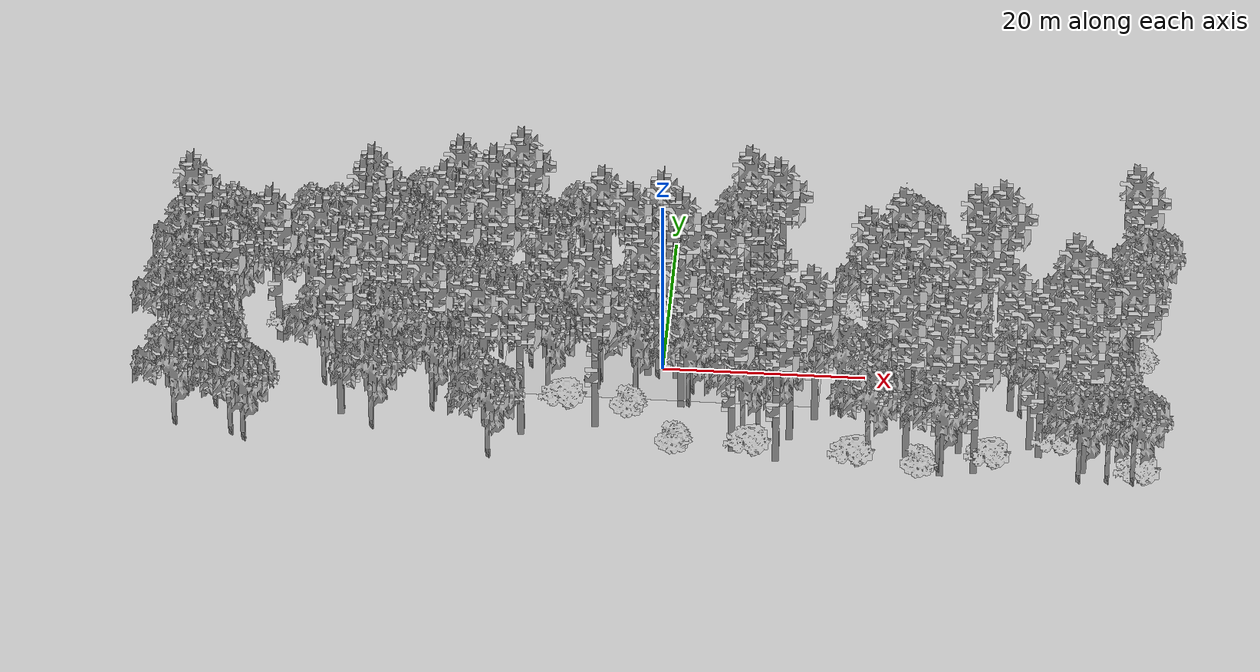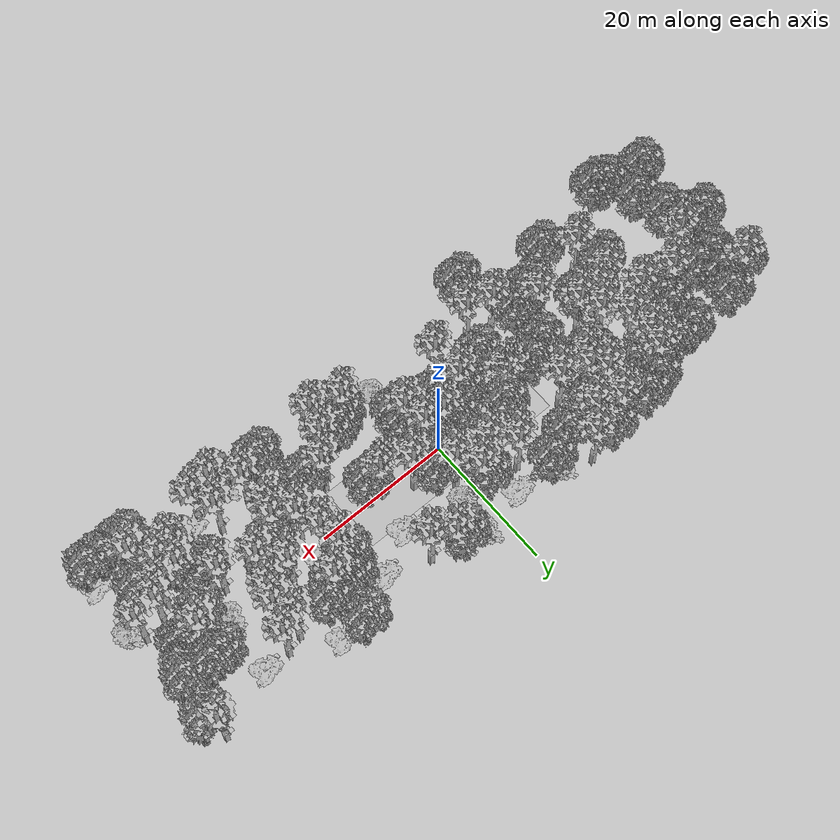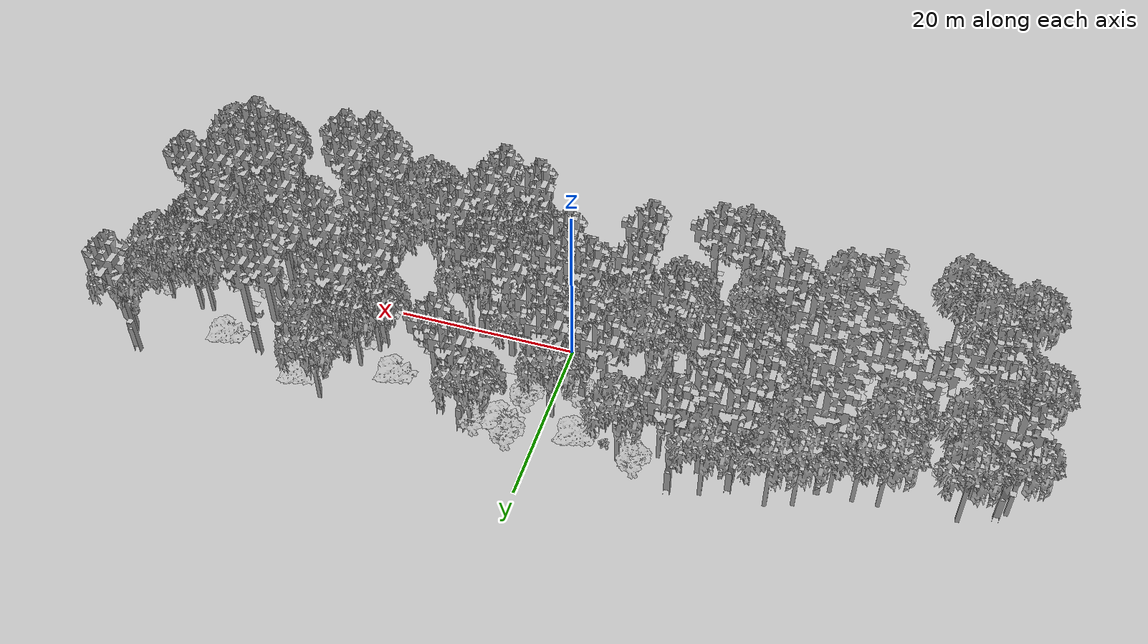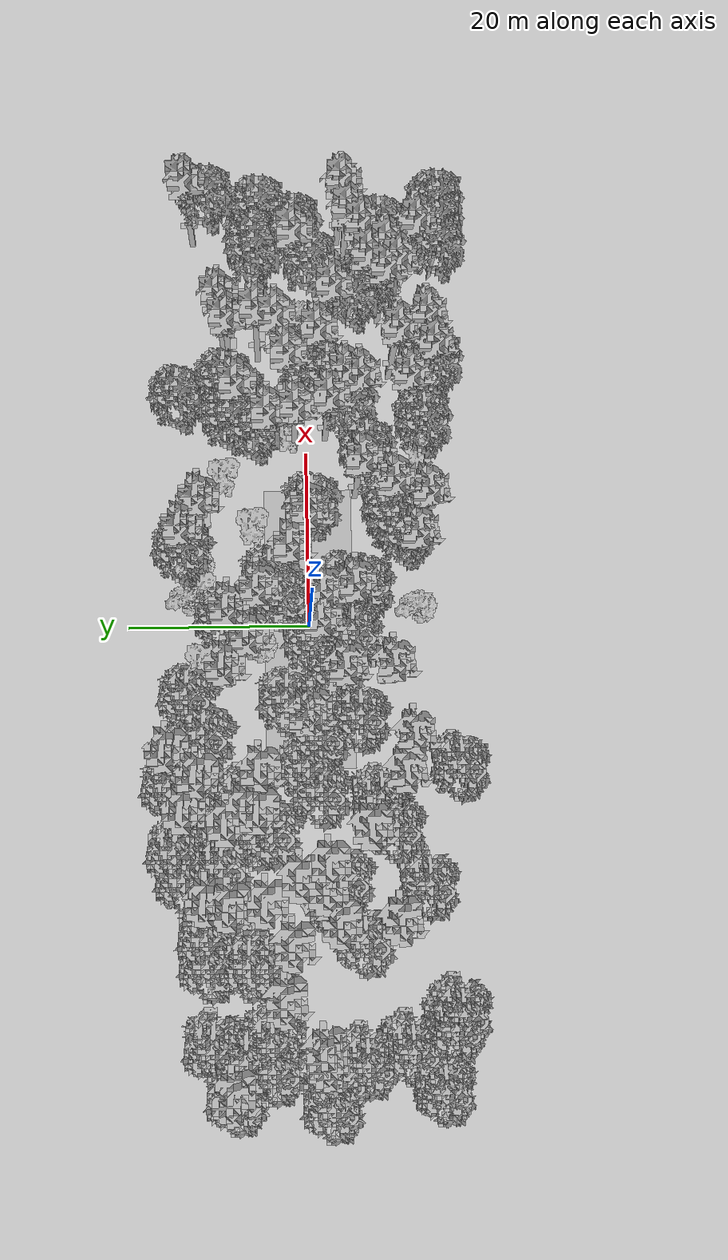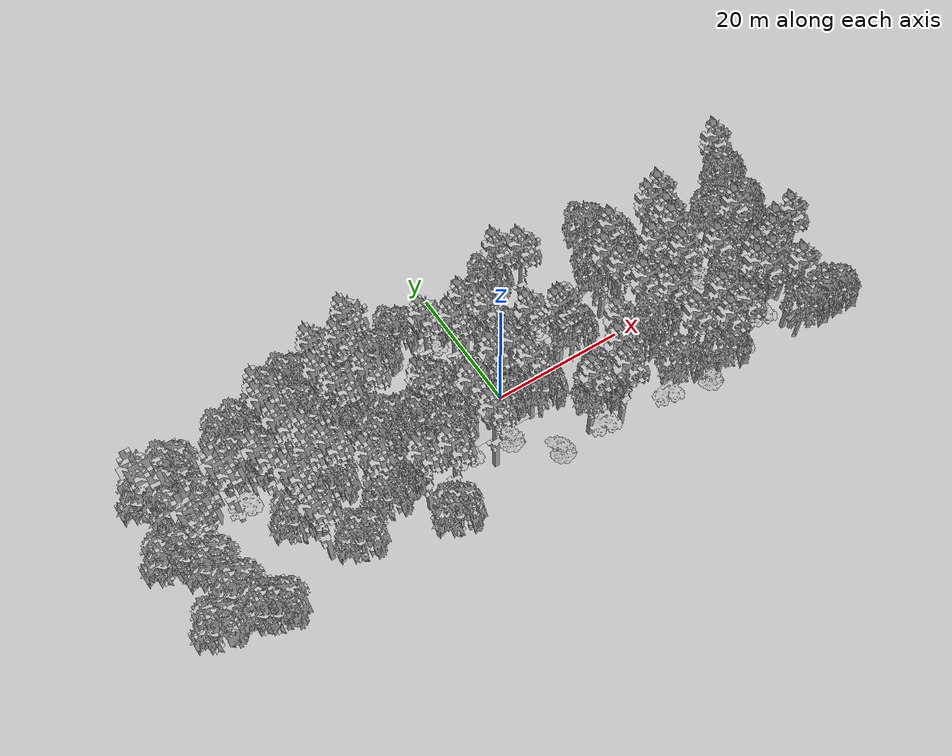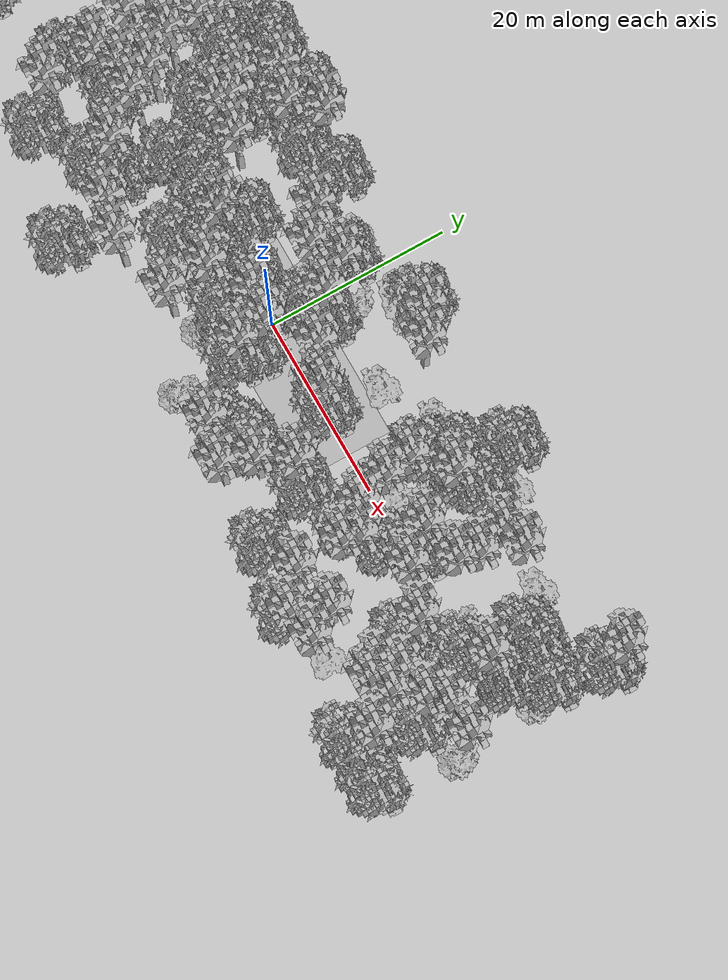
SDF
<sdf version="1.7">
    <world name="default">
        <plugin name="mrs_gazebo_static_transform_republisher_plugin" filename="libMrsGazeboCommonResources_StaticTransformRepublisher.so"/>
        <spherical_coordinates>
            <surface_model>EARTH_WGS84</surface_model>
            <latitude_deg>47.3977</latitude_deg>
            <longitude_deg>8.54559</longitude_deg>
            <elevation>0</elevation>
            <heading_deg>0</heading_deg>
        </spherical_coordinates>
        <physics name="default_physics" default="0" type="ode">
            <ode>
                <solver>
                    <type>quick</type>
                    <iters>10</iters>
                    <sor>1.3</sor>
                    <use_dynamic_moi_rescaling>0</use_dynamic_moi_rescaling>
                </solver>
                <constraints>
                    <cfm>0</cfm>
                    <erp>0.2</erp>
                    <contact_max_correcting_vel>1000</contact_max_correcting_vel>
                    <contact_surface_layer>0.001</contact_surface_layer>
                </constraints>
            </ode>
            <max_step_size>0.004</max_step_size>
            <real_time_factor>1</real_time_factor>
            <real_time_update_rate>250</real_time_update_rate>
        </physics>
        <scene>
            <shadows>0</shadows>
            <ambient>0.4 0.4 0.4 1</ambient>
            <background>0.7 0.7 0.7 1</background>
        </scene>
        <light name="sun" type="directional">
            <pose>0 0 1000 0.4 0.2 0</pose>
            <diffuse>1 1 1 1</diffuse>
            <specular>0.6 0.6 0.6 1</specular>
            <direction>0.1 0.1 -0.9</direction>
            <attenuation>
                <range>20</range>
                <constant>0.5</constant>
                <linear>0.01</linear>
                <quadratic>0.001</quadratic>
            </attenuation>
            <cast_shadows>1</cast_shadows>
            <spot>
                <inner_angle>0</inner_angle>
                <outer_angle>0</outer_angle>
                <falloff>0</falloff>
            </spot>
        </light>
        <model name="ground_plane">
            <static>1</static>
            <link name="link">
                <collision name="collision">
                    <pose>-50 0 0 0 -0 0</pose>
                    <geometry>
                        <plane>
                            <normal>0 0 1</normal>
                            <size>100 100</size>
                        </plane>
                    </geometry>
                    <surface>
                        <contact>
                            <ode>
                                <min_depth>0.01</min_depth>
                                <max_vel>0</max_vel>
                            </ode>
                        </contact>
                        <friction>
                            <ode/>
                            <torsional>
                                <ode/>
                            </torsional>
                        </friction>
                        <bounce/>
                    </surface>
                    <max_contacts>10</max_contacts>
                </collision>
                <visual name="grass">
                    <pose>0 0 0 0 -0 0</pose>
                    <cast_shadows>0</cast_shadows>
                    <geometry>
                        <mesh>
                            <scale>0.5814285714285714 0.18142857142857144 0.1</scale>
                            <uri>file://grass_plane/meshes/grass_plane.dae</uri>
                        </mesh>
                    </geometry>
                </visual>
                <self_collide>0</self_collide>
                <enable_wind>0</enable_wind>
                <kinematic>0</kinematic>
            </link>
        </model>
        <model name="the_void">
            <static>1</static>
            <link name="link">
                <pose>0 0 0.1 0 -0 0</pose>
                <visual name="the_void">
                    <pose>0 0 2 0 -0 0</pose>
                    <geometry>
                        <sphere>
                            <radius>0.25</radius>
                        </sphere>
                    </geometry>
                    <material>
                        <script>
                            <uri>file://media/materials/scripts/Gazebo.material</uri>
                            <name>Gazebo/Black</name>
                        </script>
                    </material>
                </visual>
                <self_collide>0</self_collide>
                <enable_wind>0</enable_wind>
                <kinematic>0</kinematic>
            </link>
            <pose>-1000 -1000 0 0 -0 0</pose>
        </model>
        <gui fullscreen="0">
            <camera name="camera">
                <pose>35.1577 98.6044 40.0204 0 0.407996 -1.99761</pose>
                <view_controller>orbit</view_controller>
                <projection_type>perspective</projection_type>
            </camera>
        </gui>
        <plugin name="mrs_gazebo_rviz_cam_synchronizer" filename="libMrsGazeboCommonResources_RvizCameraSynchronizer.so">
            <target_frame_id>gazebo_user_camera</target_frame_id>
            <world_origin_frame_id>uav1/gps_origin</world_origin_frame_id>
            <frame_to_follow>uav1</frame_to_follow>
        </plugin>
        <gravity>0 0 -9.8066</gravity>
        <magnetic_field>6e-06 2.3e-05 -4.2e-05</magnetic_field>
        <atmosphere type="adiabatic"/>
        <wind/>
        <model name="Tree 0">
            <static>1</static>
            <pose>-13.08776603924089 -0.5772297621485372 0 1.57079 -0 0</pose>
            <link name="link">
                <pose>0 0 0 0 -0 0</pose>
                <collision name="collision">
                    <geometry>
                        <mesh>
                            <scale>3.5 5 3.5</scale>
                            <uri>model://tree_2/meshes/tree_2.obj</uri>
                        </mesh>
                    </geometry>
                    <max_contacts>10</max_contacts>
                    <surface>
                        <contact>
                            <ode/>
                        </contact>
                        <bounce/>
                        <friction>
                            <torsional>
                                <ode/>
                            </torsional>
                            <ode/>
                        </friction>
                    </surface>
                </collision>
                <visual name="visual">
                    <geometry>
                        <mesh>
                            <scale>3.5 5 3.5</scale>
                            <uri>model://tree_2/meshes/tree_2.obj</uri>
                        </mesh>
                    </geometry>
                </visual>
                <self_collide>0</self_collide>
                <enable_wind>0</enable_wind>
                <kinematic>0</kinematic>
            </link>
        </model>
        <model name="Tree 1">
            <static>1</static>
            <pose>-47.01961347721935 8.22250506418413 0 1.57079 -0 0</pose>
            <link name="link">
                <pose>0 0 0 0 -0 0</pose>
                <collision name="collision">
                    <geometry>
                        <mesh>
                            <scale>3.5 5 3.5</scale>
                            <uri>model://tree_9/meshes/tree_9.obj</uri>
                        </mesh>
                    </geometry>
                    <max_contacts>10</max_contacts>
                    <surface>
                        <contact>
                            <ode/>
                        </contact>
                        <bounce/>
                        <friction>
                            <torsional>
                                <ode/>
                            </torsional>
                            <ode/>
                        </friction>
                    </surface>
                </collision>
                <visual name="visual">
                    <geometry>
                        <mesh>
                            <scale>3.5 5 3.5</scale>
                            <uri>model://tree_9/meshes/tree_9.obj</uri>
                        </mesh>
                    </geometry>
                </visual>
                <self_collide>0</self_collide>
                <enable_wind>0</enable_wind>
                <kinematic>0</kinematic>
            </link>
        </model>
        <model name="Tree 2">
            <static>1</static>
            <pose>24.3925668513738 -5.404501681647249 0 1.57079 -0 0</pose>
            <link name="link">
                <pose>0 0 0 0 -0 0</pose>
                <collision name="collision">
                    <geometry>
                        <mesh>
                            <scale>3.5 5 3.5</scale>
                            <uri>model://tree_9/meshes/tree_9.obj</uri>
                        </mesh>
                    </geometry>
                    <max_contacts>10</max_contacts>
                    <surface>
                        <contact>
                            <ode/>
                        </contact>
                        <bounce/>
                        <friction>
                            <torsional>
                                <ode/>
                            </torsional>
                            <ode/>
                        </friction>
                    </surface>
                </collision>
                <visual name="visual">
                    <geometry>
                        <mesh>
                            <scale>3.5 5 3.5</scale>
                            <uri>model://tree_9/meshes/tree_9.obj</uri>
                        </mesh>
                    </geometry>
                </visual>
                <self_collide>0</self_collide>
                <enable_wind>0</enable_wind>
                <kinematic>0</kinematic>
            </link>
        </model>
        <model name="Tree 3">
            <static>1</static>
            <pose>-6.126119243483544 -8.083550674161502 0 1.57079 -0 0</pose>
            <link name="link">
                <pose>0 0 0 0 -0 0</pose>
                <collision name="collision">
                    <geometry>
                        <mesh>
                            <scale>3.5 5 3.5</scale>
                            <uri>model://tree_9/meshes/tree_9.obj</uri>
                        </mesh>
                    </geometry>
                    <max_contacts>10</max_contacts>
                    <surface>
                        <contact>
                            <ode/>
                        </contact>
                        <bounce/>
                        <friction>
                            <torsional>
                                <ode/>
                            </torsional>
                            <ode/>
                        </friction>
                    </surface>
                </collision>
                <visual name="visual">
                    <geometry>
                        <mesh>
                            <scale>3.5 5 3.5</scale>
                            <uri>model://tree_9/meshes/tree_9.obj</uri>
                        </mesh>
                    </geometry>
                </visual>
                <self_collide>0</self_collide>
                <enable_wind>0</enable_wind>
                <kinematic>0</kinematic>
            </link>
        </model>
        <model name="Tree 4">
            <static>1</static>
            <pose>47.5329402677274 11.142876085032373 0 1.57079 -0 0</pose>
            <link name="link">
                <pose>0 0 0 0 -0 0</pose>
                <collision name="collision">
                    <geometry>
                        <mesh>
                            <scale>3.5 5 3.5</scale>
                            <uri>model://tree_2/meshes/tree_2.obj</uri>
                        </mesh>
                    </geometry>
                    <max_contacts>10</max_contacts>
                    <surface>
                        <contact>
                            <ode/>
                        </contact>
                        <bounce/>
                        <friction>
                            <torsional>
                                <ode/>
                            </torsional>
                            <ode/>
                        </friction>
                    </surface>
                </collision>
                <visual name="visual">
                    <geometry>
                        <mesh>
                            <scale>3.5 5 3.5</scale>
                            <uri>model://tree_2/meshes/tree_2.obj</uri>
                        </mesh>
                    </geometry>
                </visual>
                <self_collide>0</self_collide>
                <enable_wind>0</enable_wind>
                <kinematic>0</kinematic>
            </link>
        </model>
        <model name="Tree 5">
            <static>1</static>
            <pose>39.25403059731241 -8.516198860370325 0 1.57079 -0 0</pose>
            <link name="link">
                <pose>0 0 0 0 -0 0</pose>
                <collision name="collision">
                    <geometry>
                        <mesh>
                            <scale>3.5 5 3.5</scale>
                            <uri>model://tree_9/meshes/tree_9.obj</uri>
                        </mesh>
                    </geometry>
                    <max_contacts>10</max_contacts>
                    <surface>
                        <contact>
                            <ode/>
                        </contact>
                        <bounce/>
                        <friction>
                            <torsional>
                                <ode/>
                            </torsional>
                            <ode/>
                        </friction>
                    </surface>
                </collision>
                <visual name="visual">
                    <geometry>
                        <mesh>
                            <scale>3.5 5 3.5</scale>
                            <uri>model://tree_9/meshes/tree_9.obj</uri>
                        </mesh>
                    </geometry>
                </visual>
                <self_collide>0</self_collide>
                <enable_wind>0</enable_wind>
                <kinematic>0</kinematic>
            </link>
        </model>
        <model name="Tree 6">
            <static>1</static>
            <pose>-6.022346612833658 -2.2716010992971363 0 1.57079 -0 0</pose>
            <link name="link">
                <pose>0 0 0 0 -0 0</pose>
                <collision name="collision">
                    <geometry>
                        <mesh>
                            <scale>3.5 5 3.5</scale>
                            <uri>model://tree_2/meshes/tree_2.obj</uri>
                        </mesh>
                    </geometry>
                    <max_contacts>10</max_contacts>
                    <surface>
                        <contact>
                            <ode/>
                        </contact>
                        <bounce/>
                        <friction>
                            <torsional>
                                <ode/>
                            </torsional>
                            <ode/>
                        </friction>
                    </surface>
                </collision>
                <visual name="visual">
                    <geometry>
                        <mesh>
                            <scale>3.5 5 3.5</scale>
                            <uri>model://tree_2/meshes/tree_2.obj</uri>
                        </mesh>
                    </geometry>
                </visual>
                <self_collide>0</self_collide>
                <enable_wind>0</enable_wind>
                <kinematic>0</kinematic>
            </link>
        </model>
        <model name="Tree 7">
            <static>1</static>
            <pose>27.646337007123705 -13.712596400036984 0 1.57079 -0 0</pose>
            <link name="link">
                <pose>0 0 0 0 -0 0</pose>
                <collision name="collision">
                    <geometry>
                        <mesh>
                            <scale>3.5 5 3.5</scale>
                            <uri>model://tree_2/meshes/tree_2.obj</uri>
                        </mesh>
                    </geometry>
                    <max_contacts>10</max_contacts>
                    <surface>
                        <contact>
                            <ode/>
                        </contact>
                        <bounce/>
                        <friction>
                            <torsional>
                                <ode/>
                            </torsional>
                            <ode/>
                        </friction>
                    </surface>
                </collision>
                <visual name="visual">
                    <geometry>
                        <mesh>
                            <scale>3.5 5 3.5</scale>
                            <uri>model://tree_2/meshes/tree_2.obj</uri>
                        </mesh>
                    </geometry>
                </visual>
                <self_collide>0</self_collide>
                <enable_wind>0</enable_wind>
                <kinematic>0</kinematic>
            </link>
        </model>
        <model name="Tree 8">
            <static>1</static>
            <pose>-16.658015910942453 5.509180796923367 0 1.57079 -0 0</pose>
            <link name="link">
                <pose>0 0 0 0 -0 0</pose>
                <collision name="collision">
                    <geometry>
                        <mesh>
                            <scale>3.5 5 3.5</scale>
                            <uri>model://tree_9/meshes/tree_9.obj</uri>
                        </mesh>
                    </geometry>
                    <max_contacts>10</max_contacts>
                    <surface>
                        <contact>
                            <ode/>
                        </contact>
                        <bounce/>
                        <friction>
                            <torsional>
                                <ode/>
                            </torsional>
                            <ode/>
                        </friction>
                    </surface>
                </collision>
                <visual name="visual">
                    <geometry>
                        <mesh>
                            <scale>3.5 5 3.5</scale>
                            <uri>model://tree_9/meshes/tree_9.obj</uri>
                        </mesh>
                    </geometry>
                </visual>
                <self_collide>0</self_collide>
                <enable_wind>0</enable_wind>
                <kinematic>0</kinematic>
            </link>
        </model>
        <model name="Tree 9">
            <static>1</static>
            <pose>-22.754342409681048 6.128328598537866 0 1.57079 -0 0</pose>
            <link name="link">
                <pose>0 0 0 0 -0 0</pose>
                <collision name="collision">
                    <geometry>
                        <mesh>
                            <scale>3.5 5 3.5</scale>
                            <uri>model://tree_2/meshes/tree_2.obj</uri>
                        </mesh>
                    </geometry>
                    <max_contacts>10</max_contacts>
                    <surface>
                        <contact>
                            <ode/>
                        </contact>
                        <bounce/>
                        <friction>
                            <torsional>
                                <ode/>
                            </torsional>
                            <ode/>
                        </friction>
                    </surface>
                </collision>
                <visual name="visual">
                    <geometry>
                        <mesh>
                            <scale>3.5 5 3.5</scale>
                            <uri>model://tree_2/meshes/tree_2.obj</uri>
                        </mesh>
                    </geometry>
                </visual>
                <self_collide>0</self_collide>
                <enable_wind>0</enable_wind>
                <kinematic>0</kinematic>
            </link>
        </model>
        <model name="Tree 10">
            <static>1</static>
            <pose>39.57564780001539 -0.3773614892481305 0 1.57079 -0 0</pose>
            <link name="link">
                <pose>0 0 0 0 -0 0</pose>
                <collision name="collision">
                    <geometry>
                        <mesh>
                            <scale>3.5 5 3.5</scale>
                            <uri>model://tree_2/meshes/tree_2.obj</uri>
                        </mesh>
                    </geometry>
                    <max_contacts>10</max_contacts>
                    <surface>
                        <contact>
                            <ode/>
                        </contact>
                        <bounce/>
                        <friction>
                            <torsional>
                                <ode/>
                            </torsional>
                            <ode/>
                        </friction>
                    </surface>
                </collision>
                <visual name="visual">
                    <geometry>
                        <mesh>
                            <scale>3.5 5 3.5</scale>
                            <uri>model://tree_2/meshes/tree_2.obj</uri>
                        </mesh>
                    </geometry>
                </visual>
                <self_collide>0</self_collide>
                <enable_wind>0</enable_wind>
                <kinematic>0</kinematic>
            </link>
        </model>
        <model name="Tree 11">
            <static>1</static>
            <pose>43.17099553991636 -4.548261400795324 0 1.57079 -0 0</pose>
            <link name="link">
                <pose>0 0 0 0 -0 0</pose>
                <collision name="collision">
                    <geometry>
                        <mesh>
                            <scale>3.5 5 3.5</scale>
                            <uri>model://tree_9/meshes/tree_9.obj</uri>
                        </mesh>
                    </geometry>
                    <max_contacts>10</max_contacts>
                    <surface>
                        <contact>
                            <ode/>
                        </contact>
                        <bounce/>
                        <friction>
                            <torsional>
                                <ode/>
                            </torsional>
                            <ode/>
                        </friction>
                    </surface>
                </collision>
                <visual name="visual">
                    <geometry>
                        <mesh>
                            <scale>3.5 5 3.5</scale>
                            <uri>model://tree_9/meshes/tree_9.obj</uri>
                        </mesh>
                    </geometry>
                </visual>
                <self_collide>0</self_collide>
                <enable_wind>0</enable_wind>
                <kinematic>0</kinematic>
            </link>
        </model>
        <model name="Tree 12">
            <static>1</static>
            <pose>-29.27480336074714 10.737721210058218 0 1.57079 -0 0</pose>
            <link name="link">
                <pose>0 0 0 0 -0 0</pose>
                <collision name="collision">
                    <geometry>
                        <mesh>
                            <scale>3.5 5 3.5</scale>
                            <uri>model://tree_9/meshes/tree_9.obj</uri>
                        </mesh>
                    </geometry>
                    <max_contacts>10</max_contacts>
                    <surface>
                        <contact>
                            <ode/>
                        </contact>
                        <bounce/>
                        <friction>
                            <torsional>
                                <ode/>
                            </torsional>
                            <ode/>
                        </friction>
                    </surface>
                </collision>
                <visual name="visual">
                    <geometry>
                        <mesh>
                            <scale>3.5 5 3.5</scale>
                            <uri>model://tree_9/meshes/tree_9.obj</uri>
                        </mesh>
                    </geometry>
                </visual>
                <self_collide>0</self_collide>
                <enable_wind>0</enable_wind>
                <kinematic>0</kinematic>
            </link>
        </model>
        <model name="Tree 13">
            <static>1</static>
            <pose>-28.886821845267555 -0.19077743317436635 0 1.57079 -0 0</pose>
            <link name="link">
                <pose>0 0 0 0 -0 0</pose>
                <collision name="collision">
                    <geometry>
                        <mesh>
                            <scale>3 2 3</scale>
                            <uri>model://tree_3/meshes/tree_3.obj</uri>
                        </mesh>
                    </geometry>
                    <max_contacts>10</max_contacts>
                    <surface>
                        <contact>
                            <ode/>
                        </contact>
                        <bounce/>
                        <friction>
                            <torsional>
                                <ode/>
                            </torsional>
                            <ode/>
                        </friction>
                    </surface>
                </collision>
                <visual name="visual">
                    <geometry>
                        <mesh>
                            <scale>3 2 3</scale>
                            <uri>model://tree_3/meshes/tree_3.obj</uri>
                        </mesh>
                    </geometry>
                </visual>
                <self_collide>0</self_collide>
                <enable_wind>0</enable_wind>
                <kinematic>0</kinematic>
            </link>
        </model>
        <model name="Tree 14">
            <static>1</static>
            <pose>22.139885442716036 -2.181833721462315 0 1.57079 -0 0</pose>
            <link name="link">
                <pose>0 0 0 0 -0 0</pose>
                <collision name="collision">
                    <geometry>
                        <mesh>
                            <scale>3.5 5 3.5</scale>
                            <uri>model://tree_9/meshes/tree_9.obj</uri>
                        </mesh>
                    </geometry>
                    <max_contacts>10</max_contacts>
                    <surface>
                        <contact>
                            <ode/>
                        </contact>
                        <bounce/>
                        <friction>
                            <torsional>
                                <ode/>
                            </torsional>
                            <ode/>
                        </friction>
                    </surface>
                </collision>
                <visual name="visual">
                    <geometry>
                        <mesh>
                            <scale>3.5 5 3.5</scale>
                            <uri>model://tree_9/meshes/tree_9.obj</uri>
                        </mesh>
                    </geometry>
                </visual>
                <self_collide>0</self_collide>
                <enable_wind>0</enable_wind>
                <kinematic>0</kinematic>
            </link>
        </model>
        <model name="Tree 15">
            <static>1</static>
            <pose>-22.330073632906316 -5.340759959266032 0 1.57079 -0 0</pose>
            <link name="link">
                <pose>0 0 0 0 -0 0</pose>
                <collision name="collision">
                    <geometry>
                        <mesh>
                            <scale>3.5 5 3.5</scale>
                            <uri>model://tree_9/meshes/tree_9.obj</uri>
                        </mesh>
                    </geometry>
                    <max_contacts>10</max_contacts>
                    <surface>
                        <contact>
                            <ode/>
                        </contact>
                        <bounce/>
                        <friction>
                            <torsional>
                                <ode/>
                            </torsional>
                            <ode/>
                        </friction>
                    </surface>
                </collision>
                <visual name="visual">
                    <geometry>
                        <mesh>
                            <scale>3.5 5 3.5</scale>
                            <uri>model://tree_9/meshes/tree_9.obj</uri>
                        </mesh>
                    </geometry>
                </visual>
                <self_collide>0</self_collide>
                <enable_wind>0</enable_wind>
                <kinematic>0</kinematic>
            </link>
        </model>
        <model name="Tree 16">
            <static>1</static>
            <pose>-1.4516741808712723 -0.8507931586164847 0 1.57079 -0 0</pose>
            <link name="link">
                <pose>0 0 0 0 -0 0</pose>
                <collision name="collision">
                    <geometry>
                        <mesh>
                            <scale>3.5 5 3.5</scale>
                            <uri>model://tree_9/meshes/tree_9.obj</uri>
                        </mesh>
                    </geometry>
                    <max_contacts>10</max_contacts>
                    <surface>
                        <contact>
                            <ode/>
                        </contact>
                        <bounce/>
                        <friction>
                            <torsional>
                                <ode/>
                            </torsional>
                            <ode/>
                        </friction>
                    </surface>
                </collision>
                <visual name="visual">
                    <geometry>
                        <mesh>
                            <scale>3.5 5 3.5</scale>
                            <uri>model://tree_9/meshes/tree_9.obj</uri>
                        </mesh>
                    </geometry>
                </visual>
                <self_collide>0</self_collide>
                <enable_wind>0</enable_wind>
                <kinematic>0</kinematic>
            </link>
        </model>
        <model name="Tree 17">
            <static>1</static>
            <pose>31.153207847678388 -12.578742782359573 0 1.57079 -0 0</pose>
            <link name="link">
                <pose>0 0 0 0 -0 0</pose>
                <collision name="collision">
                    <geometry>
                        <mesh>
                            <scale>3.5 5 3.5</scale>
                            <uri>model://tree_9/meshes/tree_9.obj</uri>
                        </mesh>
                    </geometry>
                    <max_contacts>10</max_contacts>
                    <surface>
                        <contact>
                            <ode/>
                        </contact>
                        <bounce/>
                        <friction>
                            <torsional>
                                <ode/>
                            </torsional>
                            <ode/>
                        </friction>
                    </surface>
                </collision>
                <visual name="visual">
                    <geometry>
                        <mesh>
                            <scale>3.5 5 3.5</scale>
                            <uri>model://tree_9/meshes/tree_9.obj</uri>
                        </mesh>
                    </geometry>
                </visual>
                <self_collide>0</self_collide>
                <enable_wind>0</enable_wind>
                <kinematic>0</kinematic>
            </link>
        </model>
        <model name="Tree 18">
            <static>1</static>
            <pose>22.5986370348634 5.713508885821682 0 1.57079 -0 0</pose>
            <link name="link">
                <pose>0 0 0 0 -0 0</pose>
                <collision name="collision">
                    <geometry>
                        <mesh>
                            <scale>3 2 3</scale>
                            <uri>model://tree_3/meshes/tree_3.obj</uri>
                        </mesh>
                    </geometry>
                    <max_contacts>10</max_contacts>
                    <surface>
                        <contact>
                            <ode/>
                        </contact>
                        <bounce/>
                        <friction>
                            <torsional>
                                <ode/>
                            </torsional>
                            <ode/>
                        </friction>
                    </surface>
                </collision>
                <visual name="visual">
                    <geometry>
                        <mesh>
                            <scale>3 2 3</scale>
                            <uri>model://tree_3/meshes/tree_3.obj</uri>
                        </mesh>
                    </geometry>
                </visual>
                <self_collide>0</self_collide>
                <enable_wind>0</enable_wind>
                <kinematic>0</kinematic>
            </link>
        </model>
        <model name="Tree 19">
            <static>1</static>
            <pose>-28.370446010659656 -0.8846892080277975 0 1.57079 -0 0</pose>
            <link name="link">
                <pose>0 0 0 0 -0 0</pose>
                <collision name="collision">
                    <geometry>
                        <mesh>
                            <scale>3.5 5 3.5</scale>
                            <uri>model://tree_9/meshes/tree_9.obj</uri>
                        </mesh>
                    </geometry>
                    <max_contacts>10</max_contacts>
                    <surface>
                        <contact>
                            <ode/>
                        </contact>
                        <bounce/>
                        <friction>
                            <torsional>
                                <ode/>
                            </torsional>
                            <ode/>
                        </friction>
                    </surface>
                </collision>
                <visual name="visual">
                    <geometry>
                        <mesh>
                            <scale>3.5 5 3.5</scale>
                            <uri>model://tree_9/meshes/tree_9.obj</uri>
                        </mesh>
                    </geometry>
                </visual>
                <self_collide>0</self_collide>
                <enable_wind>0</enable_wind>
                <kinematic>0</kinematic>
            </link>
        </model>
        <model name="Tree 20">
            <static>1</static>
            <pose>-25.83420498522957 -1.1781284436010022 0 1.57079 -0 0</pose>
            <link name="link">
                <pose>0 0 0 0 -0 0</pose>
                <collision name="collision">
                    <geometry>
                        <mesh>
                            <scale>3.5 5 3.5</scale>
                            <uri>model://tree_9/meshes/tree_9.obj</uri>
                        </mesh>
                    </geometry>
                    <max_contacts>10</max_contacts>
                    <surface>
                        <contact>
                            <ode/>
                        </contact>
                        <bounce/>
                        <friction>
                            <torsional>
                                <ode/>
                            </torsional>
                            <ode/>
                        </friction>
                    </surface>
                </collision>
                <visual name="visual">
                    <geometry>
                        <mesh>
                            <scale>3.5 5 3.5</scale>
                            <uri>model://tree_9/meshes/tree_9.obj</uri>
                        </mesh>
                    </geometry>
                </visual>
                <self_collide>0</self_collide>
                <enable_wind>0</enable_wind>
                <kinematic>0</kinematic>
            </link>
        </model>
        <model name="Tree 21">
            <static>1</static>
            <pose>11.779574644978226 -0.19193173761753535 0 1.57079 -0 0</pose>
            <link name="link">
                <pose>0 0 0 0 -0 0</pose>
                <collision name="collision">
                    <geometry>
                        <mesh>
                            <scale>3.5 5 3.5</scale>
                            <uri>model://tree_2/meshes/tree_2.obj</uri>
                        </mesh>
                    </geometry>
                    <max_contacts>10</max_contacts>
                    <surface>
                        <contact>
                            <ode/>
                        </contact>
                        <bounce/>
                        <friction>
                            <torsional>
                                <ode/>
                            </torsional>
                            <ode/>
                        </friction>
                    </surface>
                </collision>
                <visual name="visual">
                    <geometry>
                        <mesh>
                            <scale>3.5 5 3.5</scale>
                            <uri>model://tree_2/meshes/tree_2.obj</uri>
                        </mesh>
                    </geometry>
                </visual>
                <self_collide>0</self_collide>
                <enable_wind>0</enable_wind>
                <kinematic>0</kinematic>
            </link>
        </model>
        <model name="Tree 22">
            <static>1</static>
            <pose>-43.26473242618978 10.188700560366282 0 1.57079 -0 0</pose>
            <link name="link">
                <pose>0 0 0 0 -0 0</pose>
                <collision name="collision">
                    <geometry>
                        <mesh>
                            <scale>3.5 5 3.5</scale>
                            <uri>model://tree_2/meshes/tree_2.obj</uri>
                        </mesh>
                    </geometry>
                    <max_contacts>10</max_contacts>
                    <surface>
                        <contact>
                            <ode/>
                        </contact>
                        <bounce/>
                        <friction>
                            <torsional>
                                <ode/>
                            </torsional>
                            <ode/>
                        </friction>
                    </surface>
                </collision>
                <visual name="visual">
                    <geometry>
                        <mesh>
                            <scale>3.5 5 3.5</scale>
                            <uri>model://tree_2/meshes/tree_2.obj</uri>
                        </mesh>
                    </geometry>
                </visual>
                <self_collide>0</self_collide>
                <enable_wind>0</enable_wind>
                <kinematic>0</kinematic>
            </link>
        </model>
        <model name="Tree 23">
            <static>1</static>
            <pose>11.844206726922046 -12.102021634161408 0 1.57079 -0 0</pose>
            <link name="link">
                <pose>0 0 0 0 -0 0</pose>
                <collision name="collision">
                    <geometry>
                        <mesh>
                            <scale>3.5 5 3.5</scale>
                            <uri>model://tree_9/meshes/tree_9.obj</uri>
                        </mesh>
                    </geometry>
                    <max_contacts>10</max_contacts>
                    <surface>
                        <contact>
                            <ode/>
                        </contact>
                        <bounce/>
                        <friction>
                            <torsional>
                                <ode/>
                            </torsional>
                            <ode/>
                        </friction>
                    </surface>
                </collision>
                <visual name="visual">
                    <geometry>
                        <mesh>
                            <scale>3.5 5 3.5</scale>
                            <uri>model://tree_9/meshes/tree_9.obj</uri>
                        </mesh>
                    </geometry>
                </visual>
                <self_collide>0</self_collide>
                <enable_wind>0</enable_wind>
                <kinematic>0</kinematic>
            </link>
        </model>
        <model name="Tree 24">
            <static>1</static>
            <pose>-22.5832904838725 4.417004329142081 0 1.57079 -0 0</pose>
            <link name="link">
                <pose>0 0 0 0 -0 0</pose>
                <collision name="collision">
                    <geometry>
                        <mesh>
                            <scale>3.5 5 3.5</scale>
                            <uri>model://tree_2/meshes/tree_2.obj</uri>
                        </mesh>
                    </geometry>
                    <max_contacts>10</max_contacts>
                    <surface>
                        <contact>
                            <ode/>
                        </contact>
                        <bounce/>
                        <friction>
                            <torsional>
                                <ode/>
                            </torsional>
                            <ode/>
                        </friction>
                    </surface>
                </collision>
                <visual name="visual">
                    <geometry>
                        <mesh>
                            <scale>3.5 5 3.5</scale>
                            <uri>model://tree_2/meshes/tree_2.obj</uri>
                        </mesh>
                    </geometry>
                </visual>
                <self_collide>0</self_collide>
                <enable_wind>0</enable_wind>
                <kinematic>0</kinematic>
            </link>
        </model>
        <model name="Tree 25">
            <static>1</static>
            <pose>34.440254552397334 -2.6742771190216548 0 1.57079 -0 0</pose>
            <link name="link">
                <pose>0 0 0 0 -0 0</pose>
                <collision name="collision">
                    <geometry>
                        <mesh>
                            <scale>3.5 5 3.5</scale>
                            <uri>model://tree_9/meshes/tree_9.obj</uri>
                        </mesh>
                    </geometry>
                    <max_contacts>10</max_contacts>
                    <surface>
                        <contact>
                            <ode/>
                        </contact>
                        <bounce/>
                        <friction>
                            <torsional>
                                <ode/>
                            </torsional>
                            <ode/>
                        </friction>
                    </surface>
                </collision>
                <visual name="visual">
                    <geometry>
                        <mesh>
                            <scale>3.5 5 3.5</scale>
                            <uri>model://tree_9/meshes/tree_9.obj</uri>
                        </mesh>
                    </geometry>
                </visual>
                <self_collide>0</self_collide>
                <enable_wind>0</enable_wind>
                <kinematic>0</kinematic>
            </link>
        </model>
        <model name="Tree 26">
            <static>1</static>
            <pose>-32.874221411770804 10.807398753552437 0 1.57079 -0 0</pose>
            <link name="link">
                <pose>0 0 0 0 -0 0</pose>
                <collision name="collision">
                    <geometry>
                        <mesh>
                            <scale>3.5 5 3.5</scale>
                            <uri>model://tree_2/meshes/tree_2.obj</uri>
                        </mesh>
                    </geometry>
                    <max_contacts>10</max_contacts>
                    <surface>
                        <contact>
                            <ode/>
                        </contact>
                        <bounce/>
                        <friction>
                            <torsional>
                                <ode/>
                            </torsional>
                            <ode/>
                        </friction>
                    </surface>
                </collision>
                <visual name="visual">
                    <geometry>
                        <mesh>
                            <scale>3.5 5 3.5</scale>
                            <uri>model://tree_2/meshes/tree_2.obj</uri>
                        </mesh>
                    </geometry>
                </visual>
                <self_collide>0</self_collide>
                <enable_wind>0</enable_wind>
                <kinematic>0</kinematic>
            </link>
        </model>
        <model name="Tree 27">
            <static>1</static>
            <pose>-24.550607657645767 13.95543753872439 0 1.57079 -0 0</pose>
            <link name="link">
                <pose>0 0 0 0 -0 0</pose>
                <collision name="collision">
                    <geometry>
                        <mesh>
                            <scale>3.5 5 3.5</scale>
                            <uri>model://tree_2/meshes/tree_2.obj</uri>
                        </mesh>
                    </geometry>
                    <max_contacts>10</max_contacts>
                    <surface>
                        <contact>
                            <ode/>
                        </contact>
                        <bounce/>
                        <friction>
                            <torsional>
                                <ode/>
                            </torsional>
                            <ode/>
                        </friction>
                    </surface>
                </collision>
                <visual name="visual">
                    <geometry>
                        <mesh>
                            <scale>3.5 5 3.5</scale>
                            <uri>model://tree_2/meshes/tree_2.obj</uri>
                        </mesh>
                    </geometry>
                </visual>
                <self_collide>0</self_collide>
                <enable_wind>0</enable_wind>
                <kinematic>0</kinematic>
            </link>
        </model>
        <model name="Tree 28">
            <static>1</static>
            <pose>-41.46937147290656 -13.196937336130897 0 1.57079 -0 0</pose>
            <link name="link">
                <pose>0 0 0 0 -0 0</pose>
                <collision name="collision">
                    <geometry>
                        <mesh>
                            <scale>3.5 5 3.5</scale>
                            <uri>model://tree_2/meshes/tree_2.obj</uri>
                        </mesh>
                    </geometry>
                    <max_contacts>10</max_contacts>
                    <surface>
                        <contact>
                            <ode/>
                        </contact>
                        <bounce/>
                        <friction>
                            <torsional>
                                <ode/>
                            </torsional>
                            <ode/>
                        </friction>
                    </surface>
                </collision>
                <visual name="visual">
                    <geometry>
                        <mesh>
                            <scale>3.5 5 3.5</scale>
                            <uri>model://tree_2/meshes/tree_2.obj</uri>
                        </mesh>
                    </geometry>
                </visual>
                <self_collide>0</self_collide>
                <enable_wind>0</enable_wind>
                <kinematic>0</kinematic>
            </link>
        </model>
        <model name="Tree 29">
            <static>1</static>
            <pose>-43.47848407854549 -9.070159819019622 0 1.57079 -0 0</pose>
            <link name="link">
                <pose>0 0 0 0 -0 0</pose>
                <collision name="collision">
                    <geometry>
                        <mesh>
                            <scale>3.5 5 3.5</scale>
                            <uri>model://tree_2/meshes/tree_2.obj</uri>
                        </mesh>
                    </geometry>
                    <max_contacts>10</max_contacts>
                    <surface>
                        <contact>
                            <ode/>
                        </contact>
                        <bounce/>
                        <friction>
                            <torsional>
                                <ode/>
                            </torsional>
                            <ode/>
                        </friction>
                    </surface>
                </collision>
                <visual name="visual">
                    <geometry>
                        <mesh>
                            <scale>3.5 5 3.5</scale>
                            <uri>model://tree_2/meshes/tree_2.obj</uri>
                        </mesh>
                    </geometry>
                </visual>
                <self_collide>0</self_collide>
                <enable_wind>0</enable_wind>
                <kinematic>0</kinematic>
            </link>
        </model>
        <model name="Tree 30">
            <static>1</static>
            <pose>7.452244665008685 -10.912579816924215 0 1.57079 -0 0</pose>
            <link name="link">
                <pose>0 0 0 0 -0 0</pose>
                <collision name="collision">
                    <geometry>
                        <mesh>
                            <scale>3.5 5 3.5</scale>
                            <uri>model://tree_9/meshes/tree_9.obj</uri>
                        </mesh>
                    </geometry>
                    <max_contacts>10</max_contacts>
                    <surface>
                        <contact>
                            <ode/>
                        </contact>
                        <bounce/>
                        <friction>
                            <torsional>
                                <ode/>
                            </torsional>
                            <ode/>
                        </friction>
                    </surface>
                </collision>
                <visual name="visual">
                    <geometry>
                        <mesh>
                            <scale>3.5 5 3.5</scale>
                            <uri>model://tree_9/meshes/tree_9.obj</uri>
                        </mesh>
                    </geometry>
                </visual>
                <self_collide>0</self_collide>
                <enable_wind>0</enable_wind>
                <kinematic>0</kinematic>
            </link>
        </model>
        <model name="Tree 31">
            <static>1</static>
            <pose>-40.122491762966874 -13.973843472308191 0 1.57079 -0 0</pose>
            <link name="link">
                <pose>0 0 0 0 -0 0</pose>
                <collision name="collision">
                    <geometry>
                        <mesh>
                            <scale>3.5 5 3.5</scale>
                            <uri>model://tree_2/meshes/tree_2.obj</uri>
                        </mesh>
                    </geometry>
                    <max_contacts>10</max_contacts>
                    <surface>
                        <contact>
                            <ode/>
                        </contact>
                        <bounce/>
                        <friction>
                            <torsional>
                                <ode/>
                            </torsional>
                            <ode/>
                        </friction>
                    </surface>
                </collision>
                <visual name="visual">
                    <geometry>
                        <mesh>
                            <scale>3.5 5 3.5</scale>
                            <uri>model://tree_2/meshes/tree_2.obj</uri>
                        </mesh>
                    </geometry>
                </visual>
                <self_collide>0</self_collide>
                <enable_wind>0</enable_wind>
                <kinematic>0</kinematic>
            </link>
        </model>
        <model name="Tree 32">
            <static>1</static>
            <pose>41.490987333355974 -5.887465798529242 0 1.57079 -0 0</pose>
            <link name="link">
                <pose>0 0 0 0 -0 0</pose>
                <collision name="collision">
                    <geometry>
                        <mesh>
                            <scale>3.5 5 3.5</scale>
                            <uri>model://tree_9/meshes/tree_9.obj</uri>
                        </mesh>
                    </geometry>
                    <max_contacts>10</max_contacts>
                    <surface>
                        <contact>
                            <ode/>
                        </contact>
                        <bounce/>
                        <friction>
                            <torsional>
                                <ode/>
                            </torsional>
                            <ode/>
                        </friction>
                    </surface>
                </collision>
                <visual name="visual">
                    <geometry>
                        <mesh>
                            <scale>3.5 5 3.5</scale>
                            <uri>model://tree_9/meshes/tree_9.obj</uri>
                        </mesh>
                    </geometry>
                </visual>
                <self_collide>0</self_collide>
                <enable_wind>0</enable_wind>
                <kinematic>0</kinematic>
            </link>
        </model>
        <model name="Tree 33">
            <static>1</static>
            <pose>46.457445796704405 -3.9746720735285184 0 1.57079 -0 0</pose>
            <link name="link">
                <pose>0 0 0 0 -0 0</pose>
                <collision name="collision">
                    <geometry>
                        <mesh>
                            <scale>3.5 5 3.5</scale>
                            <uri>model://tree_9/meshes/tree_9.obj</uri>
                        </mesh>
                    </geometry>
                    <max_contacts>10</max_contacts>
                    <surface>
                        <contact>
                            <ode/>
                        </contact>
                        <bounce/>
                        <friction>
                            <torsional>
                                <ode/>
                            </torsional>
                            <ode/>
                        </friction>
                    </surface>
                </collision>
                <visual name="visual">
                    <geometry>
                        <mesh>
                            <scale>3.5 5 3.5</scale>
                            <uri>model://tree_9/meshes/tree_9.obj</uri>
                        </mesh>
                    </geometry>
                </visual>
                <self_collide>0</self_collide>
                <enable_wind>0</enable_wind>
                <kinematic>0</kinematic>
            </link>
        </model>
        <model name="Tree 34">
            <static>1</static>
            <pose>43.55244845924382 -8.021989021581138 0 1.57079 -0 0</pose>
            <link name="link">
                <pose>0 0 0 0 -0 0</pose>
                <collision name="collision">
                    <geometry>
                        <mesh>
                            <scale>3.5 5 3.5</scale>
                            <uri>model://tree_2/meshes/tree_2.obj</uri>
                        </mesh>
                    </geometry>
                    <max_contacts>10</max_contacts>
                    <surface>
                        <contact>
                            <ode/>
                        </contact>
                        <bounce/>
                        <friction>
                            <torsional>
                                <ode/>
                            </torsional>
                            <ode/>
                        </friction>
                    </surface>
                </collision>
                <visual name="visual">
                    <geometry>
                        <mesh>
                            <scale>3.5 5 3.5</scale>
                            <uri>model://tree_2/meshes/tree_2.obj</uri>
                        </mesh>
                    </geometry>
                </visual>
                <self_collide>0</self_collide>
                <enable_wind>0</enable_wind>
                <kinematic>0</kinematic>
            </link>
        </model>
        <model name="Tree 35">
            <static>1</static>
            <pose>-46.03653669242314 -1.9384656324324148 0 1.57079 -0 0</pose>
            <link name="link">
                <pose>0 0 0 0 -0 0</pose>
                <collision name="collision">
                    <geometry>
                        <mesh>
                            <scale>3.5 5 3.5</scale>
                            <uri>model://tree_2/meshes/tree_2.obj</uri>
                        </mesh>
                    </geometry>
                    <max_contacts>10</max_contacts>
                    <surface>
                        <contact>
                            <ode/>
                        </contact>
                        <bounce/>
                        <friction>
                            <torsional>
                                <ode/>
                            </torsional>
                            <ode/>
                        </friction>
                    </surface>
                </collision>
                <visual name="visual">
                    <geometry>
                        <mesh>
                            <scale>3.5 5 3.5</scale>
                            <uri>model://tree_2/meshes/tree_2.obj</uri>
                        </mesh>
                    </geometry>
                </visual>
                <self_collide>0</self_collide>
                <enable_wind>0</enable_wind>
                <kinematic>0</kinematic>
            </link>
        </model>
        <model name="Tree 36">
            <static>1</static>
            <pose>-2.9998436178157917 0.08559341351876348 0 1.57079 -0 0</pose>
            <link name="link">
                <pose>0 0 0 0 -0 0</pose>
                <collision name="collision">
                    <geometry>
                        <mesh>
                            <scale>3.5 5 3.5</scale>
                            <uri>model://tree_2/meshes/tree_2.obj</uri>
                        </mesh>
                    </geometry>
                    <max_contacts>10</max_contacts>
                    <surface>
                        <contact>
                            <ode/>
                        </contact>
                        <bounce/>
                        <friction>
                            <torsional>
                                <ode/>
                            </torsional>
                            <ode/>
                        </friction>
                    </surface>
                </collision>
                <visual name="visual">
                    <geometry>
                        <mesh>
                            <scale>3.5 5 3.5</scale>
                            <uri>model://tree_2/meshes/tree_2.obj</uri>
                        </mesh>
                    </geometry>
                </visual>
                <self_collide>0</self_collide>
                <enable_wind>0</enable_wind>
                <kinematic>0</kinematic>
            </link>
        </model>
        <model name="Tree 37">
            <static>1</static>
            <pose>-44.667909294974635 -4.665956502914453 0 1.57079 -0 0</pose>
            <link name="link">
                <pose>0 0 0 0 -0 0</pose>
                <collision name="collision">
                    <geometry>
                        <mesh>
                            <scale>3.5 5 3.5</scale>
                            <uri>model://tree_2/meshes/tree_2.obj</uri>
                        </mesh>
                    </geometry>
                    <max_contacts>10</max_contacts>
                    <surface>
                        <contact>
                            <ode/>
                        </contact>
                        <bounce/>
                        <friction>
                            <torsional>
                                <ode/>
                            </torsional>
                            <ode/>
                        </friction>
                    </surface>
                </collision>
                <visual name="visual">
                    <geometry>
                        <mesh>
                            <scale>3.5 5 3.5</scale>
                            <uri>model://tree_2/meshes/tree_2.obj</uri>
                        </mesh>
                    </geometry>
                </visual>
                <self_collide>0</self_collide>
                <enable_wind>0</enable_wind>
                <kinematic>0</kinematic>
            </link>
        </model>
        <model name="Tree 38">
            <static>1</static>
            <pose>20.356086381126218 5.936822487014425 0 1.57079 -0 0</pose>
            <link name="link">
                <pose>0 0 0 0 -0 0</pose>
                <collision name="collision">
                    <geometry>
                        <mesh>
                            <scale>3.5 5 3.5</scale>
                            <uri>model://tree_2/meshes/tree_2.obj</uri>
                        </mesh>
                    </geometry>
                    <max_contacts>10</max_contacts>
                    <surface>
                        <contact>
                            <ode/>
                        </contact>
                        <bounce/>
                        <friction>
                            <torsional>
                                <ode/>
                            </torsional>
                            <ode/>
                        </friction>
                    </surface>
                </collision>
                <visual name="visual">
                    <geometry>
                        <mesh>
                            <scale>3.5 5 3.5</scale>
                            <uri>model://tree_2/meshes/tree_2.obj</uri>
                        </mesh>
                    </geometry>
                </visual>
                <self_collide>0</self_collide>
                <enable_wind>0</enable_wind>
                <kinematic>0</kinematic>
            </link>
        </model>
        <model name="Tree 39">
            <static>1</static>
            <pose>-29.720919007682674 -2.0927902786029247 0 1.57079 -0 0</pose>
            <link name="link">
                <pose>0 0 0 0 -0 0</pose>
                <collision name="collision">
                    <geometry>
                        <mesh>
                            <scale>3.5 5 3.5</scale>
                            <uri>model://tree_2/meshes/tree_2.obj</uri>
                        </mesh>
                    </geometry>
                    <max_contacts>10</max_contacts>
                    <surface>
                        <contact>
                            <ode/>
                        </contact>
                        <bounce/>
                        <friction>
                            <torsional>
                                <ode/>
                            </torsional>
                            <ode/>
                        </friction>
                    </surface>
                </collision>
                <visual name="visual">
                    <geometry>
                        <mesh>
                            <scale>3.5 5 3.5</scale>
                            <uri>model://tree_2/meshes/tree_2.obj</uri>
                        </mesh>
                    </geometry>
                </visual>
                <self_collide>0</self_collide>
                <enable_wind>0</enable_wind>
                <kinematic>0</kinematic>
            </link>
        </model>
        <model name="Tree 40">
            <static>1</static>
            <pose>25.758005892824144 -13.827363633086165 0 1.57079 -0 0</pose>
            <link name="link">
                <pose>0 0 0 0 -0 0</pose>
                <collision name="collision">
                    <geometry>
                        <mesh>
                            <scale>4 2.5 4</scale>
                            <uri>model://tree_1/meshes/tree_1.obj</uri>
                        </mesh>
                    </geometry>
                    <max_contacts>10</max_contacts>
                    <surface>
                        <contact>
                            <ode/>
                        </contact>
                        <bounce/>
                        <friction>
                            <torsional>
                                <ode/>
                            </torsional>
                            <ode/>
                        </friction>
                    </surface>
                </collision>
                <visual name="visual">
                    <geometry>
                        <mesh>
                            <scale>4 2.5 4</scale>
                            <uri>model://tree_1/meshes/tree_1.obj</uri>
                        </mesh>
                    </geometry>
                </visual>
                <self_collide>0</self_collide>
                <enable_wind>0</enable_wind>
                <kinematic>0</kinematic>
            </link>
        </model>
        <model name="Tree 41">
            <static>1</static>
            <pose>13.003556519152127 -8.694305866713469 0 1.57079 -0 0</pose>
            <link name="link">
                <pose>0 0 0 0 -0 0</pose>
                <collision name="collision">
                    <geometry>
                        <mesh>
                            <scale>3.5 5 3.5</scale>
                            <uri>model://tree_9/meshes/tree_9.obj</uri>
                        </mesh>
                    </geometry>
                    <max_contacts>10</max_contacts>
                    <surface>
                        <contact>
                            <ode/>
                        </contact>
                        <bounce/>
                        <friction>
                            <torsional>
                                <ode/>
                            </torsional>
                            <ode/>
                        </friction>
                    </surface>
                </collision>
                <visual name="visual">
                    <geometry>
                        <mesh>
                            <scale>3.5 5 3.5</scale>
                            <uri>model://tree_9/meshes/tree_9.obj</uri>
                        </mesh>
                    </geometry>
                </visual>
                <self_collide>0</self_collide>
                <enable_wind>0</enable_wind>
                <kinematic>0</kinematic>
            </link>
        </model>
        <model name="Tree 42">
            <static>1</static>
            <pose>23.66521952611548 7.599572120415381 0 1.57079 -0 0</pose>
            <link name="link">
                <pose>0 0 0 0 -0 0</pose>
                <collision name="collision">
                    <geometry>
                        <mesh>
                            <scale>3.5 5 3.5</scale>
                            <uri>model://tree_9/meshes/tree_9.obj</uri>
                        </mesh>
                    </geometry>
                    <max_contacts>10</max_contacts>
                    <surface>
                        <contact>
                            <ode/>
                        </contact>
                        <bounce/>
                        <friction>
                            <torsional>
                                <ode/>
                            </torsional>
                            <ode/>
                        </friction>
                    </surface>
                </collision>
                <visual name="visual">
                    <geometry>
                        <mesh>
                            <scale>3.5 5 3.5</scale>
                            <uri>model://tree_9/meshes/tree_9.obj</uri>
                        </mesh>
                    </geometry>
                </visual>
                <self_collide>0</self_collide>
                <enable_wind>0</enable_wind>
                <kinematic>0</kinematic>
            </link>
        </model>
        <model name="Tree 43">
            <static>1</static>
            <pose>22.17410977936028 1.8315779820552542 0 1.57079 -0 0</pose>
            <link name="link">
                <pose>0 0 0 0 -0 0</pose>
                <collision name="collision">
                    <geometry>
                        <mesh>
                            <scale>3 2 3</scale>
                            <uri>model://tree_3/meshes/tree_3.obj</uri>
                        </mesh>
                    </geometry>
                    <max_contacts>10</max_contacts>
                    <surface>
                        <contact>
                            <ode/>
                        </contact>
                        <bounce/>
                        <friction>
                            <torsional>
                                <ode/>
                            </torsional>
                            <ode/>
                        </friction>
                    </surface>
                </collision>
                <visual name="visual">
                    <geometry>
                        <mesh>
                            <scale>3 2 3</scale>
                            <uri>model://tree_3/meshes/tree_3.obj</uri>
                        </mesh>
                    </geometry>
                </visual>
                <self_collide>0</self_collide>
                <enable_wind>0</enable_wind>
                <kinematic>0</kinematic>
            </link>
        </model>
        <model name="Tree 44">
            <static>1</static>
            <pose>4.048705332830771 11.902267295829922 0 1.57079 -0 0</pose>
            <link name="link">
                <pose>0 0 0 0 -0 0</pose>
                <collision name="collision">
                    <geometry>
                        <mesh>
                            <scale>3 2 3</scale>
                            <uri>model://tree_3/meshes/tree_3.obj</uri>
                        </mesh>
                    </geometry>
                    <max_contacts>10</max_contacts>
                    <surface>
                        <contact>
                            <ode/>
                        </contact>
                        <bounce/>
                        <friction>
                            <torsional>
                                <ode/>
                            </torsional>
                            <ode/>
                        </friction>
                    </surface>
                </collision>
                <visual name="visual">
                    <geometry>
                        <mesh>
                            <scale>3 2 3</scale>
                            <uri>model://tree_3/meshes/tree_3.obj</uri>
                        </mesh>
                    </geometry>
                </visual>
                <self_collide>0</self_collide>
                <enable_wind>0</enable_wind>
                <kinematic>0</kinematic>
            </link>
        </model>
        <model name="Tree 45">
            <static>1</static>
            <pose>-0.6706317585110213 9.25622668928656 0 1.57079 -0 0</pose>
            <link name="link">
                <pose>0 0 0 0 -0 0</pose>
                <collision name="collision">
                    <geometry>
                        <mesh>
                            <scale>3.5 5 3.5</scale>
                            <uri>model://tree_2/meshes/tree_2.obj</uri>
                        </mesh>
                    </geometry>
                    <max_contacts>10</max_contacts>
                    <surface>
                        <contact>
                            <ode/>
                        </contact>
                        <bounce/>
                        <friction>
                            <torsional>
                                <ode/>
                            </torsional>
                            <ode/>
                        </friction>
                    </surface>
                </collision>
                <visual name="visual">
                    <geometry>
                        <mesh>
                            <scale>3.5 5 3.5</scale>
                            <uri>model://tree_2/meshes/tree_2.obj</uri>
                        </mesh>
                    </geometry>
                </visual>
                <self_collide>0</self_collide>
                <enable_wind>0</enable_wind>
                <kinematic>0</kinematic>
            </link>
        </model>
        <model name="Tree 46">
            <static>1</static>
            <pose>-25.93858296153601 9.390293917685124 0 1.57079 -0 0</pose>
            <link name="link">
                <pose>0 0 0 0 -0 0</pose>
                <collision name="collision">
                    <geometry>
                        <mesh>
                            <scale>3.5 5 3.5</scale>
                            <uri>model://tree_2/meshes/tree_2.obj</uri>
                        </mesh>
                    </geometry>
                    <max_contacts>10</max_contacts>
                    <surface>
                        <contact>
                            <ode/>
                        </contact>
                        <bounce/>
                        <friction>
                            <torsional>
                                <ode/>
                            </torsional>
                            <ode/>
                        </friction>
                    </surface>
                </collision>
                <visual name="visual">
                    <geometry>
                        <mesh>
                            <scale>3.5 5 3.5</scale>
                            <uri>model://tree_2/meshes/tree_2.obj</uri>
                        </mesh>
                    </geometry>
                </visual>
                <self_collide>0</self_collide>
                <enable_wind>0</enable_wind>
                <kinematic>0</kinematic>
            </link>
        </model>
        <model name="Tree 47">
            <static>1</static>
            <pose>41.33996712415616 -14.496960765584841 0 1.57079 -0 0</pose>
            <link name="link">
                <pose>0 0 0 0 -0 0</pose>
                <collision name="collision">
                    <geometry>
                        <mesh>
                            <scale>3.5 5 3.5</scale>
                            <uri>model://tree_2/meshes/tree_2.obj</uri>
                        </mesh>
                    </geometry>
                    <max_contacts>10</max_contacts>
                    <surface>
                        <contact>
                            <ode/>
                        </contact>
                        <bounce/>
                        <friction>
                            <torsional>
                                <ode/>
                            </torsional>
                            <ode/>
                        </friction>
                    </surface>
                </collision>
                <visual name="visual">
                    <geometry>
                        <mesh>
                            <scale>3.5 5 3.5</scale>
                            <uri>model://tree_2/meshes/tree_2.obj</uri>
                        </mesh>
                    </geometry>
                </visual>
                <self_collide>0</self_collide>
                <enable_wind>0</enable_wind>
                <kinematic>0</kinematic>
            </link>
        </model>
        <model name="Tree 48">
            <static>1</static>
            <pose>-6.208880384806292 8.926299032087545 0 1.57079 -0 0</pose>
            <link name="link">
                <pose>0 0 0 0 -0 0</pose>
                <collision name="collision">
                    <geometry>
                        <mesh>
                            <scale>3.5 5 3.5</scale>
                            <uri>model://tree_9/meshes/tree_9.obj</uri>
                        </mesh>
                    </geometry>
                    <max_contacts>10</max_contacts>
                    <surface>
                        <contact>
                            <ode/>
                        </contact>
                        <bounce/>
                        <friction>
                            <torsional>
                                <ode/>
                            </torsional>
                            <ode/>
                        </friction>
                    </surface>
                </collision>
                <visual name="visual">
                    <geometry>
                        <mesh>
                            <scale>3.5 5 3.5</scale>
                            <uri>model://tree_9/meshes/tree_9.obj</uri>
                        </mesh>
                    </geometry>
                </visual>
                <self_collide>0</self_collide>
                <enable_wind>0</enable_wind>
                <kinematic>0</kinematic>
            </link>
        </model>
        <model name="Tree 49">
            <static>1</static>
            <pose>-48.63403547193869 -1.2588969417029254 0 1.57079 -0 0</pose>
            <link name="link">
                <pose>0 0 0 0 -0 0</pose>
                <collision name="collision">
                    <geometry>
                        <mesh>
                            <scale>3.5 5 3.5</scale>
                            <uri>model://tree_2/meshes/tree_2.obj</uri>
                        </mesh>
                    </geometry>
                    <max_contacts>10</max_contacts>
                    <surface>
                        <contact>
                            <ode/>
                        </contact>
                        <bounce/>
                        <friction>
                            <torsional>
                                <ode/>
                            </torsional>
                            <ode/>
                        </friction>
                    </surface>
                </collision>
                <visual name="visual">
                    <geometry>
                        <mesh>
                            <scale>3.5 5 3.5</scale>
                            <uri>model://tree_2/meshes/tree_2.obj</uri>
                        </mesh>
                    </geometry>
                </visual>
                <self_collide>0</self_collide>
                <enable_wind>0</enable_wind>
                <kinematic>0</kinematic>
            </link>
        </model>
        <model name="Tree 50">
            <static>1</static>
            <pose>-33.487661060012314 2.410509743409495 0 1.57079 -0 0</pose>
            <link name="link">
                <pose>0 0 0 0 -0 0</pose>
                <collision name="collision">
                    <geometry>
                        <mesh>
                            <scale>3.5 5 3.5</scale>
                            <uri>model://tree_9/meshes/tree_9.obj</uri>
                        </mesh>
                    </geometry>
                    <max_contacts>10</max_contacts>
                    <surface>
                        <contact>
                            <ode/>
                        </contact>
                        <bounce/>
                        <friction>
                            <torsional>
                                <ode/>
                            </torsional>
                            <ode/>
                        </friction>
                    </surface>
                </collision>
                <visual name="visual">
                    <geometry>
                        <mesh>
                            <scale>3.5 5 3.5</scale>
                            <uri>model://tree_9/meshes/tree_9.obj</uri>
                        </mesh>
                    </geometry>
                </visual>
                <self_collide>0</self_collide>
                <enable_wind>0</enable_wind>
                <kinematic>0</kinematic>
            </link>
        </model>
        <model name="Tree 51">
            <static>1</static>
            <pose>15.284408588775136 -5.432858180794138 0 1.57079 -0 0</pose>
            <link name="link">
                <pose>0 0 0 0 -0 0</pose>
                <collision name="collision">
                    <geometry>
                        <mesh>
                            <scale>3.5 5 3.5</scale>
                            <uri>model://tree_9/meshes/tree_9.obj</uri>
                        </mesh>
                    </geometry>
                    <max_contacts>10</max_contacts>
                    <surface>
                        <contact>
                            <ode/>
                        </contact>
                        <bounce/>
                        <friction>
                            <torsional>
                                <ode/>
                            </torsional>
                            <ode/>
                        </friction>
                    </surface>
                </collision>
                <visual name="visual">
                    <geometry>
                        <mesh>
                            <scale>3.5 5 3.5</scale>
                            <uri>model://tree_9/meshes/tree_9.obj</uri>
                        </mesh>
                    </geometry>
                </visual>
                <self_collide>0</self_collide>
                <enable_wind>0</enable_wind>
                <kinematic>0</kinematic>
            </link>
        </model>
        <model name="Tree 52">
            <static>1</static>
            <pose>-6.3455529735930725 -3.3131450640584674 0 1.57079 -0 0</pose>
            <link name="link">
                <pose>0 0 0 0 -0 0</pose>
                <collision name="collision">
                    <geometry>
                        <mesh>
                            <scale>3.5 5 3.5</scale>
                            <uri>model://tree_9/meshes/tree_9.obj</uri>
                        </mesh>
                    </geometry>
                    <max_contacts>10</max_contacts>
                    <surface>
                        <contact>
                            <ode/>
                        </contact>
                        <bounce/>
                        <friction>
                            <torsional>
                                <ode/>
                            </torsional>
                            <ode/>
                        </friction>
                    </surface>
                </collision>
                <visual name="visual">
                    <geometry>
                        <mesh>
                            <scale>3.5 5 3.5</scale>
                            <uri>model://tree_9/meshes/tree_9.obj</uri>
                        </mesh>
                    </geometry>
                </visual>
                <self_collide>0</self_collide>
                <enable_wind>0</enable_wind>
                <kinematic>0</kinematic>
            </link>
        </model>
        <model name="Tree 53">
            <static>1</static>
            <pose>38.051714829250486 -4.058607082003714 0 1.57079 -0 0</pose>
            <link name="link">
                <pose>0 0 0 0 -0 0</pose>
                <collision name="collision">
                    <geometry>
                        <mesh>
                            <scale>4 2.5 4</scale>
                            <uri>model://tree_1/meshes/tree_1.obj</uri>
                        </mesh>
                    </geometry>
                    <max_contacts>10</max_contacts>
                    <surface>
                        <contact>
                            <ode/>
                        </contact>
                        <bounce/>
                        <friction>
                            <torsional>
                                <ode/>
                            </torsional>
                            <ode/>
                        </friction>
                    </surface>
                </collision>
                <visual name="visual">
                    <geometry>
                        <mesh>
                            <scale>4 2.5 4</scale>
                            <uri>model://tree_1/meshes/tree_1.obj</uri>
                        </mesh>
                    </geometry>
                </visual>
                <self_collide>0</self_collide>
                <enable_wind>0</enable_wind>
                <kinematic>0</kinematic>
            </link>
        </model>
        <model name="Tree 54">
            <static>1</static>
            <pose>-30.50178041574006 10.341515803728399 0 1.57079 -0 0</pose>
            <link name="link">
                <pose>0 0 0 0 -0 0</pose>
                <collision name="collision">
                    <geometry>
                        <mesh>
                            <scale>3.5 5 3.5</scale>
                            <uri>model://tree_2/meshes/tree_2.obj</uri>
                        </mesh>
                    </geometry>
                    <max_contacts>10</max_contacts>
                    <surface>
                        <contact>
                            <ode/>
                        </contact>
                        <bounce/>
                        <friction>
                            <torsional>
                                <ode/>
                            </torsional>
                            <ode/>
                        </friction>
                    </surface>
                </collision>
                <visual name="visual">
                    <geometry>
                        <mesh>
                            <scale>3.5 5 3.5</scale>
                            <uri>model://tree_2/meshes/tree_2.obj</uri>
                        </mesh>
                    </geometry>
                </visual>
                <self_collide>0</self_collide>
                <enable_wind>0</enable_wind>
                <kinematic>0</kinematic>
            </link>
        </model>
        <model name="Tree 55">
            <static>1</static>
            <pose>35.42685162921045 -4.899434049778652 0 1.57079 -0 0</pose>
            <link name="link">
                <pose>0 0 0 0 -0 0</pose>
                <collision name="collision">
                    <geometry>
                        <mesh>
                            <scale>3.5 5 3.5</scale>
                            <uri>model://tree_2/meshes/tree_2.obj</uri>
                        </mesh>
                    </geometry>
                    <max_contacts>10</max_contacts>
                    <surface>
                        <contact>
                            <ode/>
                        </contact>
                        <bounce/>
                        <friction>
                            <torsional>
                                <ode/>
                            </torsional>
                            <ode/>
                        </friction>
                    </surface>
                </collision>
                <visual name="visual">
                    <geometry>
                        <mesh>
                            <scale>3.5 5 3.5</scale>
                            <uri>model://tree_2/meshes/tree_2.obj</uri>
                        </mesh>
                    </geometry>
                </visual>
                <self_collide>0</self_collide>
                <enable_wind>0</enable_wind>
                <kinematic>0</kinematic>
            </link>
        </model>
        <model name="Tree 56">
            <static>1</static>
            <pose>3.7757467004225944 4.374059397080369 0 1.57079 -0 0</pose>
            <link name="link">
                <pose>0 0 0 0 -0 0</pose>
                <collision name="collision">
                    <geometry>
                        <mesh>
                            <scale>3.5 5 3.5</scale>
                            <uri>model://tree_2/meshes/tree_2.obj</uri>
                        </mesh>
                    </geometry>
                    <max_contacts>10</max_contacts>
                    <surface>
                        <contact>
                            <ode/>
                        </contact>
                        <bounce/>
                        <friction>
                            <torsional>
                                <ode/>
                            </torsional>
                            <ode/>
                        </friction>
                    </surface>
                </collision>
                <visual name="visual">
                    <geometry>
                        <mesh>
                            <scale>3.5 5 3.5</scale>
                            <uri>model://tree_2/meshes/tree_2.obj</uri>
                        </mesh>
                    </geometry>
                </visual>
                <self_collide>0</self_collide>
                <enable_wind>0</enable_wind>
                <kinematic>0</kinematic>
            </link>
        </model>
        <model name="Tree 57">
            <static>1</static>
            <pose>-29.780804880303457 8.579067582953613 0 1.57079 -0 0</pose>
            <link name="link">
                <pose>0 0 0 0 -0 0</pose>
                <collision name="collision">
                    <geometry>
                        <mesh>
                            <scale>3.5 5 3.5</scale>
                            <uri>model://tree_9/meshes/tree_9.obj</uri>
                        </mesh>
                    </geometry>
                    <max_contacts>10</max_contacts>
                    <surface>
                        <contact>
                            <ode/>
                        </contact>
                        <bounce/>
                        <friction>
                            <torsional>
                                <ode/>
                            </torsional>
                            <ode/>
                        </friction>
                    </surface>
                </collision>
                <visual name="visual">
                    <geometry>
                        <mesh>
                            <scale>3.5 5 3.5</scale>
                            <uri>model://tree_9/meshes/tree_9.obj</uri>
                        </mesh>
                    </geometry>
                </visual>
                <self_collide>0</self_collide>
                <enable_wind>0</enable_wind>
                <kinematic>0</kinematic>
            </link>
        </model>
        <model name="Tree 58">
            <static>1</static>
            <pose>8.151192255122794 13.256966984905226 0 1.57079 -0 0</pose>
            <link name="link">
                <pose>0 0 0 0 -0 0</pose>
                <collision name="collision">
                    <geometry>
                        <mesh>
                            <scale>3.5 5 3.5</scale>
                            <uri>model://tree_9/meshes/tree_9.obj</uri>
                        </mesh>
                    </geometry>
                    <max_contacts>10</max_contacts>
                    <surface>
                        <contact>
                            <ode/>
                        </contact>
                        <bounce/>
                        <friction>
                            <torsional>
                                <ode/>
                            </torsional>
                            <ode/>
                        </friction>
                    </surface>
                </collision>
                <visual name="visual">
                    <geometry>
                        <mesh>
                            <scale>3.5 5 3.5</scale>
                            <uri>model://tree_9/meshes/tree_9.obj</uri>
                        </mesh>
                    </geometry>
                </visual>
                <self_collide>0</self_collide>
                <enable_wind>0</enable_wind>
                <kinematic>0</kinematic>
            </link>
        </model>
        <model name="Tree 59">
            <static>1</static>
            <pose>-14.699318598030082 14.677927146867212 0 1.57079 -0 0</pose>
            <link name="link">
                <pose>0 0 0 0 -0 0</pose>
                <collision name="collision">
                    <geometry>
                        <mesh>
                            <scale>3.5 5 3.5</scale>
                            <uri>model://tree_9/meshes/tree_9.obj</uri>
                        </mesh>
                    </geometry>
                    <max_contacts>10</max_contacts>
                    <surface>
                        <contact>
                            <ode/>
                        </contact>
                        <bounce/>
                        <friction>
                            <torsional>
                                <ode/>
                            </torsional>
                            <ode/>
                        </friction>
                    </surface>
                </collision>
                <visual name="visual">
                    <geometry>
                        <mesh>
                            <scale>3.5 5 3.5</scale>
                            <uri>model://tree_9/meshes/tree_9.obj</uri>
                        </mesh>
                    </geometry>
                </visual>
                <self_collide>0</self_collide>
                <enable_wind>0</enable_wind>
                <kinematic>0</kinematic>
            </link>
        </model>
        <model name="Tree 60">
            <static>1</static>
            <pose>46.54417143557491 13.033610520897081 0 1.57079 -0 0</pose>
            <link name="link">
                <pose>0 0 0 0 -0 0</pose>
                <collision name="collision">
                    <geometry>
                        <mesh>
                            <scale>3.5 5 3.5</scale>
                            <uri>model://tree_9/meshes/tree_9.obj</uri>
                        </mesh>
                    </geometry>
                    <max_contacts>10</max_contacts>
                    <surface>
                        <contact>
                            <ode/>
                        </contact>
                        <bounce/>
                        <friction>
                            <torsional>
                                <ode/>
                            </torsional>
                            <ode/>
                        </friction>
                    </surface>
                </collision>
                <visual name="visual">
                    <geometry>
                        <mesh>
                            <scale>3.5 5 3.5</scale>
                            <uri>model://tree_9/meshes/tree_9.obj</uri>
                        </mesh>
                    </geometry>
                </visual>
                <self_collide>0</self_collide>
                <enable_wind>0</enable_wind>
                <kinematic>0</kinematic>
            </link>
        </model>
        <model name="Tree 61">
            <static>1</static>
            <pose>17.153176438397182 9.180392943523916 0 1.57079 -0 0</pose>
            <link name="link">
                <pose>0 0 0 0 -0 0</pose>
                <collision name="collision">
                    <geometry>
                        <mesh>
                            <scale>3 2 3</scale>
                            <uri>model://tree_3/meshes/tree_3.obj</uri>
                        </mesh>
                    </geometry>
                    <max_contacts>10</max_contacts>
                    <surface>
                        <contact>
                            <ode/>
                        </contact>
                        <bounce/>
                        <friction>
                            <torsional>
                                <ode/>
                            </torsional>
                            <ode/>
                        </friction>
                    </surface>
                </collision>
                <visual name="visual">
                    <geometry>
                        <mesh>
                            <scale>3 2 3</scale>
                            <uri>model://tree_3/meshes/tree_3.obj</uri>
                        </mesh>
                    </geometry>
                </visual>
                <self_collide>0</self_collide>
                <enable_wind>0</enable_wind>
                <kinematic>0</kinematic>
            </link>
        </model>
        <model name="Tree 62">
            <static>1</static>
            <pose>-47.1461608446597 -12.056942512742786 0 1.57079 -0 0</pose>
            <link name="link">
                <pose>0 0 0 0 -0 0</pose>
                <collision name="collision">
                    <geometry>
                        <mesh>
                            <scale>3.5 5 3.5</scale>
                            <uri>model://tree_2/meshes/tree_2.obj</uri>
                        </mesh>
                    </geometry>
                    <max_contacts>10</max_contacts>
                    <surface>
                        <contact>
                            <ode/>
                        </contact>
                        <bounce/>
                        <friction>
                            <torsional>
                                <ode/>
                            </torsional>
                            <ode/>
                        </friction>
                    </surface>
                </collision>
                <visual name="visual">
                    <geometry>
                        <mesh>
                            <scale>3.5 5 3.5</scale>
                            <uri>model://tree_2/meshes/tree_2.obj</uri>
                        </mesh>
                    </geometry>
                </visual>
                <self_collide>0</self_collide>
                <enable_wind>0</enable_wind>
                <kinematic>0</kinematic>
            </link>
        </model>
        <model name="Tree 63">
            <static>1</static>
            <pose>33.45986092854601 9.449806431261983 0 1.57079 -0 0</pose>
            <link name="link">
                <pose>0 0 0 0 -0 0</pose>
                <collision name="collision">
                    <geometry>
                        <mesh>
                            <scale>3.5 5 3.5</scale>
                            <uri>model://tree_9/meshes/tree_9.obj</uri>
                        </mesh>
                    </geometry>
                    <max_contacts>10</max_contacts>
                    <surface>
                        <contact>
                            <ode/>
                        </contact>
                        <bounce/>
                        <friction>
                            <torsional>
                                <ode/>
                            </torsional>
                            <ode/>
                        </friction>
                    </surface>
                </collision>
                <visual name="visual">
                    <geometry>
                        <mesh>
                            <scale>3.5 5 3.5</scale>
                            <uri>model://tree_9/meshes/tree_9.obj</uri>
                        </mesh>
                    </geometry>
                </visual>
                <self_collide>0</self_collide>
                <enable_wind>0</enable_wind>
                <kinematic>0</kinematic>
            </link>
        </model>
        <model name="Tree 64">
            <static>1</static>
            <pose>47.20018135532867 -13.900093615132022 0 1.57079 -0 0</pose>
            <link name="link">
                <pose>0 0 0 0 -0 0</pose>
                <collision name="collision">
                    <geometry>
                        <mesh>
                            <scale>3 2 3</scale>
                            <uri>model://tree_3/meshes/tree_3.obj</uri>
                        </mesh>
                    </geometry>
                    <max_contacts>10</max_contacts>
                    <surface>
                        <contact>
                            <ode/>
                        </contact>
                        <bounce/>
                        <friction>
                            <torsional>
                                <ode/>
                            </torsional>
                            <ode/>
                        </friction>
                    </surface>
                </collision>
                <visual name="visual">
                    <geometry>
                        <mesh>
                            <scale>3 2 3</scale>
                            <uri>model://tree_3/meshes/tree_3.obj</uri>
                        </mesh>
                    </geometry>
                </visual>
                <self_collide>0</self_collide>
                <enable_wind>0</enable_wind>
                <kinematic>0</kinematic>
            </link>
        </model>
        <model name="Tree 65">
            <static>1</static>
            <pose>41.775128744162544 -11.78853087879709 0 1.57079 -0 0</pose>
            <link name="link">
                <pose>0 0 0 0 -0 0</pose>
                <collision name="collision">
                    <geometry>
                        <mesh>
                            <scale>3.5 5 3.5</scale>
                            <uri>model://tree_9/meshes/tree_9.obj</uri>
                        </mesh>
                    </geometry>
                    <max_contacts>10</max_contacts>
                    <surface>
                        <contact>
                            <ode/>
                        </contact>
                        <bounce/>
                        <friction>
                            <torsional>
                                <ode/>
                            </torsional>
                            <ode/>
                        </friction>
                    </surface>
                </collision>
                <visual name="visual">
                    <geometry>
                        <mesh>
                            <scale>3.5 5 3.5</scale>
                            <uri>model://tree_9/meshes/tree_9.obj</uri>
                        </mesh>
                    </geometry>
                </visual>
                <self_collide>0</self_collide>
                <enable_wind>0</enable_wind>
                <kinematic>0</kinematic>
            </link>
        </model>
        <model name="Tree 66">
            <static>1</static>
            <pose>17.80275548581244 -6.107751313776607 0 1.57079 -0 0</pose>
            <link name="link">
                <pose>0 0 0 0 -0 0</pose>
                <collision name="collision">
                    <geometry>
                        <mesh>
                            <scale>3.5 5 3.5</scale>
                            <uri>model://tree_2/meshes/tree_2.obj</uri>
                        </mesh>
                    </geometry>
                    <max_contacts>10</max_contacts>
                    <surface>
                        <contact>
                            <ode/>
                        </contact>
                        <bounce/>
                        <friction>
                            <torsional>
                                <ode/>
                            </torsional>
                            <ode/>
                        </friction>
                    </surface>
                </collision>
                <visual name="visual">
                    <geometry>
                        <mesh>
                            <scale>3.5 5 3.5</scale>
                            <uri>model://tree_2/meshes/tree_2.obj</uri>
                        </mesh>
                    </geometry>
                </visual>
                <self_collide>0</self_collide>
                <enable_wind>0</enable_wind>
                <kinematic>0</kinematic>
            </link>
        </model>
        <model name="Tree 67">
            <static>1</static>
            <pose>19.37189912840725 -13.06635288426725 0 1.57079 -0 0</pose>
            <link name="link">
                <pose>0 0 0 0 -0 0</pose>
                <collision name="collision">
                    <geometry>
                        <mesh>
                            <scale>3 2 3</scale>
                            <uri>model://tree_3/meshes/tree_3.obj</uri>
                        </mesh>
                    </geometry>
                    <max_contacts>10</max_contacts>
                    <surface>
                        <contact>
                            <ode/>
                        </contact>
                        <bounce/>
                        <friction>
                            <torsional>
                                <ode/>
                            </torsional>
                            <ode/>
                        </friction>
                    </surface>
                </collision>
                <visual name="visual">
                    <geometry>
                        <mesh>
                            <scale>3 2 3</scale>
                            <uri>model://tree_3/meshes/tree_3.obj</uri>
                        </mesh>
                    </geometry>
                </visual>
                <self_collide>0</self_collide>
                <enable_wind>0</enable_wind>
                <kinematic>0</kinematic>
            </link>
        </model>
        <model name="Tree 68">
            <static>1</static>
            <pose>-27.232487958325322 13.0310477814491 0 1.57079 -0 0</pose>
            <link name="link">
                <pose>0 0 0 0 -0 0</pose>
                <collision name="collision">
                    <geometry>
                        <mesh>
                            <scale>3.5 5 3.5</scale>
                            <uri>model://tree_2/meshes/tree_2.obj</uri>
                        </mesh>
                    </geometry>
                    <max_contacts>10</max_contacts>
                    <surface>
                        <contact>
                            <ode/>
                        </contact>
                        <bounce/>
                        <friction>
                            <torsional>
                                <ode/>
                            </torsional>
                            <ode/>
                        </friction>
                    </surface>
                </collision>
                <visual name="visual">
                    <geometry>
                        <mesh>
                            <scale>3.5 5 3.5</scale>
                            <uri>model://tree_2/meshes/tree_2.obj</uri>
                        </mesh>
                    </geometry>
                </visual>
                <self_collide>0</self_collide>
                <enable_wind>0</enable_wind>
                <kinematic>0</kinematic>
            </link>
        </model>
        <model name="Tree 69">
            <static>1</static>
            <pose>40.829756542174124 5.772867485613297 0 1.57079 -0 0</pose>
            <link name="link">
                <pose>0 0 0 0 -0 0</pose>
                <collision name="collision">
                    <geometry>
                        <mesh>
                            <scale>3.5 5 3.5</scale>
                            <uri>model://tree_2/meshes/tree_2.obj</uri>
                        </mesh>
                    </geometry>
                    <max_contacts>10</max_contacts>
                    <surface>
                        <contact>
                            <ode/>
                        </contact>
                        <bounce/>
                        <friction>
                            <torsional>
                                <ode/>
                            </torsional>
                            <ode/>
                        </friction>
                    </surface>
                </collision>
                <visual name="visual">
                    <geometry>
                        <mesh>
                            <scale>3.5 5 3.5</scale>
                            <uri>model://tree_2/meshes/tree_2.obj</uri>
                        </mesh>
                    </geometry>
                </visual>
                <self_collide>0</self_collide>
                <enable_wind>0</enable_wind>
                <kinematic>0</kinematic>
            </link>
        </model>
        <model name="Tree 70">
            <static>1</static>
            <pose>11.103912648760044 11.541365801677948 0 1.57079 -0 0</pose>
            <link name="link">
                <pose>0 0 0 0 -0 0</pose>
                <collision name="collision">
                    <geometry>
                        <mesh>
                            <scale>3.5 5 3.5</scale>
                            <uri>model://tree_9/meshes/tree_9.obj</uri>
                        </mesh>
                    </geometry>
                    <max_contacts>10</max_contacts>
                    <surface>
                        <contact>
                            <ode/>
                        </contact>
                        <bounce/>
                        <friction>
                            <torsional>
                                <ode/>
                            </torsional>
                            <ode/>
                        </friction>
                    </surface>
                </collision>
                <visual name="visual">
                    <geometry>
                        <mesh>
                            <scale>3.5 5 3.5</scale>
                            <uri>model://tree_9/meshes/tree_9.obj</uri>
                        </mesh>
                    </geometry>
                </visual>
                <self_collide>0</self_collide>
                <enable_wind>0</enable_wind>
                <kinematic>0</kinematic>
            </link>
        </model>
        <model name="Tree 71">
            <static>1</static>
            <pose>10.219247963593993 0.39684325026729894 0 1.57079 -0 0</pose>
            <link name="link">
                <pose>0 0 0 0 -0 0</pose>
                <collision name="collision">
                    <geometry>
                        <mesh>
                            <scale>3.5 5 3.5</scale>
                            <uri>model://tree_9/meshes/tree_9.obj</uri>
                        </mesh>
                    </geometry>
                    <max_contacts>10</max_contacts>
                    <surface>
                        <contact>
                            <ode/>
                        </contact>
                        <bounce/>
                        <friction>
                            <torsional>
                                <ode/>
                            </torsional>
                            <ode/>
                        </friction>
                    </surface>
                </collision>
                <visual name="visual">
                    <geometry>
                        <mesh>
                            <scale>3.5 5 3.5</scale>
                            <uri>model://tree_9/meshes/tree_9.obj</uri>
                        </mesh>
                    </geometry>
                </visual>
                <self_collide>0</self_collide>
                <enable_wind>0</enable_wind>
                <kinematic>0</kinematic>
            </link>
        </model>
        <model name="Tree 72">
            <static>1</static>
            <pose>21.52739847541588 8.511755102074702 0 1.57079 -0 0</pose>
            <link name="link">
                <pose>0 0 0 0 -0 0</pose>
                <collision name="collision">
                    <geometry>
                        <mesh>
                            <scale>3.5 5 3.5</scale>
                            <uri>model://tree_2/meshes/tree_2.obj</uri>
                        </mesh>
                    </geometry>
                    <max_contacts>10</max_contacts>
                    <surface>
                        <contact>
                            <ode/>
                        </contact>
                        <bounce/>
                        <friction>
                            <torsional>
                                <ode/>
                            </torsional>
                            <ode/>
                        </friction>
                    </surface>
                </collision>
                <visual name="visual">
                    <geometry>
                        <mesh>
                            <scale>3.5 5 3.5</scale>
                            <uri>model://tree_2/meshes/tree_2.obj</uri>
                        </mesh>
                    </geometry>
                </visual>
                <self_collide>0</self_collide>
                <enable_wind>0</enable_wind>
                <kinematic>0</kinematic>
            </link>
        </model>
        <model name="Tree 73">
            <static>1</static>
            <pose>-19.34989097349265 -6.678727717981172 0 1.57079 -0 0</pose>
            <link name="link">
                <pose>0 0 0 0 -0 0</pose>
                <collision name="collision">
                    <geometry>
                        <mesh>
                            <scale>3.5 5 3.5</scale>
                            <uri>model://tree_2/meshes/tree_2.obj</uri>
                        </mesh>
                    </geometry>
                    <max_contacts>10</max_contacts>
                    <surface>
                        <contact>
                            <ode/>
                        </contact>
                        <bounce/>
                        <friction>
                            <torsional>
                                <ode/>
                            </torsional>
                            <ode/>
                        </friction>
                    </surface>
                </collision>
                <visual name="visual">
                    <geometry>
                        <mesh>
                            <scale>3.5 5 3.5</scale>
                            <uri>model://tree_2/meshes/tree_2.obj</uri>
                        </mesh>
                    </geometry>
                </visual>
                <self_collide>0</self_collide>
                <enable_wind>0</enable_wind>
                <kinematic>0</kinematic>
            </link>
        </model>
        <model name="Tree 74">
            <static>1</static>
            <pose>-2.433136430307208 -4.154417994534857 0 1.57079 -0 0</pose>
            <link name="link">
                <pose>0 0 0 0 -0 0</pose>
                <collision name="collision">
                    <geometry>
                        <mesh>
                            <scale>3.5 5 3.5</scale>
                            <uri>model://tree_2/meshes/tree_2.obj</uri>
                        </mesh>
                    </geometry>
                    <max_contacts>10</max_contacts>
                    <surface>
                        <contact>
                            <ode/>
                        </contact>
                        <bounce/>
                        <friction>
                            <torsional>
                                <ode/>
                            </torsional>
                            <ode/>
                        </friction>
                    </surface>
                </collision>
                <visual name="visual">
                    <geometry>
                        <mesh>
                            <scale>3.5 5 3.5</scale>
                            <uri>model://tree_2/meshes/tree_2.obj</uri>
                        </mesh>
                    </geometry>
                </visual>
                <self_collide>0</self_collide>
                <enable_wind>0</enable_wind>
                <kinematic>0</kinematic>
            </link>
        </model>
        <model name="Tree 75">
            <static>1</static>
            <pose>27.90785239308343 -13.182587866353114 0 1.57079 -0 0</pose>
            <link name="link">
                <pose>0 0 0 0 -0 0</pose>
                <collision name="collision">
                    <geometry>
                        <mesh>
                            <scale>3.5 5 3.5</scale>
                            <uri>model://tree_9/meshes/tree_9.obj</uri>
                        </mesh>
                    </geometry>
                    <max_contacts>10</max_contacts>
                    <surface>
                        <contact>
                            <ode/>
                        </contact>
                        <bounce/>
                        <friction>
                            <torsional>
                                <ode/>
                            </torsional>
                            <ode/>
                        </friction>
                    </surface>
                </collision>
                <visual name="visual">
                    <geometry>
                        <mesh>
                            <scale>3.5 5 3.5</scale>
                            <uri>model://tree_9/meshes/tree_9.obj</uri>
                        </mesh>
                    </geometry>
                </visual>
                <self_collide>0</self_collide>
                <enable_wind>0</enable_wind>
                <kinematic>0</kinematic>
            </link>
        </model>
        <model name="Tree 76">
            <static>1</static>
            <pose>31.244919717300974 3.420025732944598 0 1.57079 -0 0</pose>
            <link name="link">
                <pose>0 0 0 0 -0 0</pose>
                <collision name="collision">
                    <geometry>
                        <mesh>
                            <scale>3.5 5 3.5</scale>
                            <uri>model://tree_9/meshes/tree_9.obj</uri>
                        </mesh>
                    </geometry>
                    <max_contacts>10</max_contacts>
                    <surface>
                        <contact>
                            <ode/>
                        </contact>
                        <bounce/>
                        <friction>
                            <torsional>
                                <ode/>
                            </torsional>
                            <ode/>
                        </friction>
                    </surface>
                </collision>
                <visual name="visual">
                    <geometry>
                        <mesh>
                            <scale>3.5 5 3.5</scale>
                            <uri>model://tree_9/meshes/tree_9.obj</uri>
                        </mesh>
                    </geometry>
                </visual>
                <self_collide>0</self_collide>
                <enable_wind>0</enable_wind>
                <kinematic>0</kinematic>
            </link>
        </model>
        <model name="Tree 77">
            <static>1</static>
            <pose>1.736536837435203 5.5372507241837 0 1.57079 -0 0</pose>
            <link name="link">
                <pose>0 0 0 0 -0 0</pose>
                <collision name="collision">
                    <geometry>
                        <mesh>
                            <scale>3.5 5 3.5</scale>
                            <uri>model://tree_9/meshes/tree_9.obj</uri>
                        </mesh>
                    </geometry>
                    <max_contacts>10</max_contacts>
                    <surface>
                        <contact>
                            <ode/>
                        </contact>
                        <bounce/>
                        <friction>
                            <torsional>
                                <ode/>
                            </torsional>
                            <ode/>
                        </friction>
                    </surface>
                </collision>
                <visual name="visual">
                    <geometry>
                        <mesh>
                            <scale>3.5 5 3.5</scale>
                            <uri>model://tree_9/meshes/tree_9.obj</uri>
                        </mesh>
                    </geometry>
                </visual>
                <self_collide>0</self_collide>
                <enable_wind>0</enable_wind>
                <kinematic>0</kinematic>
            </link>
        </model>
        <model name="Tree 78">
            <static>1</static>
            <pose>-35.43193369908203 6.693167086077569 0 1.57079 -0 0</pose>
            <link name="link">
                <pose>0 0 0 0 -0 0</pose>
                <collision name="collision">
                    <geometry>
                        <mesh>
                            <scale>3.5 5 3.5</scale>
                            <uri>model://tree_2/meshes/tree_2.obj</uri>
                        </mesh>
                    </geometry>
                    <max_contacts>10</max_contacts>
                    <surface>
                        <contact>
                            <ode/>
                        </contact>
                        <bounce/>
                        <friction>
                            <torsional>
                                <ode/>
                            </torsional>
                            <ode/>
                        </friction>
                    </surface>
                </collision>
                <visual name="visual">
                    <geometry>
                        <mesh>
                            <scale>3.5 5 3.5</scale>
                            <uri>model://tree_2/meshes/tree_2.obj</uri>
                        </mesh>
                    </geometry>
                </visual>
                <self_collide>0</self_collide>
                <enable_wind>0</enable_wind>
                <kinematic>0</kinematic>
            </link>
        </model>
        <model name="Tree 79">
            <static>1</static>
            <pose>-42.739737233609794 4.476775701763266 0 1.57079 -0 0</pose>
            <link name="link">
                <pose>0 0 0 0 -0 0</pose>
                <collision name="collision">
                    <geometry>
                        <mesh>
                            <scale>3.5 5 3.5</scale>
                            <uri>model://tree_2/meshes/tree_2.obj</uri>
                        </mesh>
                    </geometry>
                    <max_contacts>10</max_contacts>
                    <surface>
                        <contact>
                            <ode/>
                        </contact>
                        <bounce/>
                        <friction>
                            <torsional>
                                <ode/>
                            </torsional>
                            <ode/>
                        </friction>
                    </surface>
                </collision>
                <visual name="visual">
                    <geometry>
                        <mesh>
                            <scale>3.5 5 3.5</scale>
                            <uri>model://tree_2/meshes/tree_2.obj</uri>
                        </mesh>
                    </geometry>
                </visual>
                <self_collide>0</self_collide>
                <enable_wind>0</enable_wind>
                <kinematic>0</kinematic>
            </link>
        </model>
        <model name="Tree 80">
            <static>1</static>
            <pose>38.126052480972064 -6.563324267120814 0 1.57079 -0 0</pose>
            <link name="link">
                <pose>0 0 0 0 -0 0</pose>
                <collision name="collision">
                    <geometry>
                        <mesh>
                            <scale>3.5 5 3.5</scale>
                            <uri>model://tree_9/meshes/tree_9.obj</uri>
                        </mesh>
                    </geometry>
                    <max_contacts>10</max_contacts>
                    <surface>
                        <contact>
                            <ode/>
                        </contact>
                        <bounce/>
                        <friction>
                            <torsional>
                                <ode/>
                            </torsional>
                            <ode/>
                        </friction>
                    </surface>
                </collision>
                <visual name="visual">
                    <geometry>
                        <mesh>
                            <scale>3.5 5 3.5</scale>
                            <uri>model://tree_9/meshes/tree_9.obj</uri>
                        </mesh>
                    </geometry>
                </visual>
                <self_collide>0</self_collide>
                <enable_wind>0</enable_wind>
                <kinematic>0</kinematic>
            </link>
        </model>
        <model name="Tree 81">
            <static>1</static>
            <pose>46.93340850068259 3.553819145831728 0 1.57079 -0 0</pose>
            <link name="link">
                <pose>0 0 0 0 -0 0</pose>
                <collision name="collision">
                    <geometry>
                        <mesh>
                            <scale>4 2.5 4</scale>
                            <uri>model://tree_1/meshes/tree_1.obj</uri>
                        </mesh>
                    </geometry>
                    <max_contacts>10</max_contacts>
                    <surface>
                        <contact>
                            <ode/>
                        </contact>
                        <bounce/>
                        <friction>
                            <torsional>
                                <ode/>
                            </torsional>
                            <ode/>
                        </friction>
                    </surface>
                </collision>
                <visual name="visual">
                    <geometry>
                        <mesh>
                            <scale>4 2.5 4</scale>
                            <uri>model://tree_1/meshes/tree_1.obj</uri>
                        </mesh>
                    </geometry>
                </visual>
                <self_collide>0</self_collide>
                <enable_wind>0</enable_wind>
                <kinematic>0</kinematic>
            </link>
        </model>
        <model name="Tree 82">
            <static>1</static>
            <pose>-20.281833920297657 -6.738485192132767 0 1.57079 -0 0</pose>
            <link name="link">
                <pose>0 0 0 0 -0 0</pose>
                <collision name="collision">
                    <geometry>
                        <mesh>
                            <scale>3.5 5 3.5</scale>
                            <uri>model://tree_2/meshes/tree_2.obj</uri>
                        </mesh>
                    </geometry>
                    <max_contacts>10</max_contacts>
                    <surface>
                        <contact>
                            <ode/>
                        </contact>
                        <bounce/>
                        <friction>
                            <torsional>
                                <ode/>
                            </torsional>
                            <ode/>
                        </friction>
                    </surface>
                </collision>
                <visual name="visual">
                    <geometry>
                        <mesh>
                            <scale>3.5 5 3.5</scale>
                            <uri>model://tree_2/meshes/tree_2.obj</uri>
                        </mesh>
                    </geometry>
                </visual>
                <self_collide>0</self_collide>
                <enable_wind>0</enable_wind>
                <kinematic>0</kinematic>
            </link>
        </model>
        <model name="Tree 83">
            <static>1</static>
            <pose>-17.194056053878416 11.6694360757018 0 1.57079 -0 0</pose>
            <link name="link">
                <pose>0 0 0 0 -0 0</pose>
                <collision name="collision">
                    <geometry>
                        <mesh>
                            <scale>3.5 5 3.5</scale>
                            <uri>model://tree_9/meshes/tree_9.obj</uri>
                        </mesh>
                    </geometry>
                    <max_contacts>10</max_contacts>
                    <surface>
                        <contact>
                            <ode/>
                        </contact>
                        <bounce/>
                        <friction>
                            <torsional>
                                <ode/>
                            </torsional>
                            <ode/>
                        </friction>
                    </surface>
                </collision>
                <visual name="visual">
                    <geometry>
                        <mesh>
                            <scale>3.5 5 3.5</scale>
                            <uri>model://tree_9/meshes/tree_9.obj</uri>
                        </mesh>
                    </geometry>
                </visual>
                <self_collide>0</self_collide>
                <enable_wind>0</enable_wind>
                <kinematic>0</kinematic>
            </link>
        </model>
        <model name="Tree 84">
            <static>1</static>
            <pose>1.329583517359886 -1.1436077979987278 0 1.57079 -0 0</pose>
            <link name="link">
                <pose>0 0 0 0 -0 0</pose>
                <collision name="collision">
                    <geometry>
                        <mesh>
                            <scale>3.5 5 3.5</scale>
                            <uri>model://tree_9/meshes/tree_9.obj</uri>
                        </mesh>
                    </geometry>
                    <max_contacts>10</max_contacts>
                    <surface>
                        <contact>
                            <ode/>
                        </contact>
                        <bounce/>
                        <friction>
                            <torsional>
                                <ode/>
                            </torsional>
                            <ode/>
                        </friction>
                    </surface>
                </collision>
                <visual name="visual">
                    <geometry>
                        <mesh>
                            <scale>3.5 5 3.5</scale>
                            <uri>model://tree_9/meshes/tree_9.obj</uri>
                        </mesh>
                    </geometry>
                </visual>
                <self_collide>0</self_collide>
                <enable_wind>0</enable_wind>
                <kinematic>0</kinematic>
            </link>
        </model>
        <model name="Tree 85">
            <static>1</static>
            <pose>-0.4701848807970208 -1.3226270992732303 0 1.57079 -0 0</pose>
            <link name="link">
                <pose>0 0 0 0 -0 0</pose>
                <collision name="collision">
                    <geometry>
                        <mesh>
                            <scale>3.5 5 3.5</scale>
                            <uri>model://tree_2/meshes/tree_2.obj</uri>
                        </mesh>
                    </geometry>
                    <max_contacts>10</max_contacts>
                    <surface>
                        <contact>
                            <ode/>
                        </contact>
                        <bounce/>
                        <friction>
                            <torsional>
                                <ode/>
                            </torsional>
                            <ode/>
                        </friction>
                    </surface>
                </collision>
                <visual name="visual">
                    <geometry>
                        <mesh>
                            <scale>3.5 5 3.5</scale>
                            <uri>model://tree_2/meshes/tree_2.obj</uri>
                        </mesh>
                    </geometry>
                </visual>
                <self_collide>0</self_collide>
                <enable_wind>0</enable_wind>
                <kinematic>0</kinematic>
            </link>
        </model>
        <model name="Tree 86">
            <static>1</static>
            <pose>6.152143266373187 2.112180688247033 0 1.57079 -0 0</pose>
            <link name="link">
                <pose>0 0 0 0 -0 0</pose>
                <collision name="collision">
                    <geometry>
                        <mesh>
                            <scale>3.5 5 3.5</scale>
                            <uri>model://tree_9/meshes/tree_9.obj</uri>
                        </mesh>
                    </geometry>
                    <max_contacts>10</max_contacts>
                    <surface>
                        <contact>
                            <ode/>
                        </contact>
                        <bounce/>
                        <friction>
                            <torsional>
                                <ode/>
                            </torsional>
                            <ode/>
                        </friction>
                    </surface>
                </collision>
                <visual name="visual">
                    <geometry>
                        <mesh>
                            <scale>3.5 5 3.5</scale>
                            <uri>model://tree_9/meshes/tree_9.obj</uri>
                        </mesh>
                    </geometry>
                </visual>
                <self_collide>0</self_collide>
                <enable_wind>0</enable_wind>
                <kinematic>0</kinematic>
            </link>
        </model>
        <model name="Tree 87">
            <static>1</static>
            <pose>-21.845293050956947 8.699506542940753 0 1.57079 -0 0</pose>
            <link name="link">
                <pose>0 0 0 0 -0 0</pose>
                <collision name="collision">
                    <geometry>
                        <mesh>
                            <scale>3.5 5 3.5</scale>
                            <uri>model://tree_9/meshes/tree_9.obj</uri>
                        </mesh>
                    </geometry>
                    <max_contacts>10</max_contacts>
                    <surface>
                        <contact>
                            <ode/>
                        </contact>
                        <bounce/>
                        <friction>
                            <torsional>
                                <ode/>
                            </torsional>
                            <ode/>
                        </friction>
                    </surface>
                </collision>
                <visual name="visual">
                    <geometry>
                        <mesh>
                            <scale>3.5 5 3.5</scale>
                            <uri>model://tree_9/meshes/tree_9.obj</uri>
                        </mesh>
                    </geometry>
                </visual>
                <self_collide>0</self_collide>
                <enable_wind>0</enable_wind>
                <kinematic>0</kinematic>
            </link>
        </model>
        <model name="Tree 88">
            <static>1</static>
            <pose>43.56926943666306 1.566807455246753 0 1.57079 -0 0</pose>
            <link name="link">
                <pose>0 0 0 0 -0 0</pose>
                <collision name="collision">
                    <geometry>
                        <mesh>
                            <scale>3.5 5 3.5</scale>
                            <uri>model://tree_2/meshes/tree_2.obj</uri>
                        </mesh>
                    </geometry>
                    <max_contacts>10</max_contacts>
                    <surface>
                        <contact>
                            <ode/>
                        </contact>
                        <bounce/>
                        <friction>
                            <torsional>
                                <ode/>
                            </torsional>
                            <ode/>
                        </friction>
                    </surface>
                </collision>
                <visual name="visual">
                    <geometry>
                        <mesh>
                            <scale>3.5 5 3.5</scale>
                            <uri>model://tree_2/meshes/tree_2.obj</uri>
                        </mesh>
                    </geometry>
                </visual>
                <self_collide>0</self_collide>
                <enable_wind>0</enable_wind>
                <kinematic>0</kinematic>
            </link>
        </model>
        <model name="Tree 89">
            <static>1</static>
            <pose>-20.786915184070125 11.97540804568921 0 1.57079 -0 0</pose>
            <link name="link">
                <pose>0 0 0 0 -0 0</pose>
                <collision name="collision">
                    <geometry>
                        <mesh>
                            <scale>3.5 5 3.5</scale>
                            <uri>model://tree_2/meshes/tree_2.obj</uri>
                        </mesh>
                    </geometry>
                    <max_contacts>10</max_contacts>
                    <surface>
                        <contact>
                            <ode/>
                        </contact>
                        <bounce/>
                        <friction>
                            <torsional>
                                <ode/>
                            </torsional>
                            <ode/>
                        </friction>
                    </surface>
                </collision>
                <visual name="visual">
                    <geometry>
                        <mesh>
                            <scale>3.5 5 3.5</scale>
                            <uri>model://tree_2/meshes/tree_2.obj</uri>
                        </mesh>
                    </geometry>
                </visual>
                <self_collide>0</self_collide>
                <enable_wind>0</enable_wind>
                <kinematic>0</kinematic>
            </link>
        </model>
        <model name="Tree 90">
            <static>1</static>
            <pose>2.828392078114234 -5.590832025422706 0 1.57079 -0 0</pose>
            <link name="link">
                <pose>0 0 0 0 -0 0</pose>
                <collision name="collision">
                    <geometry>
                        <mesh>
                            <scale>3.5 5 3.5</scale>
                            <uri>model://tree_2/meshes/tree_2.obj</uri>
                        </mesh>
                    </geometry>
                    <max_contacts>10</max_contacts>
                    <surface>
                        <contact>
                            <ode/>
                        </contact>
                        <bounce/>
                        <friction>
                            <torsional>
                                <ode/>
                            </torsional>
                            <ode/>
                        </friction>
                    </surface>
                </collision>
                <visual name="visual">
                    <geometry>
                        <mesh>
                            <scale>3.5 5 3.5</scale>
                            <uri>model://tree_2/meshes/tree_2.obj</uri>
                        </mesh>
                    </geometry>
                </visual>
                <self_collide>0</self_collide>
                <enable_wind>0</enable_wind>
                <kinematic>0</kinematic>
            </link>
        </model>
        <model name="Tree 91">
            <static>1</static>
            <pose>46.575541847851696 -14.501487808345505 0 1.57079 -0 0</pose>
            <link name="link">
                <pose>0 0 0 0 -0 0</pose>
                <collision name="collision">
                    <geometry>
                        <mesh>
                            <scale>3.5 5 3.5</scale>
                            <uri>model://tree_2/meshes/tree_2.obj</uri>
                        </mesh>
                    </geometry>
                    <max_contacts>10</max_contacts>
                    <surface>
                        <contact>
                            <ode/>
                        </contact>
                        <bounce/>
                        <friction>
                            <torsional>
                                <ode/>
                            </torsional>
                            <ode/>
                        </friction>
                    </surface>
                </collision>
                <visual name="visual">
                    <geometry>
                        <mesh>
                            <scale>3.5 5 3.5</scale>
                            <uri>model://tree_2/meshes/tree_2.obj</uri>
                        </mesh>
                    </geometry>
                </visual>
                <self_collide>0</self_collide>
                <enable_wind>0</enable_wind>
                <kinematic>0</kinematic>
            </link>
        </model>
        <model name="Tree 92">
            <static>1</static>
            <pose>23.80845545137541 7.5660319607333015 0 1.57079 -0 0</pose>
            <link name="link">
                <pose>0 0 0 0 -0 0</pose>
                <collision name="collision">
                    <geometry>
                        <mesh>
                            <scale>3.5 5 3.5</scale>
                            <uri>model://tree_2/meshes/tree_2.obj</uri>
                        </mesh>
                    </geometry>
                    <max_contacts>10</max_contacts>
                    <surface>
                        <contact>
                            <ode/>
                        </contact>
                        <bounce/>
                        <friction>
                            <torsional>
                                <ode/>
                            </torsional>
                            <ode/>
                        </friction>
                    </surface>
                </collision>
                <visual name="visual">
                    <geometry>
                        <mesh>
                            <scale>3.5 5 3.5</scale>
                            <uri>model://tree_2/meshes/tree_2.obj</uri>
                        </mesh>
                    </geometry>
                </visual>
                <self_collide>0</self_collide>
                <enable_wind>0</enable_wind>
                <kinematic>0</kinematic>
            </link>
        </model>
        <model name="Tree 93">
            <static>1</static>
            <pose>-44.0278422973413 -0.6128820314219094 0 1.57079 -0 0</pose>
            <link name="link">
                <pose>0 0 0 0 -0 0</pose>
                <collision name="collision">
                    <geometry>
                        <mesh>
                            <scale>3.5 5 3.5</scale>
                            <uri>model://tree_9/meshes/tree_9.obj</uri>
                        </mesh>
                    </geometry>
                    <max_contacts>10</max_contacts>
                    <surface>
                        <contact>
                            <ode/>
                        </contact>
                        <bounce/>
                        <friction>
                            <torsional>
                                <ode/>
                            </torsional>
                            <ode/>
                        </friction>
                    </surface>
                </collision>
                <visual name="visual">
                    <geometry>
                        <mesh>
                            <scale>3.5 5 3.5</scale>
                            <uri>model://tree_9/meshes/tree_9.obj</uri>
                        </mesh>
                    </geometry>
                </visual>
                <self_collide>0</self_collide>
                <enable_wind>0</enable_wind>
                <kinematic>0</kinematic>
            </link>
        </model>
        <model name="Tree 94">
            <static>1</static>
            <pose>-10.66644351729213 12.914404641978212 0 1.57079 -0 0</pose>
            <link name="link">
                <pose>0 0 0 0 -0 0</pose>
                <collision name="collision">
                    <geometry>
                        <mesh>
                            <scale>4 2.5 4</scale>
                            <uri>model://tree_1/meshes/tree_1.obj</uri>
                        </mesh>
                    </geometry>
                    <max_contacts>10</max_contacts>
                    <surface>
                        <contact>
                            <ode/>
                        </contact>
                        <bounce/>
                        <friction>
                            <torsional>
                                <ode/>
                            </torsional>
                            <ode/>
                        </friction>
                    </surface>
                </collision>
                <visual name="visual">
                    <geometry>
                        <mesh>
                            <scale>4 2.5 4</scale>
                            <uri>model://tree_1/meshes/tree_1.obj</uri>
                        </mesh>
                    </geometry>
                </visual>
                <self_collide>0</self_collide>
                <enable_wind>0</enable_wind>
                <kinematic>0</kinematic>
            </link>
        </model>
        <model name="Tree 95">
            <static>1</static>
            <pose>26.53814950397816 -2.06112101559129 0 1.57079 -0 0</pose>
            <link name="link">
                <pose>0 0 0 0 -0 0</pose>
                <collision name="collision">
                    <geometry>
                        <mesh>
                            <scale>3.5 5 3.5</scale>
                            <uri>model://tree_2/meshes/tree_2.obj</uri>
                        </mesh>
                    </geometry>
                    <max_contacts>10</max_contacts>
                    <surface>
                        <contact>
                            <ode/>
                        </contact>
                        <bounce/>
                        <friction>
                            <torsional>
                                <ode/>
                            </torsional>
                            <ode/>
                        </friction>
                    </surface>
                </collision>
                <visual name="visual">
                    <geometry>
                        <mesh>
                            <scale>3.5 5 3.5</scale>
                            <uri>model://tree_2/meshes/tree_2.obj</uri>
                        </mesh>
                    </geometry>
                </visual>
                <self_collide>0</self_collide>
                <enable_wind>0</enable_wind>
                <kinematic>0</kinematic>
            </link>
        </model>
        <model name="Tree 96">
            <static>1</static>
            <pose>-47.84194069134352 7.991120022234515 0 1.57079 -0 0</pose>
            <link name="link">
                <pose>0 0 0 0 -0 0</pose>
                <collision name="collision">
                    <geometry>
                        <mesh>
                            <scale>3.5 5 3.5</scale>
                            <uri>model://tree_2/meshes/tree_2.obj</uri>
                        </mesh>
                    </geometry>
                    <max_contacts>10</max_contacts>
                    <surface>
                        <contact>
                            <ode/>
                        </contact>
                        <bounce/>
                        <friction>
                            <torsional>
                                <ode/>
                            </torsional>
                            <ode/>
                        </friction>
                    </surface>
                </collision>
                <visual name="visual">
                    <geometry>
                        <mesh>
                            <scale>3.5 5 3.5</scale>
                            <uri>model://tree_2/meshes/tree_2.obj</uri>
                        </mesh>
                    </geometry>
                </visual>
                <self_collide>0</self_collide>
                <enable_wind>0</enable_wind>
                <kinematic>0</kinematic>
            </link>
        </model>
        <model name="Tree 97">
            <static>1</static>
            <pose>-16.211934035039384 0.6752645176371264 0 1.57079 -0 0</pose>
            <link name="link">
                <pose>0 0 0 0 -0 0</pose>
                <collision name="collision">
                    <geometry>
                        <mesh>
                            <scale>3.5 5 3.5</scale>
                            <uri>model://tree_2/meshes/tree_2.obj</uri>
                        </mesh>
                    </geometry>
                    <max_contacts>10</max_contacts>
                    <surface>
                        <contact>
                            <ode/>
                        </contact>
                        <bounce/>
                        <friction>
                            <torsional>
                                <ode/>
                            </torsional>
                            <ode/>
                        </friction>
                    </surface>
                </collision>
                <visual name="visual">
                    <geometry>
                        <mesh>
                            <scale>3.5 5 3.5</scale>
                            <uri>model://tree_2/meshes/tree_2.obj</uri>
                        </mesh>
                    </geometry>
                </visual>
                <self_collide>0</self_collide>
                <enable_wind>0</enable_wind>
                <kinematic>0</kinematic>
            </link>
        </model>
        <model name="Tree 98">
            <static>1</static>
            <pose>32.60885110623016 -12.47859435849654 0 1.57079 -0 0</pose>
            <link name="link">
                <pose>0 0 0 0 -0 0</pose>
                <collision name="collision">
                    <geometry>
                        <mesh>
                            <scale>3 2 3</scale>
                            <uri>model://tree_3/meshes/tree_3.obj</uri>
                        </mesh>
                    </geometry>
                    <max_contacts>10</max_contacts>
                    <surface>
                        <contact>
                            <ode/>
                        </contact>
                        <bounce/>
                        <friction>
                            <torsional>
                                <ode/>
                            </torsional>
                            <ode/>
                        </friction>
                    </surface>
                </collision>
                <visual name="visual">
                    <geometry>
                        <mesh>
                            <scale>3 2 3</scale>
                            <uri>model://tree_3/meshes/tree_3.obj</uri>
                        </mesh>
                    </geometry>
                </visual>
                <self_collide>0</self_collide>
                <enable_wind>0</enable_wind>
                <kinematic>0</kinematic>
            </link>
        </model>
        <model name="Tree 99">
            <static>1</static>
            <pose>-9.3875288211554 -6.351094256213974 0 1.57079 -0 0</pose>
            <link name="link">
                <pose>0 0 0 0 -0 0</pose>
                <collision name="collision">
                    <geometry>
                        <mesh>
                            <scale>3 2 3</scale>
                            <uri>model://tree_3/meshes/tree_3.obj</uri>
                        </mesh>
                    </geometry>
                    <max_contacts>10</max_contacts>
                    <surface>
                        <contact>
                            <ode/>
                        </contact>
                        <bounce/>
                        <friction>
                            <torsional>
                                <ode/>
                            </torsional>
                            <ode/>
                        </friction>
                    </surface>
                </collision>
                <visual name="visual">
                    <geometry>
                        <mesh>
                            <scale>3 2 3</scale>
                            <uri>model://tree_3/meshes/tree_3.obj</uri>
                        </mesh>
                    </geometry>
                </visual>
                <self_collide>0</self_collide>
                <enable_wind>0</enable_wind>
                <kinematic>0</kinematic>
            </link>
        </model>
        <model name="Tree 100">
            <static>1</static>
            <pose>-22.195717067165127 -8.047742919454517 0 1.57079 -0 0</pose>
            <link name="link">
                <pose>0 0 0 0 -0 0</pose>
                <collision name="collision">
                    <geometry>
                        <mesh>
                            <scale>3.5 5 3.5</scale>
                            <uri>model://tree_2/meshes/tree_2.obj</uri>
                        </mesh>
                    </geometry>
                    <max_contacts>10</max_contacts>
                    <surface>
                        <contact>
                            <ode/>
                        </contact>
                        <bounce/>
                        <friction>
                            <torsional>
                                <ode/>
                            </torsional>
                            <ode/>
                        </friction>
                    </surface>
                </collision>
                <visual name="visual">
                    <geometry>
                        <mesh>
                            <scale>3.5 5 3.5</scale>
                            <uri>model://tree_2/meshes/tree_2.obj</uri>
                        </mesh>
                    </geometry>
                </visual>
                <self_collide>0</self_collide>
                <enable_wind>0</enable_wind>
                <kinematic>0</kinematic>
            </link>
        </model>
        <model name="Tree 101">
            <static>1</static>
            <pose>-20.60595161561718 12.95044465165126 0 1.57079 -0 0</pose>
            <link name="link">
                <pose>0 0 0 0 -0 0</pose>
                <collision name="collision">
                    <geometry>
                        <mesh>
                            <scale>3.5 5 3.5</scale>
                            <uri>model://tree_9/meshes/tree_9.obj</uri>
                        </mesh>
                    </geometry>
                    <max_contacts>10</max_contacts>
                    <surface>
                        <contact>
                            <ode/>
                        </contact>
                        <bounce/>
                        <friction>
                            <torsional>
                                <ode/>
                            </torsional>
                            <ode/>
                        </friction>
                    </surface>
                </collision>
                <visual name="visual">
                    <geometry>
                        <mesh>
                            <scale>3.5 5 3.5</scale>
                            <uri>model://tree_9/meshes/tree_9.obj</uri>
                        </mesh>
                    </geometry>
                </visual>
                <self_collide>0</self_collide>
                <enable_wind>0</enable_wind>
                <kinematic>0</kinematic>
            </link>
        </model>
        <model name="Tree 102">
            <static>1</static>
            <pose>6.670712943734749 12.542488901154474 0 1.57079 -0 0</pose>
            <link name="link">
                <pose>0 0 0 0 -0 0</pose>
                <collision name="collision">
                    <geometry>
                        <mesh>
                            <scale>4 2.5 4</scale>
                            <uri>model://tree_1/meshes/tree_1.obj</uri>
                        </mesh>
                    </geometry>
                    <max_contacts>10</max_contacts>
                    <surface>
                        <contact>
                            <ode/>
                        </contact>
                        <bounce/>
                        <friction>
                            <torsional>
                                <ode/>
                            </torsional>
                            <ode/>
                        </friction>
                    </surface>
                </collision>
                <visual name="visual">
                    <geometry>
                        <mesh>
                            <scale>4 2.5 4</scale>
                            <uri>model://tree_1/meshes/tree_1.obj</uri>
                        </mesh>
                    </geometry>
                </visual>
                <self_collide>0</self_collide>
                <enable_wind>0</enable_wind>
                <kinematic>0</kinematic>
            </link>
        </model>
        <model name="Tree 103">
            <static>1</static>
            <pose>-0.30466897959207273 8.54337919321582 0 1.57079 -0 0</pose>
            <link name="link">
                <pose>0 0 0 0 -0 0</pose>
                <collision name="collision">
                    <geometry>
                        <mesh>
                            <scale>3.5 5 3.5</scale>
                            <uri>model://tree_9/meshes/tree_9.obj</uri>
                        </mesh>
                    </geometry>
                    <max_contacts>10</max_contacts>
                    <surface>
                        <contact>
                            <ode/>
                        </contact>
                        <bounce/>
                        <friction>
                            <torsional>
                                <ode/>
                            </torsional>
                            <ode/>
                        </friction>
                    </surface>
                </collision>
                <visual name="visual">
                    <geometry>
                        <mesh>
                            <scale>3.5 5 3.5</scale>
                            <uri>model://tree_9/meshes/tree_9.obj</uri>
                        </mesh>
                    </geometry>
                </visual>
                <self_collide>0</self_collide>
                <enable_wind>0</enable_wind>
                <kinematic>0</kinematic>
            </link>
        </model>
        <model name="Tree 104">
            <static>1</static>
            <pose>31.941034102093326 5.427251664795463 0 1.57079 -0 0</pose>
            <link name="link">
                <pose>0 0 0 0 -0 0</pose>
                <collision name="collision">
                    <geometry>
                        <mesh>
                            <scale>3.5 5 3.5</scale>
                            <uri>model://tree_9/meshes/tree_9.obj</uri>
                        </mesh>
                    </geometry>
                    <max_contacts>10</max_contacts>
                    <surface>
                        <contact>
                            <ode/>
                        </contact>
                        <bounce/>
                        <friction>
                            <torsional>
                                <ode/>
                            </torsional>
                            <ode/>
                        </friction>
                    </surface>
                </collision>
                <visual name="visual">
                    <geometry>
                        <mesh>
                            <scale>3.5 5 3.5</scale>
                            <uri>model://tree_9/meshes/tree_9.obj</uri>
                        </mesh>
                    </geometry>
                </visual>
                <self_collide>0</self_collide>
                <enable_wind>0</enable_wind>
                <kinematic>0</kinematic>
            </link>
        </model>
        <model name="Tree 105">
            <static>1</static>
            <pose>27.009741940328766 12.361614503629813 0 1.57079 -0 0</pose>
            <link name="link">
                <pose>0 0 0 0 -0 0</pose>
                <collision name="collision">
                    <geometry>
                        <mesh>
                            <scale>3 2 3</scale>
                            <uri>model://tree_3/meshes/tree_3.obj</uri>
                        </mesh>
                    </geometry>
                    <max_contacts>10</max_contacts>
                    <surface>
                        <contact>
                            <ode/>
                        </contact>
                        <bounce/>
                        <friction>
                            <torsional>
                                <ode/>
                            </torsional>
                            <ode/>
                        </friction>
                    </surface>
                </collision>
                <visual name="visual">
                    <geometry>
                        <mesh>
                            <scale>3 2 3</scale>
                            <uri>model://tree_3/meshes/tree_3.obj</uri>
                        </mesh>
                    </geometry>
                </visual>
                <self_collide>0</self_collide>
                <enable_wind>0</enable_wind>
                <kinematic>0</kinematic>
            </link>
        </model>
        <model name="Tree 106">
            <static>1</static>
            <pose>-43.23268463362855 -0.40762793963605404 0 1.57079 -0 0</pose>
            <link name="link">
                <pose>0 0 0 0 -0 0</pose>
                <collision name="collision">
                    <geometry>
                        <mesh>
                            <scale>3.5 5 3.5</scale>
                            <uri>model://tree_9/meshes/tree_9.obj</uri>
                        </mesh>
                    </geometry>
                    <max_contacts>10</max_contacts>
                    <surface>
                        <contact>
                            <ode/>
                        </contact>
                        <bounce/>
                        <friction>
                            <torsional>
                                <ode/>
                            </torsional>
                            <ode/>
                        </friction>
                    </surface>
                </collision>
                <visual name="visual">
                    <geometry>
                        <mesh>
                            <scale>3.5 5 3.5</scale>
                            <uri>model://tree_9/meshes/tree_9.obj</uri>
                        </mesh>
                    </geometry>
                </visual>
                <self_collide>0</self_collide>
                <enable_wind>0</enable_wind>
                <kinematic>0</kinematic>
            </link>
        </model>
        <model name="Tree 107">
            <static>1</static>
            <pose>47.939293316817 -5.915156778948802 0 1.57079 -0 0</pose>
            <link name="link">
                <pose>0 0 0 0 -0 0</pose>
                <collision name="collision">
                    <geometry>
                        <mesh>
                            <scale>4 2.5 4</scale>
                            <uri>model://tree_1/meshes/tree_1.obj</uri>
                        </mesh>
                    </geometry>
                    <max_contacts>10</max_contacts>
                    <surface>
                        <contact>
                            <ode/>
                        </contact>
                        <bounce/>
                        <friction>
                            <torsional>
                                <ode/>
                            </torsional>
                            <ode/>
                        </friction>
                    </surface>
                </collision>
                <visual name="visual">
                    <geometry>
                        <mesh>
                            <scale>4 2.5 4</scale>
                            <uri>model://tree_1/meshes/tree_1.obj</uri>
                        </mesh>
                    </geometry>
                </visual>
                <self_collide>0</self_collide>
                <enable_wind>0</enable_wind>
                <kinematic>0</kinematic>
            </link>
        </model>
        <model name="Tree 108">
            <static>1</static>
            <pose>23.05267443756179 -4.374753059209661 0 1.57079 -0 0</pose>
            <link name="link">
                <pose>0 0 0 0 -0 0</pose>
                <collision name="collision">
                    <geometry>
                        <mesh>
                            <scale>3.5 5 3.5</scale>
                            <uri>model://tree_2/meshes/tree_2.obj</uri>
                        </mesh>
                    </geometry>
                    <max_contacts>10</max_contacts>
                    <surface>
                        <contact>
                            <ode/>
                        </contact>
                        <bounce/>
                        <friction>
                            <torsional>
                                <ode/>
                            </torsional>
                            <ode/>
                        </friction>
                    </surface>
                </collision>
                <visual name="visual">
                    <geometry>
                        <mesh>
                            <scale>3.5 5 3.5</scale>
                            <uri>model://tree_2/meshes/tree_2.obj</uri>
                        </mesh>
                    </geometry>
                </visual>
                <self_collide>0</self_collide>
                <enable_wind>0</enable_wind>
                <kinematic>0</kinematic>
            </link>
        </model>
        <model name="Tree 109">
            <static>1</static>
            <pose>27.74087672632298 1.0854739180341468 0 1.57079 -0 0</pose>
            <link name="link">
                <pose>0 0 0 0 -0 0</pose>
                <collision name="collision">
                    <geometry>
                        <mesh>
                            <scale>4 2.5 4</scale>
                            <uri>model://tree_1/meshes/tree_1.obj</uri>
                        </mesh>
                    </geometry>
                    <max_contacts>10</max_contacts>
                    <surface>
                        <contact>
                            <ode/>
                        </contact>
                        <bounce/>
                        <friction>
                            <torsional>
                                <ode/>
                            </torsional>
                            <ode/>
                        </friction>
                    </surface>
                </collision>
                <visual name="visual">
                    <geometry>
                        <mesh>
                            <scale>4 2.5 4</scale>
                            <uri>model://tree_1/meshes/tree_1.obj</uri>
                        </mesh>
                    </geometry>
                </visual>
                <self_collide>0</self_collide>
                <enable_wind>0</enable_wind>
                <kinematic>0</kinematic>
            </link>
        </model>
        <model name="Tree 110">
            <static>1</static>
            <pose>-3.0708414623518863 -6.743396150207081 0 1.57079 -0 0</pose>
            <link name="link">
                <pose>0 0 0 0 -0 0</pose>
                <collision name="collision">
                    <geometry>
                        <mesh>
                            <scale>4 2.5 4</scale>
                            <uri>model://tree_1/meshes/tree_1.obj</uri>
                        </mesh>
                    </geometry>
                    <max_contacts>10</max_contacts>
                    <surface>
                        <contact>
                            <ode/>
                        </contact>
                        <bounce/>
                        <friction>
                            <torsional>
                                <ode/>
                            </torsional>
                            <ode/>
                        </friction>
                    </surface>
                </collision>
                <visual name="visual">
                    <geometry>
                        <mesh>
                            <scale>4 2.5 4</scale>
                            <uri>model://tree_1/meshes/tree_1.obj</uri>
                        </mesh>
                    </geometry>
                </visual>
                <self_collide>0</self_collide>
                <enable_wind>0</enable_wind>
                <kinematic>0</kinematic>
            </link>
        </model>
        <model name="Tree 111">
            <static>1</static>
            <pose>-29.484417137479124 4.948412363450334 0 1.57079 -0 0</pose>
            <link name="link">
                <pose>0 0 0 0 -0 0</pose>
                <collision name="collision">
                    <geometry>
                        <mesh>
                            <scale>3.5 5 3.5</scale>
                            <uri>model://tree_9/meshes/tree_9.obj</uri>
                        </mesh>
                    </geometry>
                    <max_contacts>10</max_contacts>
                    <surface>
                        <contact>
                            <ode/>
                        </contact>
                        <bounce/>
                        <friction>
                            <torsional>
                                <ode/>
                            </torsional>
                            <ode/>
                        </friction>
                    </surface>
                </collision>
                <visual name="visual">
                    <geometry>
                        <mesh>
                            <scale>3.5 5 3.5</scale>
                            <uri>model://tree_9/meshes/tree_9.obj</uri>
                        </mesh>
                    </geometry>
                </visual>
                <self_collide>0</self_collide>
                <enable_wind>0</enable_wind>
                <kinematic>0</kinematic>
            </link>
        </model>
        <model name="Tree 112">
            <static>1</static>
            <pose>-35.468783307738576 4.985746729181727 0 1.57079 -0 0</pose>
            <link name="link">
                <pose>0 0 0 0 -0 0</pose>
                <collision name="collision">
                    <geometry>
                        <mesh>
                            <scale>3.5 5 3.5</scale>
                            <uri>model://tree_2/meshes/tree_2.obj</uri>
                        </mesh>
                    </geometry>
                    <max_contacts>10</max_contacts>
                    <surface>
                        <contact>
                            <ode/>
                        </contact>
                        <bounce/>
                        <friction>
                            <torsional>
                                <ode/>
                            </torsional>
                            <ode/>
                        </friction>
                    </surface>
                </collision>
                <visual name="visual">
                    <geometry>
                        <mesh>
                            <scale>3.5 5 3.5</scale>
                            <uri>model://tree_2/meshes/tree_2.obj</uri>
                        </mesh>
                    </geometry>
                </visual>
                <self_collide>0</self_collide>
                <enable_wind>0</enable_wind>
                <kinematic>0</kinematic>
            </link>
        </model>
        <model name="Tree 113">
            <static>1</static>
            <pose>3.094643081655562 -3.5473583862538067 0 1.57079 -0 0</pose>
            <link name="link">
                <pose>0 0 0 0 -0 0</pose>
                <collision name="collision">
                    <geometry>
                        <mesh>
                            <scale>3.5 5 3.5</scale>
                            <uri>model://tree_2/meshes/tree_2.obj</uri>
                        </mesh>
                    </geometry>
                    <max_contacts>10</max_contacts>
                    <surface>
                        <contact>
                            <ode/>
                        </contact>
                        <bounce/>
                        <friction>
                            <torsional>
                                <ode/>
                            </torsional>
                            <ode/>
                        </friction>
                    </surface>
                </collision>
                <visual name="visual">
                    <geometry>
                        <mesh>
                            <scale>3.5 5 3.5</scale>
                            <uri>model://tree_2/meshes/tree_2.obj</uri>
                        </mesh>
                    </geometry>
                </visual>
                <self_collide>0</self_collide>
                <enable_wind>0</enable_wind>
                <kinematic>0</kinematic>
            </link>
        </model>
        <model name="Tree 114">
            <static>1</static>
            <pose>29.59862233997707 -9.624100853284624 0 1.57079 -0 0</pose>
            <link name="link">
                <pose>0 0 0 0 -0 0</pose>
                <collision name="collision">
                    <geometry>
                        <mesh>
                            <scale>3.5 5 3.5</scale>
                            <uri>model://tree_9/meshes/tree_9.obj</uri>
                        </mesh>
                    </geometry>
                    <max_contacts>10</max_contacts>
                    <surface>
                        <contact>
                            <ode/>
                        </contact>
                        <bounce/>
                        <friction>
                            <torsional>
                                <ode/>
                            </torsional>
                            <ode/>
                        </friction>
                    </surface>
                </collision>
                <visual name="visual">
                    <geometry>
                        <mesh>
                            <scale>3.5 5 3.5</scale>
                            <uri>model://tree_9/meshes/tree_9.obj</uri>
                        </mesh>
                    </geometry>
                </visual>
                <self_collide>0</self_collide>
                <enable_wind>0</enable_wind>
                <kinematic>0</kinematic>
            </link>
        </model>
        <model name="Tree 115">
            <static>1</static>
            <pose>-45.12220400866418 4.341419283275673 0 1.57079 -0 0</pose>
            <link name="link">
                <pose>0 0 0 0 -0 0</pose>
                <collision name="collision">
                    <geometry>
                        <mesh>
                            <scale>3.5 5 3.5</scale>
                            <uri>model://tree_2/meshes/tree_2.obj</uri>
                        </mesh>
                    </geometry>
                    <max_contacts>10</max_contacts>
                    <surface>
                        <contact>
                            <ode/>
                        </contact>
                        <bounce/>
                        <friction>
                            <torsional>
                                <ode/>
                            </torsional>
                            <ode/>
                        </friction>
                    </surface>
                </collision>
                <visual name="visual">
                    <geometry>
                        <mesh>
                            <scale>3.5 5 3.5</scale>
                            <uri>model://tree_2/meshes/tree_2.obj</uri>
                        </mesh>
                    </geometry>
                </visual>
                <self_collide>0</self_collide>
                <enable_wind>0</enable_wind>
                <kinematic>0</kinematic>
            </link>
        </model>
        <model name="Tree 116">
            <static>1</static>
            <pose>26.955285440189257 2.2409617777160697 0 1.57079 -0 0</pose>
            <link name="link">
                <pose>0 0 0 0 -0 0</pose>
                <collision name="collision">
                    <geometry>
                        <mesh>
                            <scale>3.5 5 3.5</scale>
                            <uri>model://tree_9/meshes/tree_9.obj</uri>
                        </mesh>
                    </geometry>
                    <max_contacts>10</max_contacts>
                    <surface>
                        <contact>
                            <ode/>
                        </contact>
                        <bounce/>
                        <friction>
                            <torsional>
                                <ode/>
                            </torsional>
                            <ode/>
                        </friction>
                    </surface>
                </collision>
                <visual name="visual">
                    <geometry>
                        <mesh>
                            <scale>3.5 5 3.5</scale>
                            <uri>model://tree_9/meshes/tree_9.obj</uri>
                        </mesh>
                    </geometry>
                </visual>
                <self_collide>0</self_collide>
                <enable_wind>0</enable_wind>
                <kinematic>0</kinematic>
            </link>
        </model>
        <model name="Tree 117">
            <static>1</static>
            <pose>29.60762128301289 -0.9989796378175431 0 1.57079 -0 0</pose>
            <link name="link">
                <pose>0 0 0 0 -0 0</pose>
                <collision name="collision">
                    <geometry>
                        <mesh>
                            <scale>3.5 5 3.5</scale>
                            <uri>model://tree_9/meshes/tree_9.obj</uri>
                        </mesh>
                    </geometry>
                    <max_contacts>10</max_contacts>
                    <surface>
                        <contact>
                            <ode/>
                        </contact>
                        <bounce/>
                        <friction>
                            <torsional>
                                <ode/>
                            </torsional>
                            <ode/>
                        </friction>
                    </surface>
                </collision>
                <visual name="visual">
                    <geometry>
                        <mesh>
                            <scale>3.5 5 3.5</scale>
                            <uri>model://tree_9/meshes/tree_9.obj</uri>
                        </mesh>
                    </geometry>
                </visual>
                <self_collide>0</self_collide>
                <enable_wind>0</enable_wind>
                <kinematic>0</kinematic>
            </link>
        </model>
        <model name="Tree 118">
            <static>1</static>
            <pose>-10.954176761635829 0.31406485488433233 0 1.57079 -0 0</pose>
            <link name="link">
                <pose>0 0 0 0 -0 0</pose>
                <collision name="collision">
                    <geometry>
                        <mesh>
                            <scale>3.5 5 3.5</scale>
                            <uri>model://tree_9/meshes/tree_9.obj</uri>
                        </mesh>
                    </geometry>
                    <max_contacts>10</max_contacts>
                    <surface>
                        <contact>
                            <ode/>
                        </contact>
                        <bounce/>
                        <friction>
                            <torsional>
                                <ode/>
                            </torsional>
                            <ode/>
                        </friction>
                    </surface>
                </collision>
                <visual name="visual">
                    <geometry>
                        <mesh>
                            <scale>3.5 5 3.5</scale>
                            <uri>model://tree_9/meshes/tree_9.obj</uri>
                        </mesh>
                    </geometry>
                </visual>
                <self_collide>0</self_collide>
                <enable_wind>0</enable_wind>
                <kinematic>0</kinematic>
            </link>
        </model>
        <model name="Tree 119">
            <static>1</static>
            <pose>-27.842287484724523 -11.232378642851861 0 1.57079 -0 0</pose>
            <link name="link">
                <pose>0 0 0 0 -0 0</pose>
                <collision name="collision">
                    <geometry>
                        <mesh>
                            <scale>3.5 5 3.5</scale>
                            <uri>model://tree_2/meshes/tree_2.obj</uri>
                        </mesh>
                    </geometry>
                    <max_contacts>10</max_contacts>
                    <surface>
                        <contact>
                            <ode/>
                        </contact>
                        <bounce/>
                        <friction>
                            <torsional>
                                <ode/>
                            </torsional>
                            <ode/>
                        </friction>
                    </surface>
                </collision>
                <visual name="visual">
                    <geometry>
                        <mesh>
                            <scale>3.5 5 3.5</scale>
                            <uri>model://tree_2/meshes/tree_2.obj</uri>
                        </mesh>
                    </geometry>
                </visual>
                <self_collide>0</self_collide>
                <enable_wind>0</enable_wind>
                <kinematic>0</kinematic>
            </link>
        </model>
        <model name="Tree 120">
            <static>1</static>
            <pose>36.474855392511685 -8.4973097068623 0 1.57079 -0 0</pose>
            <link name="link">
                <pose>0 0 0 0 -0 0</pose>
                <collision name="collision">
                    <geometry>
                        <mesh>
                            <scale>3.5 5 3.5</scale>
                            <uri>model://tree_9/meshes/tree_9.obj</uri>
                        </mesh>
                    </geometry>
                    <max_contacts>10</max_contacts>
                    <surface>
                        <contact>
                            <ode/>
                        </contact>
                        <bounce/>
                        <friction>
                            <torsional>
                                <ode/>
                            </torsional>
                            <ode/>
                        </friction>
                    </surface>
                </collision>
                <visual name="visual">
                    <geometry>
                        <mesh>
                            <scale>3.5 5 3.5</scale>
                            <uri>model://tree_9/meshes/tree_9.obj</uri>
                        </mesh>
                    </geometry>
                </visual>
                <self_collide>0</self_collide>
                <enable_wind>0</enable_wind>
                <kinematic>0</kinematic>
            </link>
        </model>
        <model name="Tree 121">
            <static>1</static>
            <pose>42.16111150900407 5.93216875972308 0 1.57079 -0 0</pose>
            <link name="link">
                <pose>0 0 0 0 -0 0</pose>
                <collision name="collision">
                    <geometry>
                        <mesh>
                            <scale>3.5 5 3.5</scale>
                            <uri>model://tree_2/meshes/tree_2.obj</uri>
                        </mesh>
                    </geometry>
                    <max_contacts>10</max_contacts>
                    <surface>
                        <contact>
                            <ode/>
                        </contact>
                        <bounce/>
                        <friction>
                            <torsional>
                                <ode/>
                            </torsional>
                            <ode/>
                        </friction>
                    </surface>
                </collision>
                <visual name="visual">
                    <geometry>
                        <mesh>
                            <scale>3.5 5 3.5</scale>
                            <uri>model://tree_2/meshes/tree_2.obj</uri>
                        </mesh>
                    </geometry>
                </visual>
                <self_collide>0</self_collide>
                <enable_wind>0</enable_wind>
                <kinematic>0</kinematic>
            </link>
        </model>
        <model name="Tree 122">
            <static>1</static>
            <pose>-20.697538863360833 5.664931701132424 0 1.57079 -0 0</pose>
            <link name="link">
                <pose>0 0 0 0 -0 0</pose>
                <collision name="collision">
                    <geometry>
                        <mesh>
                            <scale>3.5 5 3.5</scale>
                            <uri>model://tree_9/meshes/tree_9.obj</uri>
                        </mesh>
                    </geometry>
                    <max_contacts>10</max_contacts>
                    <surface>
                        <contact>
                            <ode/>
                        </contact>
                        <bounce/>
                        <friction>
                            <torsional>
                                <ode/>
                            </torsional>
                            <ode/>
                        </friction>
                    </surface>
                </collision>
                <visual name="visual">
                    <geometry>
                        <mesh>
                            <scale>3.5 5 3.5</scale>
                            <uri>model://tree_9/meshes/tree_9.obj</uri>
                        </mesh>
                    </geometry>
                </visual>
                <self_collide>0</self_collide>
                <enable_wind>0</enable_wind>
                <kinematic>0</kinematic>
            </link>
        </model>
        <model name="Tree 123">
            <static>1</static>
            <pose>-2.498802534405087 5.668323734335576 0 1.57079 -0 0</pose>
            <link name="link">
                <pose>0 0 0 0 -0 0</pose>
                <collision name="collision">
                    <geometry>
                        <mesh>
                            <scale>4 2.5 4</scale>
                            <uri>model://tree_1/meshes/tree_1.obj</uri>
                        </mesh>
                    </geometry>
                    <max_contacts>10</max_contacts>
                    <surface>
                        <contact>
                            <ode/>
                        </contact>
                        <bounce/>
                        <friction>
                            <torsional>
                                <ode/>
                            </torsional>
                            <ode/>
                        </friction>
                    </surface>
                </collision>
                <visual name="visual">
                    <geometry>
                        <mesh>
                            <scale>4 2.5 4</scale>
                            <uri>model://tree_1/meshes/tree_1.obj</uri>
                        </mesh>
                    </geometry>
                </visual>
                <self_collide>0</self_collide>
                <enable_wind>0</enable_wind>
                <kinematic>0</kinematic>
            </link>
        </model>
        <model name="Tree 124">
            <static>1</static>
            <pose>44.118024974425936 -14.381102582697078 0 1.57079 -0 0</pose>
            <link name="link">
                <pose>0 0 0 0 -0 0</pose>
                <collision name="collision">
                    <geometry>
                        <mesh>
                            <scale>3.5 5 3.5</scale>
                            <uri>model://tree_2/meshes/tree_2.obj</uri>
                        </mesh>
                    </geometry>
                    <max_contacts>10</max_contacts>
                    <surface>
                        <contact>
                            <ode/>
                        </contact>
                        <bounce/>
                        <friction>
                            <torsional>
                                <ode/>
                            </torsional>
                            <ode/>
                        </friction>
                    </surface>
                </collision>
                <visual name="visual">
                    <geometry>
                        <mesh>
                            <scale>3.5 5 3.5</scale>
                            <uri>model://tree_2/meshes/tree_2.obj</uri>
                        </mesh>
                    </geometry>
                </visual>
                <self_collide>0</self_collide>
                <enable_wind>0</enable_wind>
                <kinematic>0</kinematic>
            </link>
        </model>
        <model name="Tree 125">
            <static>1</static>
            <pose>1.6380855710624331 3.2420928084337604 0 1.57079 -0 0</pose>
            <link name="link">
                <pose>0 0 0 0 -0 0</pose>
                <collision name="collision">
                    <geometry>
                        <mesh>
                            <scale>3.5 5 3.5</scale>
                            <uri>model://tree_2/meshes/tree_2.obj</uri>
                        </mesh>
                    </geometry>
                    <max_contacts>10</max_contacts>
                    <surface>
                        <contact>
                            <ode/>
                        </contact>
                        <bounce/>
                        <friction>
                            <torsional>
                                <ode/>
                            </torsional>
                            <ode/>
                        </friction>
                    </surface>
                </collision>
                <visual name="visual">
                    <geometry>
                        <mesh>
                            <scale>3.5 5 3.5</scale>
                            <uri>model://tree_2/meshes/tree_2.obj</uri>
                        </mesh>
                    </geometry>
                </visual>
                <self_collide>0</self_collide>
                <enable_wind>0</enable_wind>
                <kinematic>0</kinematic>
            </link>
        </model>
        <model name="Tree 126">
            <static>1</static>
            <pose>39.12705274697949 -9.867400222911101 0 1.57079 -0 0</pose>
            <link name="link">
                <pose>0 0 0 0 -0 0</pose>
                <collision name="collision">
                    <geometry>
                        <mesh>
                            <scale>3 2 3</scale>
                            <uri>model://tree_3/meshes/tree_3.obj</uri>
                        </mesh>
                    </geometry>
                    <max_contacts>10</max_contacts>
                    <surface>
                        <contact>
                            <ode/>
                        </contact>
                        <bounce/>
                        <friction>
                            <torsional>
                                <ode/>
                            </torsional>
                            <ode/>
                        </friction>
                    </surface>
                </collision>
                <visual name="visual">
                    <geometry>
                        <mesh>
                            <scale>3 2 3</scale>
                            <uri>model://tree_3/meshes/tree_3.obj</uri>
                        </mesh>
                    </geometry>
                </visual>
                <self_collide>0</self_collide>
                <enable_wind>0</enable_wind>
                <kinematic>0</kinematic>
            </link>
        </model>
        <model name="Tree 127">
            <static>1</static>
            <pose>-38.558811439298516 3.21096545747724 0 1.57079 -0 0</pose>
            <link name="link">
                <pose>0 0 0 0 -0 0</pose>
                <collision name="collision">
                    <geometry>
                        <mesh>
                            <scale>3.5 5 3.5</scale>
                            <uri>model://tree_9/meshes/tree_9.obj</uri>
                        </mesh>
                    </geometry>
                    <max_contacts>10</max_contacts>
                    <surface>
                        <contact>
                            <ode/>
                        </contact>
                        <bounce/>
                        <friction>
                            <torsional>
                                <ode/>
                            </torsional>
                            <ode/>
                        </friction>
                    </surface>
                </collision>
                <visual name="visual">
                    <geometry>
                        <mesh>
                            <scale>3.5 5 3.5</scale>
                            <uri>model://tree_9/meshes/tree_9.obj</uri>
                        </mesh>
                    </geometry>
                </visual>
                <self_collide>0</self_collide>
                <enable_wind>0</enable_wind>
                <kinematic>0</kinematic>
            </link>
        </model>
        <model name="Tree 128">
            <static>1</static>
            <pose>-31.446909507567888 -2.1333404911613574 0 1.57079 -0 0</pose>
            <link name="link">
                <pose>0 0 0 0 -0 0</pose>
                <collision name="collision">
                    <geometry>
                        <mesh>
                            <scale>3.5 5 3.5</scale>
                            <uri>model://tree_9/meshes/tree_9.obj</uri>
                        </mesh>
                    </geometry>
                    <max_contacts>10</max_contacts>
                    <surface>
                        <contact>
                            <ode/>
                        </contact>
                        <bounce/>
                        <friction>
                            <torsional>
                                <ode/>
                            </torsional>
                            <ode/>
                        </friction>
                    </surface>
                </collision>
                <visual name="visual">
                    <geometry>
                        <mesh>
                            <scale>3.5 5 3.5</scale>
                            <uri>model://tree_9/meshes/tree_9.obj</uri>
                        </mesh>
                    </geometry>
                </visual>
                <self_collide>0</self_collide>
                <enable_wind>0</enable_wind>
                <kinematic>0</kinematic>
            </link>
        </model>
        <model name="Tree 129">
            <static>1</static>
            <pose>8.490297909341997 -9.981918219102504 0 1.57079 -0 0</pose>
            <link name="link">
                <pose>0 0 0 0 -0 0</pose>
                <collision name="collision">
                    <geometry>
                        <mesh>
                            <scale>3.5 5 3.5</scale>
                            <uri>model://tree_2/meshes/tree_2.obj</uri>
                        </mesh>
                    </geometry>
                    <max_contacts>10</max_contacts>
                    <surface>
                        <contact>
                            <ode/>
                        </contact>
                        <bounce/>
                        <friction>
                            <torsional>
                                <ode/>
                            </torsional>
                            <ode/>
                        </friction>
                    </surface>
                </collision>
                <visual name="visual">
                    <geometry>
                        <mesh>
                            <scale>3.5 5 3.5</scale>
                            <uri>model://tree_2/meshes/tree_2.obj</uri>
                        </mesh>
                    </geometry>
                </visual>
                <self_collide>0</self_collide>
                <enable_wind>0</enable_wind>
                <kinematic>0</kinematic>
            </link>
        </model>
        <model name="Tree 130">
            <static>1</static>
            <pose>-11.303939484623221 0.7844658081313209 0 1.57079 -0 0</pose>
            <link name="link">
                <pose>0 0 0 0 -0 0</pose>
                <collision name="collision">
                    <geometry>
                        <mesh>
                            <scale>3.5 5 3.5</scale>
                            <uri>model://tree_9/meshes/tree_9.obj</uri>
                        </mesh>
                    </geometry>
                    <max_contacts>10</max_contacts>
                    <surface>
                        <contact>
                            <ode/>
                        </contact>
                        <bounce/>
                        <friction>
                            <torsional>
                                <ode/>
                            </torsional>
                            <ode/>
                        </friction>
                    </surface>
                </collision>
                <visual name="visual">
                    <geometry>
                        <mesh>
                            <scale>3.5 5 3.5</scale>
                            <uri>model://tree_9/meshes/tree_9.obj</uri>
                        </mesh>
                    </geometry>
                </visual>
                <self_collide>0</self_collide>
                <enable_wind>0</enable_wind>
                <kinematic>0</kinematic>
            </link>
        </model>
        <model name="Tree 131">
            <static>1</static>
            <pose>28.799485183013047 0.5515827528016768 0 1.57079 -0 0</pose>
            <link name="link">
                <pose>0 0 0 0 -0 0</pose>
                <collision name="collision">
                    <geometry>
                        <mesh>
                            <scale>3.5 5 3.5</scale>
                            <uri>model://tree_2/meshes/tree_2.obj</uri>
                        </mesh>
                    </geometry>
                    <max_contacts>10</max_contacts>
                    <surface>
                        <contact>
                            <ode/>
                        </contact>
                        <bounce/>
                        <friction>
                            <torsional>
                                <ode/>
                            </torsional>
                            <ode/>
                        </friction>
                    </surface>
                </collision>
                <visual name="visual">
                    <geometry>
                        <mesh>
                            <scale>3.5 5 3.5</scale>
                            <uri>model://tree_2/meshes/tree_2.obj</uri>
                        </mesh>
                    </geometry>
                </visual>
                <self_collide>0</self_collide>
                <enable_wind>0</enable_wind>
                <kinematic>0</kinematic>
            </link>
        </model>
        <model name="Tree 132">
            <static>1</static>
            <pose>20.401211970759277 4.3034705526578705 0 1.57079 -0 0</pose>
            <link name="link">
                <pose>0 0 0 0 -0 0</pose>
                <collision name="collision">
                    <geometry>
                        <mesh>
                            <scale>3.5 5 3.5</scale>
                            <uri>model://tree_9/meshes/tree_9.obj</uri>
                        </mesh>
                    </geometry>
                    <max_contacts>10</max_contacts>
                    <surface>
                        <contact>
                            <ode/>
                        </contact>
                        <bounce/>
                        <friction>
                            <torsional>
                                <ode/>
                            </torsional>
                            <ode/>
                        </friction>
                    </surface>
                </collision>
                <visual name="visual">
                    <geometry>
                        <mesh>
                            <scale>3.5 5 3.5</scale>
                            <uri>model://tree_9/meshes/tree_9.obj</uri>
                        </mesh>
                    </geometry>
                </visual>
                <self_collide>0</self_collide>
                <enable_wind>0</enable_wind>
                <kinematic>0</kinematic>
            </link>
        </model>
        <model name="Tree 133">
            <static>1</static>
            <pose>44.011615669436424 1.4203711779474695 0 1.57079 -0 0</pose>
            <link name="link">
                <pose>0 0 0 0 -0 0</pose>
                <collision name="collision">
                    <geometry>
                        <mesh>
                            <scale>3.5 5 3.5</scale>
                            <uri>model://tree_2/meshes/tree_2.obj</uri>
                        </mesh>
                    </geometry>
                    <max_contacts>10</max_contacts>
                    <surface>
                        <contact>
                            <ode/>
                        </contact>
                        <bounce/>
                        <friction>
                            <torsional>
                                <ode/>
                            </torsional>
                            <ode/>
                        </friction>
                    </surface>
                </collision>
                <visual name="visual">
                    <geometry>
                        <mesh>
                            <scale>3.5 5 3.5</scale>
                            <uri>model://tree_2/meshes/tree_2.obj</uri>
                        </mesh>
                    </geometry>
                </visual>
                <self_collide>0</self_collide>
                <enable_wind>0</enable_wind>
                <kinematic>0</kinematic>
            </link>
        </model>
        <model name="Tree 134">
            <static>1</static>
            <pose>-33.22084961081387 -4.727486604081664 0 1.57079 -0 0</pose>
            <link name="link">
                <pose>0 0 0 0 -0 0</pose>
                <collision name="collision">
                    <geometry>
                        <mesh>
                            <scale>3.5 5 3.5</scale>
                            <uri>model://tree_2/meshes/tree_2.obj</uri>
                        </mesh>
                    </geometry>
                    <max_contacts>10</max_contacts>
                    <surface>
                        <contact>
                            <ode/>
                        </contact>
                        <bounce/>
                        <friction>
                            <torsional>
                                <ode/>
                            </torsional>
                            <ode/>
                        </friction>
                    </surface>
                </collision>
                <visual name="visual">
                    <geometry>
                        <mesh>
                            <scale>3.5 5 3.5</scale>
                            <uri>model://tree_2/meshes/tree_2.obj</uri>
                        </mesh>
                    </geometry>
                </visual>
                <self_collide>0</self_collide>
                <enable_wind>0</enable_wind>
                <kinematic>0</kinematic>
            </link>
        </model>
        <model name="Tree 135">
            <static>1</static>
            <pose>-37.42868329563431 3.3804562520664305 0 1.57079 -0 0</pose>
            <link name="link">
                <pose>0 0 0 0 -0 0</pose>
                <collision name="collision">
                    <geometry>
                        <mesh>
                            <scale>3 2 3</scale>
                            <uri>model://tree_3/meshes/tree_3.obj</uri>
                        </mesh>
                    </geometry>
                    <max_contacts>10</max_contacts>
                    <surface>
                        <contact>
                            <ode/>
                        </contact>
                        <bounce/>
                        <friction>
                            <torsional>
                                <ode/>
                            </torsional>
                            <ode/>
                        </friction>
                    </surface>
                </collision>
                <visual name="visual">
                    <geometry>
                        <mesh>
                            <scale>3 2 3</scale>
                            <uri>model://tree_3/meshes/tree_3.obj</uri>
                        </mesh>
                    </geometry>
                </visual>
                <self_collide>0</self_collide>
                <enable_wind>0</enable_wind>
                <kinematic>0</kinematic>
            </link>
        </model>
        <model name="Tree 136">
            <static>1</static>
            <pose>23.069738033810665 8.522267718421205 0 1.57079 -0 0</pose>
            <link name="link">
                <pose>0 0 0 0 -0 0</pose>
                <collision name="collision">
                    <geometry>
                        <mesh>
                            <scale>3.5 5 3.5</scale>
                            <uri>model://tree_2/meshes/tree_2.obj</uri>
                        </mesh>
                    </geometry>
                    <max_contacts>10</max_contacts>
                    <surface>
                        <contact>
                            <ode/>
                        </contact>
                        <bounce/>
                        <friction>
                            <torsional>
                                <ode/>
                            </torsional>
                            <ode/>
                        </friction>
                    </surface>
                </collision>
                <visual name="visual">
                    <geometry>
                        <mesh>
                            <scale>3.5 5 3.5</scale>
                            <uri>model://tree_2/meshes/tree_2.obj</uri>
                        </mesh>
                    </geometry>
                </visual>
                <self_collide>0</self_collide>
                <enable_wind>0</enable_wind>
                <kinematic>0</kinematic>
            </link>
        </model>
        <model name="Tree 137">
            <static>1</static>
            <pose>9.934794774822677 -8.966290090591047 0 1.57079 -0 0</pose>
            <link name="link">
                <pose>0 0 0 0 -0 0</pose>
                <collision name="collision">
                    <geometry>
                        <mesh>
                            <scale>3.5 5 3.5</scale>
                            <uri>model://tree_2/meshes/tree_2.obj</uri>
                        </mesh>
                    </geometry>
                    <max_contacts>10</max_contacts>
                    <surface>
                        <contact>
                            <ode/>
                        </contact>
                        <bounce/>
                        <friction>
                            <torsional>
                                <ode/>
                            </torsional>
                            <ode/>
                        </friction>
                    </surface>
                </collision>
                <visual name="visual">
                    <geometry>
                        <mesh>
                            <scale>3.5 5 3.5</scale>
                            <uri>model://tree_2/meshes/tree_2.obj</uri>
                        </mesh>
                    </geometry>
                </visual>
                <self_collide>0</self_collide>
                <enable_wind>0</enable_wind>
                <kinematic>0</kinematic>
            </link>
        </model>
        <model name="Tree 138">
            <static>1</static>
            <pose>24.4657457581596 -10.551532165136987 0 1.57079 -0 0</pose>
            <link name="link">
                <pose>0 0 0 0 -0 0</pose>
                <collision name="collision">
                    <geometry>
                        <mesh>
                            <scale>3.5 5 3.5</scale>
                            <uri>model://tree_9/meshes/tree_9.obj</uri>
                        </mesh>
                    </geometry>
                    <max_contacts>10</max_contacts>
                    <surface>
                        <contact>
                            <ode/>
                        </contact>
                        <bounce/>
                        <friction>
                            <torsional>
                                <ode/>
                            </torsional>
                            <ode/>
                        </friction>
                    </surface>
                </collision>
                <visual name="visual">
                    <geometry>
                        <mesh>
                            <scale>3.5 5 3.5</scale>
                            <uri>model://tree_9/meshes/tree_9.obj</uri>
                        </mesh>
                    </geometry>
                </visual>
                <self_collide>0</self_collide>
                <enable_wind>0</enable_wind>
                <kinematic>0</kinematic>
            </link>
        </model>
        <model name="Tree 139">
            <static>1</static>
            <pose>23.947210819419837 14.0227231274099 0 1.57079 -0 0</pose>
            <link name="link">
                <pose>0 0 0 0 -0 0</pose>
                <collision name="collision">
                    <geometry>
                        <mesh>
                            <scale>3.5 5 3.5</scale>
                            <uri>model://tree_2/meshes/tree_2.obj</uri>
                        </mesh>
                    </geometry>
                    <max_contacts>10</max_contacts>
                    <surface>
                        <contact>
                            <ode/>
                        </contact>
                        <bounce/>
                        <friction>
                            <torsional>
                                <ode/>
                            </torsional>
                            <ode/>
                        </friction>
                    </surface>
                </collision>
                <visual name="visual">
                    <geometry>
                        <mesh>
                            <scale>3.5 5 3.5</scale>
                            <uri>model://tree_2/meshes/tree_2.obj</uri>
                        </mesh>
                    </geometry>
                </visual>
                <self_collide>0</self_collide>
                <enable_wind>0</enable_wind>
                <kinematic>0</kinematic>
            </link>
        </model>
        <model name="Tree 140">
            <static>1</static>
            <pose>-20.947672661652067 6.19575695740561 0 1.57079 -0 0</pose>
            <link name="link">
                <pose>0 0 0 0 -0 0</pose>
                <collision name="collision">
                    <geometry>
                        <mesh>
                            <scale>3.5 5 3.5</scale>
                            <uri>model://tree_2/meshes/tree_2.obj</uri>
                        </mesh>
                    </geometry>
                    <max_contacts>10</max_contacts>
                    <surface>
                        <contact>
                            <ode/>
                        </contact>
                        <bounce/>
                        <friction>
                            <torsional>
                                <ode/>
                            </torsional>
                            <ode/>
                        </friction>
                    </surface>
                </collision>
                <visual name="visual">
                    <geometry>
                        <mesh>
                            <scale>3.5 5 3.5</scale>
                            <uri>model://tree_2/meshes/tree_2.obj</uri>
                        </mesh>
                    </geometry>
                </visual>
                <self_collide>0</self_collide>
                <enable_wind>0</enable_wind>
                <kinematic>0</kinematic>
            </link>
        </model>
        <model name="Tree 141">
            <static>1</static>
            <pose>40.795399618345925 1.4517553043383238 0 1.57079 -0 0</pose>
            <link name="link">
                <pose>0 0 0 0 -0 0</pose>
                <collision name="collision">
                    <geometry>
                        <mesh>
                            <scale>3.5 5 3.5</scale>
                            <uri>model://tree_9/meshes/tree_9.obj</uri>
                        </mesh>
                    </geometry>
                    <max_contacts>10</max_contacts>
                    <surface>
                        <contact>
                            <ode/>
                        </contact>
                        <bounce/>
                        <friction>
                            <torsional>
                                <ode/>
                            </torsional>
                            <ode/>
                        </friction>
                    </surface>
                </collision>
                <visual name="visual">
                    <geometry>
                        <mesh>
                            <scale>3.5 5 3.5</scale>
                            <uri>model://tree_9/meshes/tree_9.obj</uri>
                        </mesh>
                    </geometry>
                </visual>
                <self_collide>0</self_collide>
                <enable_wind>0</enable_wind>
                <kinematic>0</kinematic>
            </link>
        </model>
        <model name="Tree 142">
            <static>1</static>
            <pose>11.329388590453327 5.951377891313673 0 1.57079 -0 0</pose>
            <link name="link">
                <pose>0 0 0 0 -0 0</pose>
                <collision name="collision">
                    <geometry>
                        <mesh>
                            <scale>3 2 3</scale>
                            <uri>model://tree_3/meshes/tree_3.obj</uri>
                        </mesh>
                    </geometry>
                    <max_contacts>10</max_contacts>
                    <surface>
                        <contact>
                            <ode/>
                        </contact>
                        <bounce/>
                        <friction>
                            <torsional>
                                <ode/>
                            </torsional>
                            <ode/>
                        </friction>
                    </surface>
                </collision>
                <visual name="visual">
                    <geometry>
                        <mesh>
                            <scale>3 2 3</scale>
                            <uri>model://tree_3/meshes/tree_3.obj</uri>
                        </mesh>
                    </geometry>
                </visual>
                <self_collide>0</self_collide>
                <enable_wind>0</enable_wind>
                <kinematic>0</kinematic>
            </link>
        </model>
        <model name="Tree 143">
            <static>1</static>
            <pose>-9.32251564948217 2.715002966748486 0 1.57079 -0 0</pose>
            <link name="link">
                <pose>0 0 0 0 -0 0</pose>
                <collision name="collision">
                    <geometry>
                        <mesh>
                            <scale>3.5 5 3.5</scale>
                            <uri>model://tree_2/meshes/tree_2.obj</uri>
                        </mesh>
                    </geometry>
                    <max_contacts>10</max_contacts>
                    <surface>
                        <contact>
                            <ode/>
                        </contact>
                        <bounce/>
                        <friction>
                            <torsional>
                                <ode/>
                            </torsional>
                            <ode/>
                        </friction>
                    </surface>
                </collision>
                <visual name="visual">
                    <geometry>
                        <mesh>
                            <scale>3.5 5 3.5</scale>
                            <uri>model://tree_2/meshes/tree_2.obj</uri>
                        </mesh>
                    </geometry>
                </visual>
                <self_collide>0</self_collide>
                <enable_wind>0</enable_wind>
                <kinematic>0</kinematic>
            </link>
        </model>
        <model name="Tree 144">
            <static>1</static>
            <pose>6.8850642191216735 13.577228065021494 0 1.57079 -0 0</pose>
            <link name="link">
                <pose>0 0 0 0 -0 0</pose>
                <collision name="collision">
                    <geometry>
                        <mesh>
                            <scale>3.5 5 3.5</scale>
                            <uri>model://tree_2/meshes/tree_2.obj</uri>
                        </mesh>
                    </geometry>
                    <max_contacts>10</max_contacts>
                    <surface>
                        <contact>
                            <ode/>
                        </contact>
                        <bounce/>
                        <friction>
                            <torsional>
                                <ode/>
                            </torsional>
                            <ode/>
                        </friction>
                    </surface>
                </collision>
                <visual name="visual">
                    <geometry>
                        <mesh>
                            <scale>3.5 5 3.5</scale>
                            <uri>model://tree_2/meshes/tree_2.obj</uri>
                        </mesh>
                    </geometry>
                </visual>
                <self_collide>0</self_collide>
                <enable_wind>0</enable_wind>
                <kinematic>0</kinematic>
            </link>
        </model>
        <model name="Tree 145">
            <static>1</static>
            <pose>25.779015445688415 9.10186360200693 0 1.57079 -0 0</pose>
            <link name="link">
                <pose>0 0 0 0 -0 0</pose>
                <collision name="collision">
                    <geometry>
                        <mesh>
                            <scale>3.5 5 3.5</scale>
                            <uri>model://tree_2/meshes/tree_2.obj</uri>
                        </mesh>
                    </geometry>
                    <max_contacts>10</max_contacts>
                    <surface>
                        <contact>
                            <ode/>
                        </contact>
                        <bounce/>
                        <friction>
                            <torsional>
                                <ode/>
                            </torsional>
                            <ode/>
                        </friction>
                    </surface>
                </collision>
                <visual name="visual">
                    <geometry>
                        <mesh>
                            <scale>3.5 5 3.5</scale>
                            <uri>model://tree_2/meshes/tree_2.obj</uri>
                        </mesh>
                    </geometry>
                </visual>
                <self_collide>0</self_collide>
                <enable_wind>0</enable_wind>
                <kinematic>0</kinematic>
            </link>
        </model>
        <model name="Tree 146">
            <static>1</static>
            <pose>-8.833702372254002 12.87198744679884 0 1.57079 -0 0</pose>
            <link name="link">
                <pose>0 0 0 0 -0 0</pose>
                <collision name="collision">
                    <geometry>
                        <mesh>
                            <scale>3.5 5 3.5</scale>
                            <uri>model://tree_2/meshes/tree_2.obj</uri>
                        </mesh>
                    </geometry>
                    <max_contacts>10</max_contacts>
                    <surface>
                        <contact>
                            <ode/>
                        </contact>
                        <bounce/>
                        <friction>
                            <torsional>
                                <ode/>
                            </torsional>
                            <ode/>
                        </friction>
                    </surface>
                </collision>
                <visual name="visual">
                    <geometry>
                        <mesh>
                            <scale>3.5 5 3.5</scale>
                            <uri>model://tree_2/meshes/tree_2.obj</uri>
                        </mesh>
                    </geometry>
                </visual>
                <self_collide>0</self_collide>
                <enable_wind>0</enable_wind>
                <kinematic>0</kinematic>
            </link>
        </model>
        <model name="Tree 147">
            <static>1</static>
            <pose>-20.469324756906506 6.916197449429021 0 1.57079 -0 0</pose>
            <link name="link">
                <pose>0 0 0 0 -0 0</pose>
                <collision name="collision">
                    <geometry>
                        <mesh>
                            <scale>3.5 5 3.5</scale>
                            <uri>model://tree_9/meshes/tree_9.obj</uri>
                        </mesh>
                    </geometry>
                    <max_contacts>10</max_contacts>
                    <surface>
                        <contact>
                            <ode/>
                        </contact>
                        <bounce/>
                        <friction>
                            <torsional>
                                <ode/>
                            </torsional>
                            <ode/>
                        </friction>
                    </surface>
                </collision>
                <visual name="visual">
                    <geometry>
                        <mesh>
                            <scale>3.5 5 3.5</scale>
                            <uri>model://tree_9/meshes/tree_9.obj</uri>
                        </mesh>
                    </geometry>
                </visual>
                <self_collide>0</self_collide>
                <enable_wind>0</enable_wind>
                <kinematic>0</kinematic>
            </link>
        </model>
        <model name="Tree 148">
            <static>1</static>
            <pose>-3.1961022348839023 6.519317003803938 0 1.57079 -0 0</pose>
            <link name="link">
                <pose>0 0 0 0 -0 0</pose>
                <collision name="collision">
                    <geometry>
                        <mesh>
                            <scale>3.5 5 3.5</scale>
                            <uri>model://tree_9/meshes/tree_9.obj</uri>
                        </mesh>
                    </geometry>
                    <max_contacts>10</max_contacts>
                    <surface>
                        <contact>
                            <ode/>
                        </contact>
                        <bounce/>
                        <friction>
                            <torsional>
                                <ode/>
                            </torsional>
                            <ode/>
                        </friction>
                    </surface>
                </collision>
                <visual name="visual">
                    <geometry>
                        <mesh>
                            <scale>3.5 5 3.5</scale>
                            <uri>model://tree_9/meshes/tree_9.obj</uri>
                        </mesh>
                    </geometry>
                </visual>
                <self_collide>0</self_collide>
                <enable_wind>0</enable_wind>
                <kinematic>0</kinematic>
            </link>
        </model>
        <model name="Tree 149">
            <static>1</static>
            <pose>37.90138248488461 -7.138540028387834 0 1.57079 -0 0</pose>
            <link name="link">
                <pose>0 0 0 0 -0 0</pose>
                <collision name="collision">
                    <geometry>
                        <mesh>
                            <scale>3.5 5 3.5</scale>
                            <uri>model://tree_2/meshes/tree_2.obj</uri>
                        </mesh>
                    </geometry>
                    <max_contacts>10</max_contacts>
                    <surface>
                        <contact>
                            <ode/>
                        </contact>
                        <bounce/>
                        <friction>
                            <torsional>
                                <ode/>
                            </torsional>
                            <ode/>
                        </friction>
                    </surface>
                </collision>
                <visual name="visual">
                    <geometry>
                        <mesh>
                            <scale>3.5 5 3.5</scale>
                            <uri>model://tree_2/meshes/tree_2.obj</uri>
                        </mesh>
                    </geometry>
                </visual>
                <self_collide>0</self_collide>
                <enable_wind>0</enable_wind>
                <kinematic>0</kinematic>
            </link>
        </model>
        <model name="Tree 150">
            <static>1</static>
            <pose>11.50508273236973 -8.399135757015284 0 1.57079 -0 0</pose>
            <link name="link">
                <pose>0 0 0 0 -0 0</pose>
                <collision name="collision">
                    <geometry>
                        <mesh>
                            <scale>3.5 5 3.5</scale>
                            <uri>model://tree_2/meshes/tree_2.obj</uri>
                        </mesh>
                    </geometry>
                    <max_contacts>10</max_contacts>
                    <surface>
                        <contact>
                            <ode/>
                        </contact>
                        <bounce/>
                        <friction>
                            <torsional>
                                <ode/>
                            </torsional>
                            <ode/>
                        </friction>
                    </surface>
                </collision>
                <visual name="visual">
                    <geometry>
                        <mesh>
                            <scale>3.5 5 3.5</scale>
                            <uri>model://tree_2/meshes/tree_2.obj</uri>
                        </mesh>
                    </geometry>
                </visual>
                <self_collide>0</self_collide>
                <enable_wind>0</enable_wind>
                <kinematic>0</kinematic>
            </link>
        </model>
        <model name="Tree 151">
            <static>1</static>
            <pose>1.7418867750037919 -11.986887196467977 0 1.57079 -0 0</pose>
            <link name="link">
                <pose>0 0 0 0 -0 0</pose>
                <collision name="collision">
                    <geometry>
                        <mesh>
                            <scale>4 2.5 4</scale>
                            <uri>model://tree_1/meshes/tree_1.obj</uri>
                        </mesh>
                    </geometry>
                    <max_contacts>10</max_contacts>
                    <surface>
                        <contact>
                            <ode/>
                        </contact>
                        <bounce/>
                        <friction>
                            <torsional>
                                <ode/>
                            </torsional>
                            <ode/>
                        </friction>
                    </surface>
                </collision>
                <visual name="visual">
                    <geometry>
                        <mesh>
                            <scale>4 2.5 4</scale>
                            <uri>model://tree_1/meshes/tree_1.obj</uri>
                        </mesh>
                    </geometry>
                </visual>
                <self_collide>0</self_collide>
                <enable_wind>0</enable_wind>
                <kinematic>0</kinematic>
            </link>
        </model>
        <model name="Tree 152">
            <static>1</static>
            <pose>24.8178987722397 -3.8746345890525333 0 1.57079 -0 0</pose>
            <link name="link">
                <pose>0 0 0 0 -0 0</pose>
                <collision name="collision">
                    <geometry>
                        <mesh>
                            <scale>3.5 5 3.5</scale>
                            <uri>model://tree_9/meshes/tree_9.obj</uri>
                        </mesh>
                    </geometry>
                    <max_contacts>10</max_contacts>
                    <surface>
                        <contact>
                            <ode/>
                        </contact>
                        <bounce/>
                        <friction>
                            <torsional>
                                <ode/>
                            </torsional>
                            <ode/>
                        </friction>
                    </surface>
                </collision>
                <visual name="visual">
                    <geometry>
                        <mesh>
                            <scale>3.5 5 3.5</scale>
                            <uri>model://tree_9/meshes/tree_9.obj</uri>
                        </mesh>
                    </geometry>
                </visual>
                <self_collide>0</self_collide>
                <enable_wind>0</enable_wind>
                <kinematic>0</kinematic>
            </link>
        </model>
        <model name="Tree 153">
            <static>1</static>
            <pose>-16.92604496945585 -8.86862793445395 0 1.57079 -0 0</pose>
            <link name="link">
                <pose>0 0 0 0 -0 0</pose>
                <collision name="collision">
                    <geometry>
                        <mesh>
                            <scale>3.5 5 3.5</scale>
                            <uri>model://tree_9/meshes/tree_9.obj</uri>
                        </mesh>
                    </geometry>
                    <max_contacts>10</max_contacts>
                    <surface>
                        <contact>
                            <ode/>
                        </contact>
                        <bounce/>
                        <friction>
                            <torsional>
                                <ode/>
                            </torsional>
                            <ode/>
                        </friction>
                    </surface>
                </collision>
                <visual name="visual">
                    <geometry>
                        <mesh>
                            <scale>3.5 5 3.5</scale>
                            <uri>model://tree_9/meshes/tree_9.obj</uri>
                        </mesh>
                    </geometry>
                </visual>
                <self_collide>0</self_collide>
                <enable_wind>0</enable_wind>
                <kinematic>0</kinematic>
            </link>
        </model>
        <model name="Tree 154">
            <static>1</static>
            <pose>2.0640796758683635 -4.443742446648372 0 1.57079 -0 0</pose>
            <link name="link">
                <pose>0 0 0 0 -0 0</pose>
                <collision name="collision">
                    <geometry>
                        <mesh>
                            <scale>3.5 5 3.5</scale>
                            <uri>model://tree_9/meshes/tree_9.obj</uri>
                        </mesh>
                    </geometry>
                    <max_contacts>10</max_contacts>
                    <surface>
                        <contact>
                            <ode/>
                        </contact>
                        <bounce/>
                        <friction>
                            <torsional>
                                <ode/>
                            </torsional>
                            <ode/>
                        </friction>
                    </surface>
                </collision>
                <visual name="visual">
                    <geometry>
                        <mesh>
                            <scale>3.5 5 3.5</scale>
                            <uri>model://tree_9/meshes/tree_9.obj</uri>
                        </mesh>
                    </geometry>
                </visual>
                <self_collide>0</self_collide>
                <enable_wind>0</enable_wind>
                <kinematic>0</kinematic>
            </link>
        </model>
        <model name="Tree 155">
            <static>1</static>
            <pose>2.460023438738318 7.990697599156164 0 1.57079 -0 0</pose>
            <link name="link">
                <pose>0 0 0 0 -0 0</pose>
                <collision name="collision">
                    <geometry>
                        <mesh>
                            <scale>4 2.5 4</scale>
                            <uri>model://tree_1/meshes/tree_1.obj</uri>
                        </mesh>
                    </geometry>
                    <max_contacts>10</max_contacts>
                    <surface>
                        <contact>
                            <ode/>
                        </contact>
                        <bounce/>
                        <friction>
                            <torsional>
                                <ode/>
                            </torsional>
                            <ode/>
                        </friction>
                    </surface>
                </collision>
                <visual name="visual">
                    <geometry>
                        <mesh>
                            <scale>4 2.5 4</scale>
                            <uri>model://tree_1/meshes/tree_1.obj</uri>
                        </mesh>
                    </geometry>
                </visual>
                <self_collide>0</self_collide>
                <enable_wind>0</enable_wind>
                <kinematic>0</kinematic>
            </link>
        </model>
        <model name="Tree 156">
            <static>1</static>
            <pose>46.15880367517535 5.306682625462976 0 1.57079 -0 0</pose>
            <link name="link">
                <pose>0 0 0 0 -0 0</pose>
                <collision name="collision">
                    <geometry>
                        <mesh>
                            <scale>3.5 5 3.5</scale>
                            <uri>model://tree_2/meshes/tree_2.obj</uri>
                        </mesh>
                    </geometry>
                    <max_contacts>10</max_contacts>
                    <surface>
                        <contact>
                            <ode/>
                        </contact>
                        <bounce/>
                        <friction>
                            <torsional>
                                <ode/>
                            </torsional>
                            <ode/>
                        </friction>
                    </surface>
                </collision>
                <visual name="visual">
                    <geometry>
                        <mesh>
                            <scale>3.5 5 3.5</scale>
                            <uri>model://tree_2/meshes/tree_2.obj</uri>
                        </mesh>
                    </geometry>
                </visual>
                <self_collide>0</self_collide>
                <enable_wind>0</enable_wind>
                <kinematic>0</kinematic>
            </link>
        </model>
        <model name="Tree 157">
            <static>1</static>
            <pose>-17.994967067590245 14.526512190385539 0 1.57079 -0 0</pose>
            <link name="link">
                <pose>0 0 0 0 -0 0</pose>
                <collision name="collision">
                    <geometry>
                        <mesh>
                            <scale>3.5 5 3.5</scale>
                            <uri>model://tree_2/meshes/tree_2.obj</uri>
                        </mesh>
                    </geometry>
                    <max_contacts>10</max_contacts>
                    <surface>
                        <contact>
                            <ode/>
                        </contact>
                        <bounce/>
                        <friction>
                            <torsional>
                                <ode/>
                            </torsional>
                            <ode/>
                        </friction>
                    </surface>
                </collision>
                <visual name="visual">
                    <geometry>
                        <mesh>
                            <scale>3.5 5 3.5</scale>
                            <uri>model://tree_2/meshes/tree_2.obj</uri>
                        </mesh>
                    </geometry>
                </visual>
                <self_collide>0</self_collide>
                <enable_wind>0</enable_wind>
                <kinematic>0</kinematic>
            </link>
        </model>
        <model name="Tree 158">
            <static>1</static>
            <pose>-3.9681198802478264 11.565383503626492 0 1.57079 -0 0</pose>
            <link name="link">
                <pose>0 0 0 0 -0 0</pose>
                <collision name="collision">
                    <geometry>
                        <mesh>
                            <scale>3 2 3</scale>
                            <uri>model://tree_3/meshes/tree_3.obj</uri>
                        </mesh>
                    </geometry>
                    <max_contacts>10</max_contacts>
                    <surface>
                        <contact>
                            <ode/>
                        </contact>
                        <bounce/>
                        <friction>
                            <torsional>
                                <ode/>
                            </torsional>
                            <ode/>
                        </friction>
                    </surface>
                </collision>
                <visual name="visual">
                    <geometry>
                        <mesh>
                            <scale>3 2 3</scale>
                            <uri>model://tree_3/meshes/tree_3.obj</uri>
                        </mesh>
                    </geometry>
                </visual>
                <self_collide>0</self_collide>
                <enable_wind>0</enable_wind>
                <kinematic>0</kinematic>
            </link>
        </model>
        <model name="Tree 159">
            <static>1</static>
            <pose>-27.226544146493143 -2.788376593380672 0 1.57079 -0 0</pose>
            <link name="link">
                <pose>0 0 0 0 -0 0</pose>
                <collision name="collision">
                    <geometry>
                        <mesh>
                            <scale>3.5 5 3.5</scale>
                            <uri>model://tree_2/meshes/tree_2.obj</uri>
                        </mesh>
                    </geometry>
                    <max_contacts>10</max_contacts>
                    <surface>
                        <contact>
                            <ode/>
                        </contact>
                        <bounce/>
                        <friction>
                            <torsional>
                                <ode/>
                            </torsional>
                            <ode/>
                        </friction>
                    </surface>
                </collision>
                <visual name="visual">
                    <geometry>
                        <mesh>
                            <scale>3.5 5 3.5</scale>
                            <uri>model://tree_2/meshes/tree_2.obj</uri>
                        </mesh>
                    </geometry>
                </visual>
                <self_collide>0</self_collide>
                <enable_wind>0</enable_wind>
                <kinematic>0</kinematic>
            </link>
        </model>
        <model name="Tree 160">
            <static>1</static>
            <pose>31.00223786693094 8.628351026293405 0 1.57079 -0 0</pose>
            <link name="link">
                <pose>0 0 0 0 -0 0</pose>
                <collision name="collision">
                    <geometry>
                        <mesh>
                            <scale>3.5 5 3.5</scale>
                            <uri>model://tree_9/meshes/tree_9.obj</uri>
                        </mesh>
                    </geometry>
                    <max_contacts>10</max_contacts>
                    <surface>
                        <contact>
                            <ode/>
                        </contact>
                        <bounce/>
                        <friction>
                            <torsional>
                                <ode/>
                            </torsional>
                            <ode/>
                        </friction>
                    </surface>
                </collision>
                <visual name="visual">
                    <geometry>
                        <mesh>
                            <scale>3.5 5 3.5</scale>
                            <uri>model://tree_9/meshes/tree_9.obj</uri>
                        </mesh>
                    </geometry>
                </visual>
                <self_collide>0</self_collide>
                <enable_wind>0</enable_wind>
                <kinematic>0</kinematic>
            </link>
        </model>
        <model name="Tree 161">
            <static>1</static>
            <pose>-31.222864963733556 -7.951489711578626 0 1.57079 -0 0</pose>
            <link name="link">
                <pose>0 0 0 0 -0 0</pose>
                <collision name="collision">
                    <geometry>
                        <mesh>
                            <scale>3.5 5 3.5</scale>
                            <uri>model://tree_9/meshes/tree_9.obj</uri>
                        </mesh>
                    </geometry>
                    <max_contacts>10</max_contacts>
                    <surface>
                        <contact>
                            <ode/>
                        </contact>
                        <bounce/>
                        <friction>
                            <torsional>
                                <ode/>
                            </torsional>
                            <ode/>
                        </friction>
                    </surface>
                </collision>
                <visual name="visual">
                    <geometry>
                        <mesh>
                            <scale>3.5 5 3.5</scale>
                            <uri>model://tree_9/meshes/tree_9.obj</uri>
                        </mesh>
                    </geometry>
                </visual>
                <self_collide>0</self_collide>
                <enable_wind>0</enable_wind>
                <kinematic>0</kinematic>
            </link>
        </model>
        <model name="Tree 162">
            <static>1</static>
            <pose>20.807261921923356 -12.273765254239898 0 1.57079 -0 0</pose>
            <link name="link">
                <pose>0 0 0 0 -0 0</pose>
                <collision name="collision">
                    <geometry>
                        <mesh>
                            <scale>3.5 5 3.5</scale>
                            <uri>model://tree_2/meshes/tree_2.obj</uri>
                        </mesh>
                    </geometry>
                    <max_contacts>10</max_contacts>
                    <surface>
                        <contact>
                            <ode/>
                        </contact>
                        <bounce/>
                        <friction>
                            <torsional>
                                <ode/>
                            </torsional>
                            <ode/>
                        </friction>
                    </surface>
                </collision>
                <visual name="visual">
                    <geometry>
                        <mesh>
                            <scale>3.5 5 3.5</scale>
                            <uri>model://tree_2/meshes/tree_2.obj</uri>
                        </mesh>
                    </geometry>
                </visual>
                <self_collide>0</self_collide>
                <enable_wind>0</enable_wind>
                <kinematic>0</kinematic>
            </link>
        </model>
        <model name="Tree 163">
            <static>1</static>
            <pose>-44.25395736421644 7.020590542682072 0 1.57079 -0 0</pose>
            <link name="link">
                <pose>0 0 0 0 -0 0</pose>
                <collision name="collision">
                    <geometry>
                        <mesh>
                            <scale>3.5 5 3.5</scale>
                            <uri>model://tree_2/meshes/tree_2.obj</uri>
                        </mesh>
                    </geometry>
                    <max_contacts>10</max_contacts>
                    <surface>
                        <contact>
                            <ode/>
                        </contact>
                        <bounce/>
                        <friction>
                            <torsional>
                                <ode/>
                            </torsional>
                            <ode/>
                        </friction>
                    </surface>
                </collision>
                <visual name="visual">
                    <geometry>
                        <mesh>
                            <scale>3.5 5 3.5</scale>
                            <uri>model://tree_2/meshes/tree_2.obj</uri>
                        </mesh>
                    </geometry>
                </visual>
                <self_collide>0</self_collide>
                <enable_wind>0</enable_wind>
                <kinematic>0</kinematic>
            </link>
        </model>
        <model name="Tree 164">
            <static>1</static>
            <pose>36.151579564533364 0.7013568157214127 0 1.57079 -0 0</pose>
            <link name="link">
                <pose>0 0 0 0 -0 0</pose>
                <collision name="collision">
                    <geometry>
                        <mesh>
                            <scale>4 2.5 4</scale>
                            <uri>model://tree_1/meshes/tree_1.obj</uri>
                        </mesh>
                    </geometry>
                    <max_contacts>10</max_contacts>
                    <surface>
                        <contact>
                            <ode/>
                        </contact>
                        <bounce/>
                        <friction>
                            <torsional>
                                <ode/>
                            </torsional>
                            <ode/>
                        </friction>
                    </surface>
                </collision>
                <visual name="visual">
                    <geometry>
                        <mesh>
                            <scale>4 2.5 4</scale>
                            <uri>model://tree_1/meshes/tree_1.obj</uri>
                        </mesh>
                    </geometry>
                </visual>
                <self_collide>0</self_collide>
                <enable_wind>0</enable_wind>
                <kinematic>0</kinematic>
            </link>
        </model>
        <model name="Tree 165">
            <static>1</static>
            <pose>37.41165080832137 -9.664717516468684 0 1.57079 -0 0</pose>
            <link name="link">
                <pose>0 0 0 0 -0 0</pose>
                <collision name="collision">
                    <geometry>
                        <mesh>
                            <scale>3.5 5 3.5</scale>
                            <uri>model://tree_9/meshes/tree_9.obj</uri>
                        </mesh>
                    </geometry>
                    <max_contacts>10</max_contacts>
                    <surface>
                        <contact>
                            <ode/>
                        </contact>
                        <bounce/>
                        <friction>
                            <torsional>
                                <ode/>
                            </torsional>
                            <ode/>
                        </friction>
                    </surface>
                </collision>
                <visual name="visual">
                    <geometry>
                        <mesh>
                            <scale>3.5 5 3.5</scale>
                            <uri>model://tree_9/meshes/tree_9.obj</uri>
                        </mesh>
                    </geometry>
                </visual>
                <self_collide>0</self_collide>
                <enable_wind>0</enable_wind>
                <kinematic>0</kinematic>
            </link>
        </model>
        <model name="Tree 166">
            <static>1</static>
            <pose>-18.637608308088684 -0.6322959864863673 0 1.57079 -0 0</pose>
            <link name="link">
                <pose>0 0 0 0 -0 0</pose>
                <collision name="collision">
                    <geometry>
                        <mesh>
                            <scale>3.5 5 3.5</scale>
                            <uri>model://tree_2/meshes/tree_2.obj</uri>
                        </mesh>
                    </geometry>
                    <max_contacts>10</max_contacts>
                    <surface>
                        <contact>
                            <ode/>
                        </contact>
                        <bounce/>
                        <friction>
                            <torsional>
                                <ode/>
                            </torsional>
                            <ode/>
                        </friction>
                    </surface>
                </collision>
                <visual name="visual">
                    <geometry>
                        <mesh>
                            <scale>3.5 5 3.5</scale>
                            <uri>model://tree_2/meshes/tree_2.obj</uri>
                        </mesh>
                    </geometry>
                </visual>
                <self_collide>0</self_collide>
                <enable_wind>0</enable_wind>
                <kinematic>0</kinematic>
            </link>
        </model>
        <model name="Tree 167">
            <static>1</static>
            <pose>37.16791267764947 9.22485731714142 0 1.57079 -0 0</pose>
            <link name="link">
                <pose>0 0 0 0 -0 0</pose>
                <collision name="collision">
                    <geometry>
                        <mesh>
                            <scale>3 2 3</scale>
                            <uri>model://tree_3/meshes/tree_3.obj</uri>
                        </mesh>
                    </geometry>
                    <max_contacts>10</max_contacts>
                    <surface>
                        <contact>
                            <ode/>
                        </contact>
                        <bounce/>
                        <friction>
                            <torsional>
                                <ode/>
                            </torsional>
                            <ode/>
                        </friction>
                    </surface>
                </collision>
                <visual name="visual">
                    <geometry>
                        <mesh>
                            <scale>3 2 3</scale>
                            <uri>model://tree_3/meshes/tree_3.obj</uri>
                        </mesh>
                    </geometry>
                </visual>
                <self_collide>0</self_collide>
                <enable_wind>0</enable_wind>
                <kinematic>0</kinematic>
            </link>
        </model>
        <model name="Tree 168">
            <static>1</static>
            <pose>20.95444582603095 1.3414801839068495 0 1.57079 -0 0</pose>
            <link name="link">
                <pose>0 0 0 0 -0 0</pose>
                <collision name="collision">
                    <geometry>
                        <mesh>
                            <scale>3.5 5 3.5</scale>
                            <uri>model://tree_9/meshes/tree_9.obj</uri>
                        </mesh>
                    </geometry>
                    <max_contacts>10</max_contacts>
                    <surface>
                        <contact>
                            <ode/>
                        </contact>
                        <bounce/>
                        <friction>
                            <torsional>
                                <ode/>
                            </torsional>
                            <ode/>
                        </friction>
                    </surface>
                </collision>
                <visual name="visual">
                    <geometry>
                        <mesh>
                            <scale>3.5 5 3.5</scale>
                            <uri>model://tree_9/meshes/tree_9.obj</uri>
                        </mesh>
                    </geometry>
                </visual>
                <self_collide>0</self_collide>
                <enable_wind>0</enable_wind>
                <kinematic>0</kinematic>
            </link>
        </model>
        <model name="Tree 169">
            <static>1</static>
            <pose>9.202153370990963 -12.204106749266272 0 1.57079 -0 0</pose>
            <link name="link">
                <pose>0 0 0 0 -0 0</pose>
                <collision name="collision">
                    <geometry>
                        <mesh>
                            <scale>3 2 3</scale>
                            <uri>model://tree_3/meshes/tree_3.obj</uri>
                        </mesh>
                    </geometry>
                    <max_contacts>10</max_contacts>
                    <surface>
                        <contact>
                            <ode/>
                        </contact>
                        <bounce/>
                        <friction>
                            <torsional>
                                <ode/>
                            </torsional>
                            <ode/>
                        </friction>
                    </surface>
                </collision>
                <visual name="visual">
                    <geometry>
                        <mesh>
                            <scale>3 2 3</scale>
                            <uri>model://tree_3/meshes/tree_3.obj</uri>
                        </mesh>
                    </geometry>
                </visual>
                <self_collide>0</self_collide>
                <enable_wind>0</enable_wind>
                <kinematic>0</kinematic>
            </link>
        </model>
        <model name="Tree 170">
            <static>1</static>
            <pose>-32.361021764175604 6.70142697265204 0 1.57079 -0 0</pose>
            <link name="link">
                <pose>0 0 0 0 -0 0</pose>
                <collision name="collision">
                    <geometry>
                        <mesh>
                            <scale>4 2.5 4</scale>
                            <uri>model://tree_1/meshes/tree_1.obj</uri>
                        </mesh>
                    </geometry>
                    <max_contacts>10</max_contacts>
                    <surface>
                        <contact>
                            <ode/>
                        </contact>
                        <bounce/>
                        <friction>
                            <torsional>
                                <ode/>
                            </torsional>
                            <ode/>
                        </friction>
                    </surface>
                </collision>
                <visual name="visual">
                    <geometry>
                        <mesh>
                            <scale>4 2.5 4</scale>
                            <uri>model://tree_1/meshes/tree_1.obj</uri>
                        </mesh>
                    </geometry>
                </visual>
                <self_collide>0</self_collide>
                <enable_wind>0</enable_wind>
                <kinematic>0</kinematic>
            </link>
        </model>
        <model name="Tree 171">
            <static>1</static>
            <pose>9.517728347352005 0.27174108624259574 0 1.57079 -0 0</pose>
            <link name="link">
                <pose>0 0 0 0 -0 0</pose>
                <collision name="collision">
                    <geometry>
                        <mesh>
                            <scale>3.5 5 3.5</scale>
                            <uri>model://tree_9/meshes/tree_9.obj</uri>
                        </mesh>
                    </geometry>
                    <max_contacts>10</max_contacts>
                    <surface>
                        <contact>
                            <ode/>
                        </contact>
                        <bounce/>
                        <friction>
                            <torsional>
                                <ode/>
                            </torsional>
                            <ode/>
                        </friction>
                    </surface>
                </collision>
                <visual name="visual">
                    <geometry>
                        <mesh>
                            <scale>3.5 5 3.5</scale>
                            <uri>model://tree_9/meshes/tree_9.obj</uri>
                        </mesh>
                    </geometry>
                </visual>
                <self_collide>0</self_collide>
                <enable_wind>0</enable_wind>
                <kinematic>0</kinematic>
            </link>
        </model>
        <model name="Tree 172">
            <static>1</static>
            <pose>-13.28553731231586 -9.834694459294393 0 1.57079 -0 0</pose>
            <link name="link">
                <pose>0 0 0 0 -0 0</pose>
                <collision name="collision">
                    <geometry>
                        <mesh>
                            <scale>3.5 5 3.5</scale>
                            <uri>model://tree_9/meshes/tree_9.obj</uri>
                        </mesh>
                    </geometry>
                    <max_contacts>10</max_contacts>
                    <surface>
                        <contact>
                            <ode/>
                        </contact>
                        <bounce/>
                        <friction>
                            <torsional>
                                <ode/>
                            </torsional>
                            <ode/>
                        </friction>
                    </surface>
                </collision>
                <visual name="visual">
                    <geometry>
                        <mesh>
                            <scale>3.5 5 3.5</scale>
                            <uri>model://tree_9/meshes/tree_9.obj</uri>
                        </mesh>
                    </geometry>
                </visual>
                <self_collide>0</self_collide>
                <enable_wind>0</enable_wind>
                <kinematic>0</kinematic>
            </link>
        </model>
        <model name="Tree 173">
            <static>1</static>
            <pose>-35.429116871081305 10.665840987464161 0 1.57079 -0 0</pose>
            <link name="link">
                <pose>0 0 0 0 -0 0</pose>
                <collision name="collision">
                    <geometry>
                        <mesh>
                            <scale>3.5 5 3.5</scale>
                            <uri>model://tree_2/meshes/tree_2.obj</uri>
                        </mesh>
                    </geometry>
                    <max_contacts>10</max_contacts>
                    <surface>
                        <contact>
                            <ode/>
                        </contact>
                        <bounce/>
                        <friction>
                            <torsional>
                                <ode/>
                            </torsional>
                            <ode/>
                        </friction>
                    </surface>
                </collision>
                <visual name="visual">
                    <geometry>
                        <mesh>
                            <scale>3.5 5 3.5</scale>
                            <uri>model://tree_2/meshes/tree_2.obj</uri>
                        </mesh>
                    </geometry>
                </visual>
                <self_collide>0</self_collide>
                <enable_wind>0</enable_wind>
                <kinematic>0</kinematic>
            </link>
        </model>
        <model name="Tree 174">
            <static>1</static>
            <pose>-27.16994714201147 1.6455348943027026 0 1.57079 -0 0</pose>
            <link name="link">
                <pose>0 0 0 0 -0 0</pose>
                <collision name="collision">
                    <geometry>
                        <mesh>
                            <scale>3.5 5 3.5</scale>
                            <uri>model://tree_9/meshes/tree_9.obj</uri>
                        </mesh>
                    </geometry>
                    <max_contacts>10</max_contacts>
                    <surface>
                        <contact>
                            <ode/>
                        </contact>
                        <bounce/>
                        <friction>
                            <torsional>
                                <ode/>
                            </torsional>
                            <ode/>
                        </friction>
                    </surface>
                </collision>
                <visual name="visual">
                    <geometry>
                        <mesh>
                            <scale>3.5 5 3.5</scale>
                            <uri>model://tree_9/meshes/tree_9.obj</uri>
                        </mesh>
                    </geometry>
                </visual>
                <self_collide>0</self_collide>
                <enable_wind>0</enable_wind>
                <kinematic>0</kinematic>
            </link>
        </model>
        <model name="Tree 175">
            <static>1</static>
            <pose>-11.041317910923915 -4.787179716992227 0 1.57079 -0 0</pose>
            <link name="link">
                <pose>0 0 0 0 -0 0</pose>
                <collision name="collision">
                    <geometry>
                        <mesh>
                            <scale>3.5 5 3.5</scale>
                            <uri>model://tree_2/meshes/tree_2.obj</uri>
                        </mesh>
                    </geometry>
                    <max_contacts>10</max_contacts>
                    <surface>
                        <contact>
                            <ode/>
                        </contact>
                        <bounce/>
                        <friction>
                            <torsional>
                                <ode/>
                            </torsional>
                            <ode/>
                        </friction>
                    </surface>
                </collision>
                <visual name="visual">
                    <geometry>
                        <mesh>
                            <scale>3.5 5 3.5</scale>
                            <uri>model://tree_2/meshes/tree_2.obj</uri>
                        </mesh>
                    </geometry>
                </visual>
                <self_collide>0</self_collide>
                <enable_wind>0</enable_wind>
                <kinematic>0</kinematic>
            </link>
        </model>
        <model name="Tree 176">
            <static>1</static>
            <pose>-19.153981085776913 7.277073735158652 0 1.57079 -0 0</pose>
            <link name="link">
                <pose>0 0 0 0 -0 0</pose>
                <collision name="collision">
                    <geometry>
                        <mesh>
                            <scale>3.5 5 3.5</scale>
                            <uri>model://tree_2/meshes/tree_2.obj</uri>
                        </mesh>
                    </geometry>
                    <max_contacts>10</max_contacts>
                    <surface>
                        <contact>
                            <ode/>
                        </contact>
                        <bounce/>
                        <friction>
                            <torsional>
                                <ode/>
                            </torsional>
                            <ode/>
                        </friction>
                    </surface>
                </collision>
                <visual name="visual">
                    <geometry>
                        <mesh>
                            <scale>3.5 5 3.5</scale>
                            <uri>model://tree_2/meshes/tree_2.obj</uri>
                        </mesh>
                    </geometry>
                </visual>
                <self_collide>0</self_collide>
                <enable_wind>0</enable_wind>
                <kinematic>0</kinematic>
            </link>
        </model>
        <model name="Tree 177">
            <static>1</static>
            <pose>2.8747252176073914 13.385807418519018 0 1.57079 -0 0</pose>
            <link name="link">
                <pose>0 0 0 0 -0 0</pose>
                <collision name="collision">
                    <geometry>
                        <mesh>
                            <scale>4 2.5 4</scale>
                            <uri>model://tree_1/meshes/tree_1.obj</uri>
                        </mesh>
                    </geometry>
                    <max_contacts>10</max_contacts>
                    <surface>
                        <contact>
                            <ode/>
                        </contact>
                        <bounce/>
                        <friction>
                            <torsional>
                                <ode/>
                            </torsional>
                            <ode/>
                        </friction>
                    </surface>
                </collision>
                <visual name="visual">
                    <geometry>
                        <mesh>
                            <scale>4 2.5 4</scale>
                            <uri>model://tree_1/meshes/tree_1.obj</uri>
                        </mesh>
                    </geometry>
                </visual>
                <self_collide>0</self_collide>
                <enable_wind>0</enable_wind>
                <kinematic>0</kinematic>
            </link>
        </model>
        <model name="Tree 178">
            <static>1</static>
            <pose>-16.08622636714844 -14.800144550080551 0 1.57079 -0 0</pose>
            <link name="link">
                <pose>0 0 0 0 -0 0</pose>
                <collision name="collision">
                    <geometry>
                        <mesh>
                            <scale>3.5 5 3.5</scale>
                            <uri>model://tree_2/meshes/tree_2.obj</uri>
                        </mesh>
                    </geometry>
                    <max_contacts>10</max_contacts>
                    <surface>
                        <contact>
                            <ode/>
                        </contact>
                        <bounce/>
                        <friction>
                            <torsional>
                                <ode/>
                            </torsional>
                            <ode/>
                        </friction>
                    </surface>
                </collision>
                <visual name="visual">
                    <geometry>
                        <mesh>
                            <scale>3.5 5 3.5</scale>
                            <uri>model://tree_2/meshes/tree_2.obj</uri>
                        </mesh>
                    </geometry>
                </visual>
                <self_collide>0</self_collide>
                <enable_wind>0</enable_wind>
                <kinematic>0</kinematic>
            </link>
        </model>
        <model name="Tree 179">
            <static>1</static>
            <pose>-12.813835560651718 11.172909365858025 0 1.57079 -0 0</pose>
            <link name="link">
                <pose>0 0 0 0 -0 0</pose>
                <collision name="collision">
                    <geometry>
                        <mesh>
                            <scale>3.5 5 3.5</scale>
                            <uri>model://tree_2/meshes/tree_2.obj</uri>
                        </mesh>
                    </geometry>
                    <max_contacts>10</max_contacts>
                    <surface>
                        <contact>
                            <ode/>
                        </contact>
                        <bounce/>
                        <friction>
                            <torsional>
                                <ode/>
                            </torsional>
                            <ode/>
                        </friction>
                    </surface>
                </collision>
                <visual name="visual">
                    <geometry>
                        <mesh>
                            <scale>3.5 5 3.5</scale>
                            <uri>model://tree_2/meshes/tree_2.obj</uri>
                        </mesh>
                    </geometry>
                </visual>
                <self_collide>0</self_collide>
                <enable_wind>0</enable_wind>
                <kinematic>0</kinematic>
            </link>
        </model>
        <model name="Bush 0">
            <static>1</static>
            <pose>-6.96230380789239 11.55294251106859 0 1.57079 -0 0</pose>
            <link name="link">
                <pose>0 0 0 0 -0 0</pose>
                <collision name="collision">
                    <geometry>
                        <mesh>
                            <scale>2 2 2</scale>
                            <uri>model://bush_3/meshes/bush_3.obj</uri>
                        </mesh>
                    </geometry>
                    <max_contacts>10</max_contacts>
                    <surface>
                        <contact>
                            <collide_without_contact>false</collide_without_contact>
                        </contact>
                        <friction>
                            <torsional>
                                <ode/>
                            </torsional>
                            <ode/>
                        </friction>
                    </surface>
                </collision>
                <visual name="visual">
                    <geometry>
                        <mesh>
                            <scale>2 2 2</scale>
                            <uri>model://bush_3/meshes/bush_3.obj</uri>
                        </mesh>
                    </geometry>
                </visual>
                <self_collide>0</self_collide>
                <enable_wind>0</enable_wind>
                <kinematic>0</kinematic>
            </link>
        </model>
    </world>
</sdf>
